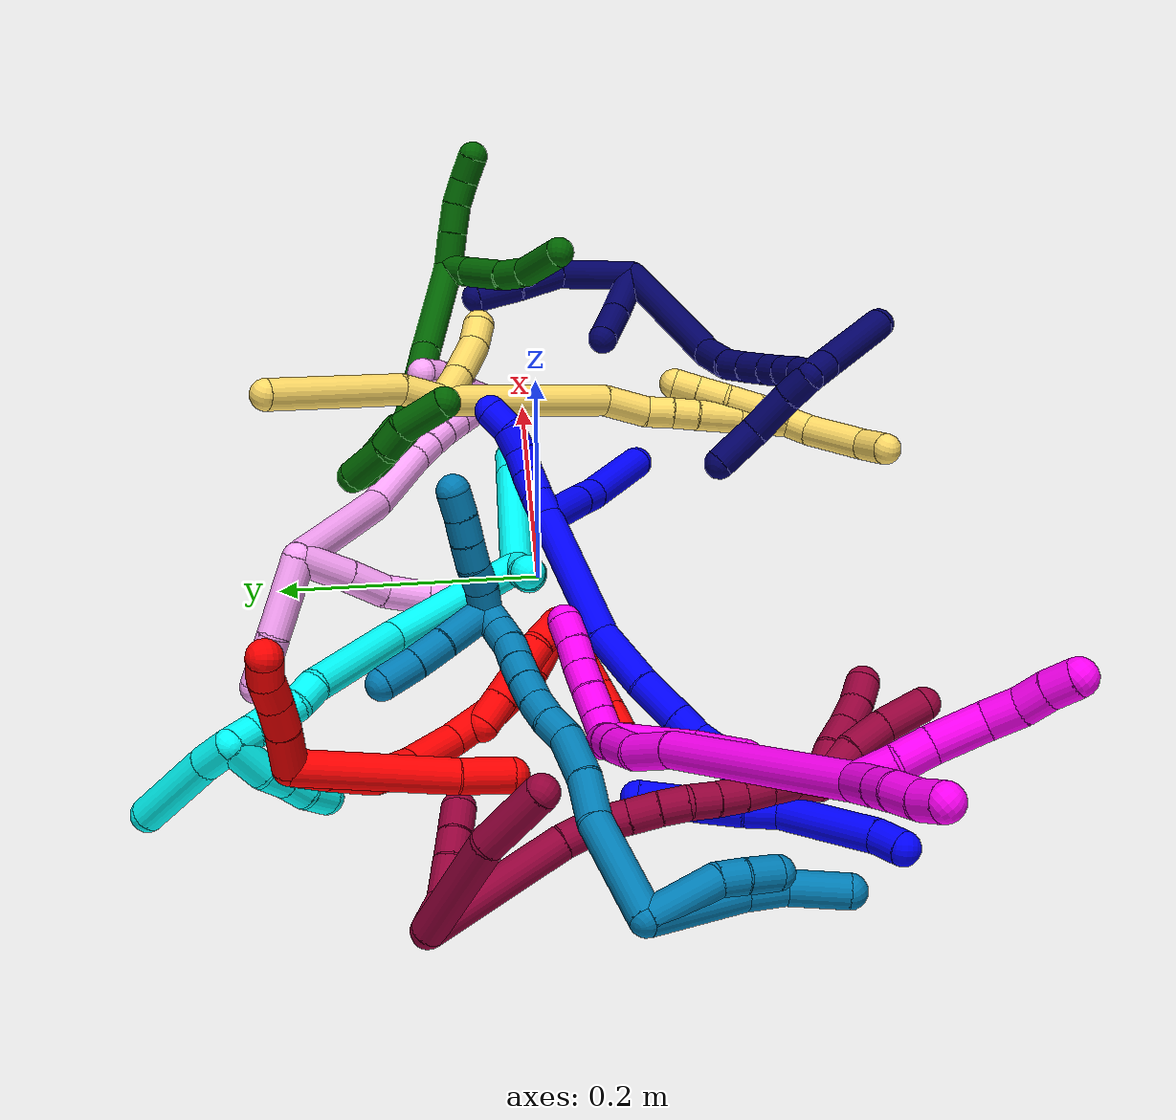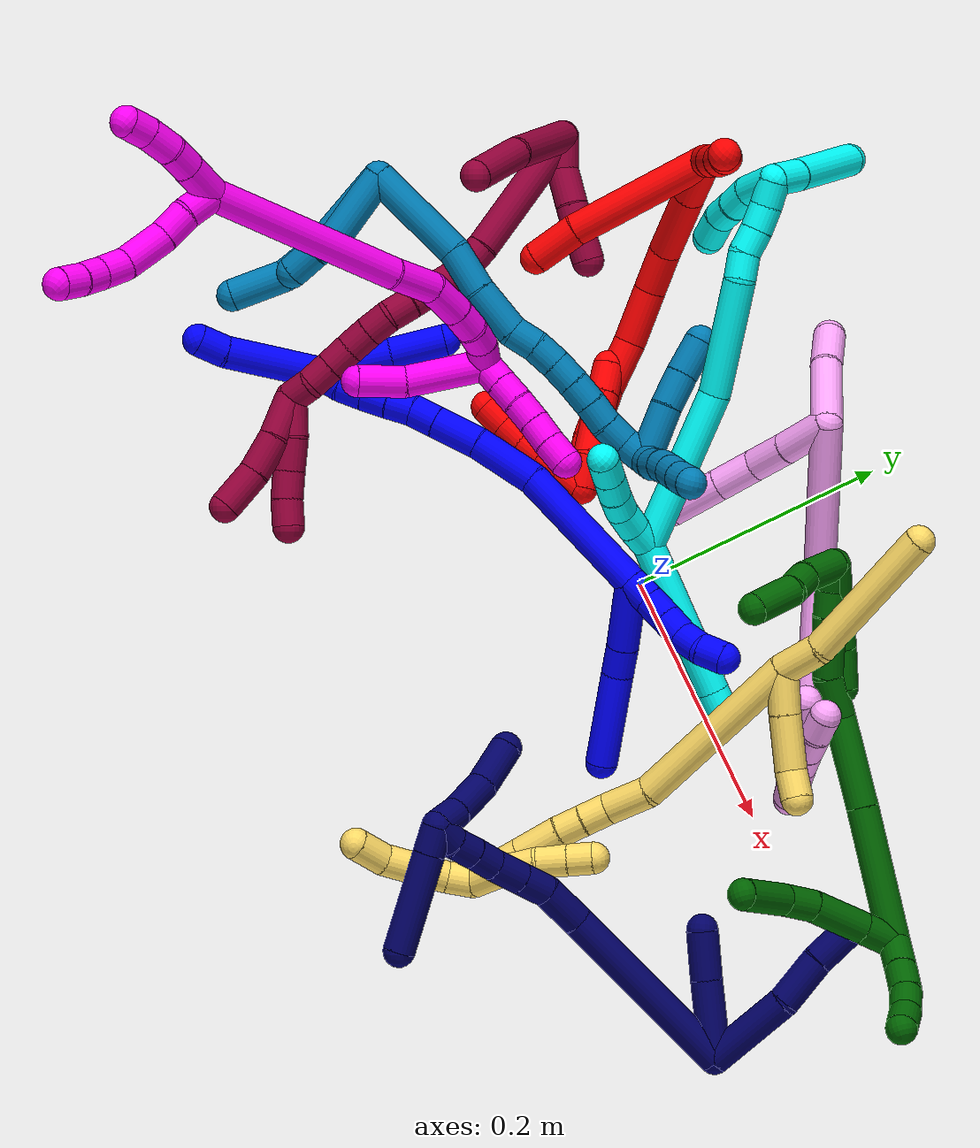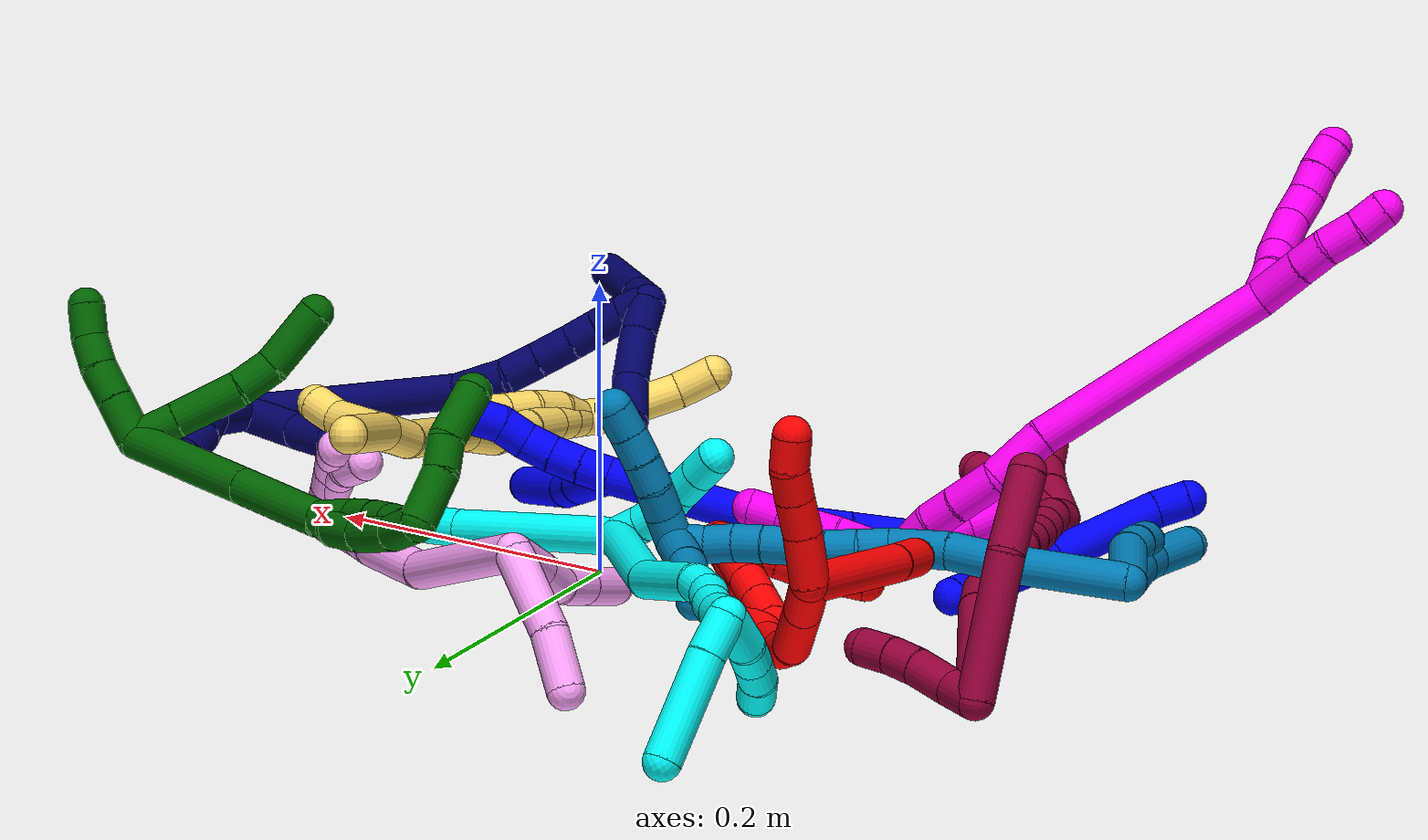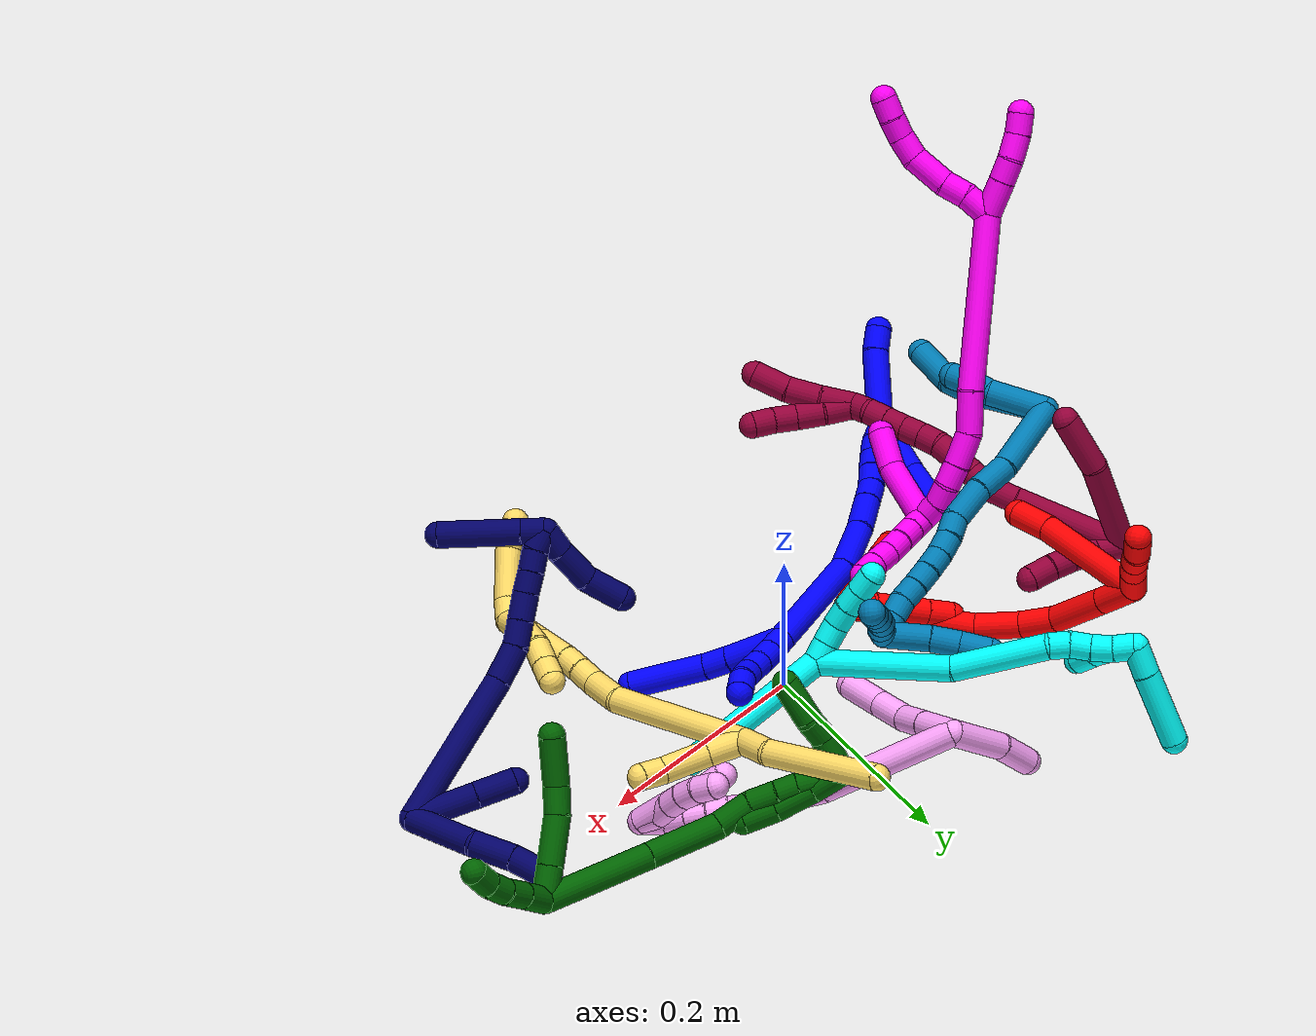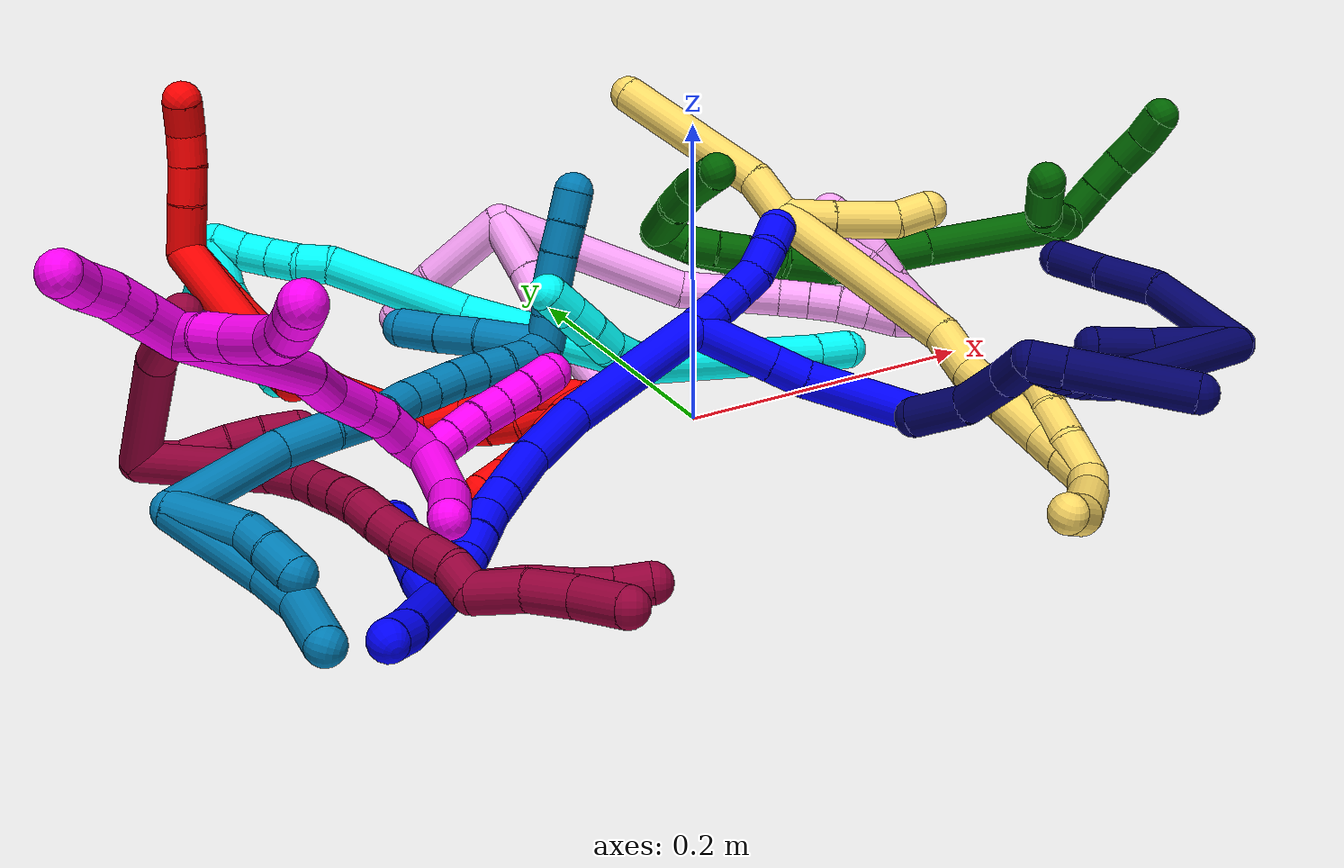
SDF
<sdf version="1.7">
 <world name="default">
  <plugin name="TubeGeneratorPlugin" filename="libtube_generator_plugin.so"/>
  <model name="photoneo_s_sensor">
   <static>1</static>
   <pose>0 0 2 1.57079 1.57079 3.14159</pose>
   <link name="link">
    <inertial><mass>0.1</mass></inertial>
    <sensor name="sensor" type="depth">
     <update_rate>30</update_rate>
     <camera>
      <horizontal_fov>1.22</horizontal_fov>
      <image><width>1920</width><height>1200</height><format>B8G8R8</format></image>
      <clip><near>0.1</near><far>4</far></clip>
      <depth_camera><output>points</output></depth_camera>
     </camera>
     <plugin name="camera_plugin" filename="libgazebo_ros_depth_camera.so">
      <baseline>0.2</baseline>
      <alwaysOn>1</alwaysOn>
      <updateRate>0.0</updateRate>
      <cameraName>camera_ir</cameraName>
      <imageTopicName>/camera/color/image_raw</imageTopicName>
      <cameraInfoTopicName>/camera/color/camera_info</cameraInfoTopicName>
      <depthImageTopicName>/camera/depth/image_raw</depthImageTopicName>
      <depthImageCameraInfoTopicName>/camera/depth/camera_info</depthImageCameraInfoTopicName>
      <pointCloudTopicName>/camera/depth/points</pointCloudTopicName>
      <frameName>fr_optical</frameName>
      <pointCloudCutoff>0.1</pointCloudCutoff>
      <pointCloudCutoffMax>2.0</pointCloudCutoffMax>
      <distortionK1>0</distortionK1>
      <distortionK2>0</distortionK2>
      <distortionK3>0</distortionK3>
      <distortionT1>0</distortionT1>
      <distortionT2>0</distortionT2>
      <CxPrime>0</CxPrime>
      <Cx>0</Cx>
      <Cy>0</Cy>
      <focalLength>0</focalLength>
      <hackBaseline>0</hackBaseline>
     </plugin>
    </sensor>
   </link>
  </model>
  <gravity>0 0 -9.8</gravity>
  <magnetic_field>6e-06 2.3e-05 -4.2e-05</magnetic_field>
  <atmosphere type="adiabatic"/>
  <physics name="default_physics" default="0" type="ode">
   <max_step_size>0.003</max_step_size>
   <real_time_factor>1</real_time_factor>
   <real_time_update_rate>1000</real_time_update_rate>
   <max_contacts>10000</max_contacts>
   <ode>
    <solver>
     <type>quick</type>
     <iters>100</iters>
     <sor>1.3</sor>
     <use_dynamic_moi_rescaling>0</use_dynamic_moi_rescaling>
    </solver>
    <constraints>
     <contact_max_correcting_vel>0</contact_max_correcting_vel>
     <contact_surface_layer>0.001</contact_surface_layer>
     <cfm>0</cfm>
     <erp>0.2</erp>
    </constraints>
   </ode>
  </physics>
  <scene><ambient>0.4 0.4 0.4 1</ambient><background>0.7 0.7 0.7 1</background><shadows>0</shadows></scene>
  <audio><device>default</device></audio>
  <spherical_coordinates>
   <surface_model>EARTH_WGS84</surface_model>
   <latitude_deg>0</latitude_deg>
   <longitude_deg>0</longitude_deg>
   <elevation>0</elevation>
   <heading_deg>0</heading_deg>
  </spherical_coordinates>
  <model name="bin">
   <static>1</static>
   <link name="bottom">
    <collision name="collision-bottom">
     <pose>0 0 -0.01 0 -0 0</pose>
     <geometry><box><size>0.8 0.6 0.02</size></box></geometry>
     <surface>
      <friction><ode><mu>100</mu><mu2>100</mu2></ode></friction>
      <contact><collide_bitmask>65535</collide_bitmask></contact>
     </surface>
    </collision>
   </link>
   <link name="west_wall">
    <collision name="collision-west_wall">
     <pose>-0.41 0 0.1 0 -0 0</pose>
     <geometry><box><size>0.02 0.6 0.2</size></box></geometry>
     <surface>
      <friction><ode><mu>100</mu><mu2>100</mu2></ode></friction>
      <contact><collide_bitmask>65535</collide_bitmask></contact>
     </surface>
    </collision>
   </link>
   <link name="east_wall">
    <collision name="collision-east_wall">
     <pose>0.41 0 0.1 0 -0 0</pose>
     <geometry><box><size>0.02 0.6 0.2</size></box></geometry>
     <surface>
      <friction><ode><mu>100</mu><mu2>100</mu2></ode></friction>
      <contact><collide_bitmask>65535</collide_bitmask></contact>
     </surface>
    </collision>
   </link>
   <link name="south_wall">
    <collision name="collision-south_wall">
     <pose>0 -0.31 0.1 0 -0 0</pose>
     <geometry><box><size>0.8 0.02 0.2</size></box></geometry>
     <surface>
      <friction><ode><mu>100</mu><mu2>100</mu2></ode></friction>
      <contact><collide_bitmask>65535</collide_bitmask></contact>
     </surface>
    </collision>
   </link>
   <link name="north_wall">
    <collision name="collision-north_wall">
     <pose>0 0.31 0.1 0 -0 0</pose>
     <geometry><box><size>0.8 0.02 0.2</size></box></geometry>
     <surface>
      <friction><ode><mu>100</mu><mu2>100</mu2></ode></friction>
      <contact><collide_bitmask>65535</collide_bitmask></contact>
     </surface>
    </collision>
   </link>
  </model>
  <model name="1">
   <static>0</static>
   <link name="1">
    <collision name="collision-cylinder-e_1_2_8">
     <pose>0.018485 -0.013799 0.01391 0.781372 0.756296 0.32436</pose>
     <geometry><cylinder><radius>0.0125</radius><length>0.053873</length></cylinder></geometry>
     <surface>
      <friction><ode><mu>1.16</mu><mu2>1.16</mu2><slip1>0</slip1><slip2>0</slip2></ode></friction>
      <contact><ode><kp>1e+06</kp><kd>1</kd><max_vel>0</max_vel><min_depth>0.001</min_depth></ode></contact>
     </surface>
    </collision>
    <visual name="visual-cylinder-e_1_2_8">
     <pose>0.018485 -0.013799 0.01391 0.781372 0.756296 0.32436</pose>
     <geometry><cylinder><radius>0.0125</radius><length>0.053873</length></cylinder></geometry>
     <material><ambient>0 0 1 1</ambient></material>
    </visual>
    <collision name="collision-cylinder-e_2_8_9">
     <pose>0.044879 -0.033379 0.034361 0.723861 0.736111 0.289955</pose>
     <geometry><cylinder><radius>0.0125</radius><length>0.023559</length></cylinder></geometry>
     <surface>
      <friction><ode><mu>1.16</mu><mu2>1.16</mu2><slip1>0</slip1><slip2>0</slip2></ode></friction>
      <contact><ode><kp>1e+06</kp><kd>1</kd><max_vel>0</max_vel><min_depth>0.001</min_depth></ode></contact>
     </surface>
    </collision>
    <visual name="visual-cylinder-e_2_8_9">
     <pose>0.044879 -0.033379 0.034361 0.723861 0.736111 0.289955</pose>
     <geometry><cylinder><radius>0.0125</radius><length>0.023559</length></cylinder></geometry>
     <material><ambient>0 0 1 1</ambient></material>
    </visual>
    <collision name="collision-cylinder-e_3_9_6">
     <pose>0.079772 -0.052645 0.061064 0.589487 0.838581 0.268996</pose>
     <geometry><cylinder><radius>0.0125</radius><length>0.072567</length></cylinder></geometry>
     <surface>
      <friction><ode><mu>1.16</mu><mu2>1.16</mu2><slip1>0</slip1><slip2>0</slip2></ode></friction>
      <contact><ode><kp>1e+06</kp><kd>1</kd><max_vel>0</max_vel><min_depth>0.001</min_depth></ode></contact>
     </surface>
    </collision>
    <visual name="visual-cylinder-e_3_9_6">
     <pose>0.079772 -0.052645 0.061064 0.589487 0.838581 0.268996</pose>
     <geometry><cylinder><radius>0.0125</radius><length>0.072567</length></cylinder></geometry>
     <material><ambient>0 0 1 1</ambient></material>
    </visual>
    <collision name="collision-cylinder-e_1_2_10">
     <pose>0.009206 0.000197 -0.0039 -3.09104 1.16958 -3.06525</pose>
     <geometry><cylinder><radius>0.0125</radius><length>0.02</length></cylinder></geometry>
     <surface>
      <friction><ode><mu>1.16</mu><mu2>1.16</mu2><slip1>0</slip1><slip2>0</slip2></ode></friction>
      <contact><ode><kp>1e+06</kp><kd>1</kd><max_vel>0</max_vel><min_depth>0.001</min_depth></ode></contact>
     </surface>
    </collision>
    <visual name="visual-cylinder-e_1_2_10">
     <pose>0.009206 0.000197 -0.0039 -3.09104 1.16958 -3.06525</pose>
     <geometry><cylinder><radius>0.0125</radius><length>0.02</length></cylinder></geometry>
     <material><ambient>0 0 1 1</ambient></material>
    </visual>
    <collision name="collision-cylinder-e_2_10_11">
     <pose>0.027685 0.00101 -0.011491 -2.97646 1.18733 -2.89757</pose>
     <geometry><cylinder><radius>0.0125</radius><length>0.02</length></cylinder></geometry>
     <surface>
      <friction><ode><mu>1.16</mu><mu2>1.16</mu2><slip1>0</slip1><slip2>0</slip2></ode></friction>
      <contact><ode><kp>1e+06</kp><kd>1</kd><max_vel>0</max_vel><min_depth>0.001</min_depth></ode></contact>
     </surface>
    </collision>
    <visual name="visual-cylinder-e_2_10_11">
     <pose>0.027685 0.00101 -0.011491 -2.97646 1.18733 -2.89757</pose>
     <geometry><cylinder><radius>0.0125</radius><length>0.02</length></cylinder></geometry>
     <material><ambient>0 0 1 1</ambient></material>
    </visual>
    <collision name="collision-cylinder-e_3_11_12">
     <pose>0.046242 0.003006 -0.018635 -2.7611 1.18968 -2.587</pose>
     <geometry><cylinder><radius>0.0125</radius><length>0.02</length></cylinder></geometry>
     <surface>
      <friction><ode><mu>1.16</mu><mu2>1.16</mu2><slip1>0</slip1><slip2>0</slip2></ode></friction>
      <contact><ode><kp>1e+06</kp><kd>1</kd><max_vel>0</max_vel><min_depth>0.001</min_depth></ode></contact>
     </surface>
    </collision>
    <visual name="visual-cylinder-e_3_11_12">
     <pose>0.046242 0.003006 -0.018635 -2.7611 1.18968 -2.587</pose>
     <geometry><cylinder><radius>0.0125</radius><length>0.02</length></cylinder></geometry>
     <material><ambient>0 0 1 1</ambient></material>
    </visual>
    <collision name="collision-cylinder-e_4_12_13">
     <pose>0.063337 0.00793 -0.027228 -2.53812 0.896667 -1.99297</pose>
     <geometry><cylinder><radius>0.0125</radius><length>0.02</length></cylinder></geometry>
     <surface>
      <friction><ode><mu>1.16</mu><mu2>1.16</mu2><slip1>0</slip1><slip2>0</slip2></ode></friction>
      <contact><ode><kp>1e+06</kp><kd>1</kd><max_vel>0</max_vel><min_depth>0.001</min_depth></ode></contact>
     </surface>
    </collision>
    <visual name="visual-cylinder-e_4_12_13">
     <pose>0.063337 0.00793 -0.027228 -2.53812 0.896667 -1.99297</pose>
     <geometry><cylinder><radius>0.0125</radius><length>0.02</length></cylinder></geometry>
     <material><ambient>0 0 1 1</ambient></material>
    </visual>
    <collision name="collision-cylinder-e_5_13_5">
     <pose>0.078208 0.01241 -0.039389 -3.00883 0.783671 -2.82256</pose>
     <geometry><cylinder><radius>0.0125</radius><length>0.02</length></cylinder></geometry>
     <surface>
      <friction><ode><mu>1.16</mu><mu2>1.16</mu2><slip1>0</slip1><slip2>0</slip2></ode></friction>
      <contact><ode><kp>1e+06</kp><kd>1</kd><max_vel>0</max_vel><min_depth>0.001</min_depth></ode></contact>
     </surface>
    </collision>
    <visual name="visual-cylinder-e_5_13_5">
     <pose>0.078208 0.01241 -0.039389 -3.00883 0.783671 -2.82256</pose>
     <geometry><cylinder><radius>0.0125</radius><length>0.02</length></cylinder></geometry>
     <material><ambient>0 0 1 1</ambient></material>
    </visual>
    <collision name="collision-cylinder-e_1_2_14">
     <pose>-0.051818 0.003019 0.020473 -0.146401 -1.19083 0.099272</pose>
     <geometry><cylinder><radius>0.0125</radius><length>0.111596</length></cylinder></geometry>
     <surface>
      <friction><ode><mu>1.16</mu><mu2>1.16</mu2><slip1>0</slip1><slip2>0</slip2></ode></friction>
      <contact><ode><kp>1e+06</kp><kd>1</kd><max_vel>0</max_vel><min_depth>0.001</min_depth></ode></contact>
     </surface>
    </collision>
    <visual name="visual-cylinder-e_1_2_14">
     <pose>-0.051818 0.003019 0.020473 -0.146401 -1.19083 0.099272</pose>
     <geometry><cylinder><radius>0.0125</radius><length>0.111596</length></cylinder></geometry>
     <material><ambient>0 0 1 1</ambient></material>
    </visual>
    <collision name="collision-cylinder-e_2_14_15">
     <pose>-0.124346 0.009299 0.05522 -0.224621 -0.955402 0.116644</pose>
     <geometry><cylinder><radius>0.0125</radius><length>0.050725</length></cylinder></geometry>
     <surface>
      <friction><ode><mu>1.16</mu><mu2>1.16</mu2><slip1>0</slip1><slip2>0</slip2></ode></friction>
      <contact><ode><kp>1e+06</kp><kd>1</kd><max_vel>0</max_vel><min_depth>0.001</min_depth></ode></contact>
     </surface>
    </collision>
    <visual name="visual-cylinder-e_2_14_15">
     <pose>-0.124346 0.009299 0.05522 -0.224621 -0.955402 0.116644</pose>
     <geometry><cylinder><radius>0.0125</radius><length>0.050725</length></cylinder></geometry>
     <material><ambient>0 0 1 1</ambient></material>
    </visual>
    <collision name="collision-cylinder-e_3_15_16">
     <pose>-0.158835 0.014181 0.081471 -0.134545 -0.85074 0.061026</pose>
     <geometry><cylinder><radius>0.0125</radius><length>0.036657</length></cylinder></geometry>
     <surface>
      <friction><ode><mu>1.16</mu><mu2>1.16</mu2><slip1>0</slip1><slip2>0</slip2></ode></friction>
      <contact><ode><kp>1e+06</kp><kd>1</kd><max_vel>0</max_vel><min_depth>0.001</min_depth></ode></contact>
     </surface>
    </collision>
    <visual name="visual-cylinder-e_3_15_16">
     <pose>-0.158835 0.014181 0.081471 -0.134545 -0.85074 0.061026</pose>
     <geometry><cylinder><radius>0.0125</radius><length>0.036657</length></cylinder></geometry>
     <material><ambient>0 0 1 1</ambient></material>
    </visual>
    <collision name="collision-cylinder-e_4_16_17">
     <pose>-0.18044 0.016496 0.100208 -0.102167 -0.855771 0.046627</pose>
     <geometry><cylinder><radius>0.0125</radius><length>0.020729</length></cylinder></geometry>
     <surface>
      <friction><ode><mu>1.16</mu><mu2>1.16</mu2><slip1>0</slip1><slip2>0</slip2></ode></friction>
      <contact><ode><kp>1e+06</kp><kd>1</kd><max_vel>0</max_vel><min_depth>0.001</min_depth></ode></contact>
     </surface>
    </collision>
    <visual name="visual-cylinder-e_4_16_17">
     <pose>-0.18044 0.016496 0.100208 -0.102167 -0.855771 0.046627</pose>
     <geometry><cylinder><radius>0.0125</radius><length>0.020729</length></cylinder></geometry>
     <material><ambient>0 0 1 1</ambient></material>
    </visual>
    <collision name="collision-cylinder-e_5_17_18">
     <pose>-0.194641 0.018095 0.114738 -0.116131 -0.683827 0.041371</pose>
     <geometry><cylinder><radius>0.0125</radius><length>0.020183</length></cylinder></geometry>
     <surface>
      <friction><ode><mu>1.16</mu><mu2>1.16</mu2><slip1>0</slip1><slip2>0</slip2></ode></friction>
      <contact><ode><kp>1e+06</kp><kd>1</kd><max_vel>0</max_vel><min_depth>0.001</min_depth></ode></contact>
     </surface>
    </collision>
    <visual name="visual-cylinder-e_5_17_18">
     <pose>-0.194641 0.018095 0.114738 -0.116131 -0.683827 0.041371</pose>
     <geometry><cylinder><radius>0.0125</radius><length>0.020183</length></cylinder></geometry>
     <material><ambient>0 0 1 1</ambient></material>
    </visual>
    <collision name="collision-cylinder-e_6_18_19">
     <pose>-0.207637 0.019317 0.129998 -0.042074 -0.723394 0.01592</pose>
     <geometry><cylinder><radius>0.0125</radius><length>0.020004</length></cylinder></geometry>
     <surface>
      <friction><ode><mu>1.16</mu><mu2>1.16</mu2><slip1>0</slip1><slip2>0</slip2></ode></friction>
      <contact><ode><kp>1e+06</kp><kd>1</kd><max_vel>0</max_vel><min_depth>0.001</min_depth></ode></contact>
     </surface>
    </collision>
    <visual name="visual-cylinder-e_6_18_19">
     <pose>-0.207637 0.019317 0.129998 -0.042074 -0.723394 0.01592</pose>
     <geometry><cylinder><radius>0.0125</radius><length>0.020004</length></cylinder></geometry>
     <material><ambient>0 0 1 1</ambient></material>
    </visual>
    <collision name="collision-cylinder-e_7_19_20">
     <pose>-0.221105 0.020081 0.144764 -0.061649 -0.754105 0.02442</pose>
     <geometry><cylinder><radius>0.0125</radius><length>0.020002</length></cylinder></geometry>
     <surface>
      <friction><ode><mu>1.16</mu><mu2>1.16</mu2><slip1>0</slip1><slip2>0</slip2></ode></friction>
      <contact><ode><kp>1e+06</kp><kd>1</kd><max_vel>0</max_vel><min_depth>0.001</min_depth></ode></contact>
     </surface>
    </collision>
    <visual name="visual-cylinder-e_7_19_20">
     <pose>-0.221105 0.020081 0.144764 -0.061649 -0.754105 0.02442</pose>
     <geometry><cylinder><radius>0.0125</radius><length>0.020002</length></cylinder></geometry>
     <material><ambient>0 0 1 1</ambient></material>
    </visual>
    <collision name="collision-cylinder-e_8_20_1">
     <pose>-0.23607 0.020949 0.157953 -0.070723 -0.940082 0.03594</pose>
     <geometry><cylinder><radius>0.0125</radius><length>0.020104</length></cylinder></geometry>
     <surface>
      <friction><ode><mu>1.16</mu><mu2>1.16</mu2><slip1>0</slip1><slip2>0</slip2></ode></friction>
      <contact><ode><kp>1e+06</kp><kd>1</kd><max_vel>0</max_vel><min_depth>0.001</min_depth></ode></contact>
     </surface>
    </collision>
    <visual name="visual-cylinder-e_8_20_1">
     <pose>-0.23607 0.020949 0.157953 -0.070723 -0.940082 0.03594</pose>
     <geometry><cylinder><radius>0.0125</radius><length>0.020104</length></cylinder></geometry>
     <material><ambient>0 0 1 1</ambient></material>
    </visual>
    <collision name="collision-cylinder-e_1_1_21">
     <pose>-0.243604 0.019496 0.1511 2.99598 0.045255 0.601758</pose>
     <geometry><cylinder><radius>0.0125</radius><length>0.025832</length></cylinder></geometry>
     <surface>
      <friction><ode><mu>1.16</mu><mu2>1.16</mu2><slip1>0</slip1><slip2>0</slip2></ode></friction>
      <contact><ode><kp>1e+06</kp><kd>1</kd><max_vel>0</max_vel><min_depth>0.001</min_depth></ode></contact>
     </surface>
    </collision>
    <visual name="visual-cylinder-e_1_1_21">
     <pose>-0.243604 0.019496 0.1511 2.99598 0.045255 0.601758</pose>
     <geometry><cylinder><radius>0.0125</radius><length>0.025832</length></cylinder></geometry>
     <material><ambient>0 0 1 1</ambient></material>
    </visual>
    <collision name="collision-cylinder-e_2_21_22">
     <pose>-0.240709 0.014442 0.123352 2.93229 0.1497 1.24008</pose>
     <geometry><cylinder><radius>0.0125</radius><length>0.030977</length></cylinder></geometry>
     <surface>
      <friction><ode><mu>1.16</mu><mu2>1.16</mu2><slip1>0</slip1><slip2>0</slip2></ode></friction>
      <contact><ode><kp>1e+06</kp><kd>1</kd><max_vel>0</max_vel><min_depth>0.001</min_depth></ode></contact>
     </surface>
    </collision>
    <visual name="visual-cylinder-e_2_21_22">
     <pose>-0.240709 0.014442 0.123352 2.93229 0.1497 1.24008</pose>
     <geometry><cylinder><radius>0.0125</radius><length>0.030977</length></cylinder></geometry>
     <material><ambient>0 0 1 1</ambient></material>
    </visual>
    <collision name="collision-cylinder-e_3_22_4">
     <pose>-0.235695 0.008159 0.087171 2.99634 0.125566 1.42521</pose>
     <geometry><cylinder><radius>0.0125</radius><length>0.043191</length></cylinder></geometry>
     <surface>
      <friction><ode><mu>1.16</mu><mu2>1.16</mu2><slip1>0</slip1><slip2>0</slip2></ode></friction>
      <contact><ode><kp>1e+06</kp><kd>1</kd><max_vel>0</max_vel><min_depth>0.001</min_depth></ode></contact>
     </surface>
    </collision>
    <visual name="visual-cylinder-e_3_22_4">
     <pose>-0.235695 0.008159 0.087171 2.99634 0.125566 1.42521</pose>
     <geometry><cylinder><radius>0.0125</radius><length>0.043191</length></cylinder></geometry>
     <material><ambient>0 0 1 1</ambient></material>
    </visual>
    <collision name="collision-cylinder-e_1_1_23">
     <pose>-0.26126 0.041556 0.192076 -0.621126 -0.457339 0.149118</pose>
     <geometry><cylinder><radius>0.0125</radius><length>0.077325</length></cylinder></geometry>
     <surface>
      <friction><ode><mu>1.16</mu><mu2>1.16</mu2><slip1>0</slip1><slip2>0</slip2></ode></friction>
      <contact><ode><kp>1e+06</kp><kd>1</kd><max_vel>0</max_vel><min_depth>0.001</min_depth></ode></contact>
     </surface>
    </collision>
    <visual name="visual-cylinder-e_1_1_23">
     <pose>-0.26126 0.041556 0.192076 -0.621126 -0.457339 0.149118</pose>
     <geometry><cylinder><radius>0.0125</radius><length>0.077325</length></cylinder></geometry>
     <material><ambient>0 0 1 1</ambient></material>
    </visual>
    <collision name="collision-cylinder-e_2_23_3">
     <pose>-0.285119 0.067502 0.227308 -0.686869 -0.641793 0.236615</pose>
     <geometry><cylinder><radius>0.0125</radius><length>0.022675</length></cylinder></geometry>
     <surface>
      <friction><ode><mu>1.16</mu><mu2>1.16</mu2><slip1>0</slip1><slip2>0</slip2></ode></friction>
      <contact><ode><kp>1e+06</kp><kd>1</kd><max_vel>0</max_vel><min_depth>0.001</min_depth></ode></contact>
     </surface>
    </collision>
    <visual name="visual-cylinder-e_2_23_3">
     <pose>-0.285119 0.067502 0.227308 -0.686869 -0.641793 0.236615</pose>
     <geometry><cylinder><radius>0.0125</radius><length>0.022675</length></cylinder></geometry>
     <material><ambient>0 0 1 1</ambient></material>
    </visual>
    <collision name="collision-sphere-3">
     <pose>-0.291906 0.073261 0.23433 0 -0 0</pose>
     <geometry><sphere><radius>0.0125</radius></sphere></geometry>
     <surface>
      <friction><ode><mu>1.16</mu><mu2>1.16</mu2><slip1>0</slip1><slip2>0</slip2></ode></friction>
      <contact><ode><kp>1e+06</kp><kd>1</kd><max_vel>0</max_vel><min_depth>0.001</min_depth></ode></contact>
     </surface>
    </collision>
    <visual name="visual-sphere-3">
     <pose>-0.291906 0.073261 0.23433 0 -0 0</pose>
     <geometry><sphere><radius>0.0125</radius></sphere></geometry>
     <material><ambient>0 0 1 1</ambient></material>
    </visual>
    <collision name="collision-sphere-23">
     <pose>-0.278332 0.061743 0.220286 0 -0 0</pose>
     <geometry><sphere><radius>0.0125</radius></sphere></geometry>
     <surface>
      <friction><ode><mu>1.16</mu><mu2>1.16</mu2><slip1>0</slip1><slip2>0</slip2></ode></friction>
      <contact><ode><kp>1e+06</kp><kd>1</kd><max_vel>0</max_vel><min_depth>0.001</min_depth></ode></contact>
     </surface>
    </collision>
    <visual name="visual-sphere-23">
     <pose>-0.278332 0.061743 0.220286 0 -0 0</pose>
     <geometry><sphere><radius>0.0125</radius></sphere></geometry>
     <material><ambient>0 0 1 1</ambient></material>
    </visual>
    <collision name="collision-sphere-4">
     <pose>-0.23299 0.005057 0.065972 0 -0 0</pose>
     <geometry><sphere><radius>0.0125</radius></sphere></geometry>
     <surface>
      <friction><ode><mu>1.16</mu><mu2>1.16</mu2><slip1>0</slip1><slip2>0</slip2></ode></friction>
      <contact><ode><kp>1e+06</kp><kd>1</kd><max_vel>0</max_vel><min_depth>0.001</min_depth></ode></contact>
     </surface>
    </collision>
    <visual name="visual-sphere-4">
     <pose>-0.23299 0.005057 0.065972 0 -0 0</pose>
     <geometry><sphere><radius>0.0125</radius></sphere></geometry>
     <material><ambient>0 0 1 1</ambient></material>
    </visual>
    <collision name="collision-sphere-22">
     <pose>-0.238399 0.01126 0.108371 0 -0 0</pose>
     <geometry><sphere><radius>0.0125</radius></sphere></geometry>
     <surface>
      <friction><ode><mu>1.16</mu><mu2>1.16</mu2><slip1>0</slip1><slip2>0</slip2></ode></friction>
      <contact><ode><kp>1e+06</kp><kd>1</kd><max_vel>0</max_vel><min_depth>0.001</min_depth></ode></contact>
     </surface>
    </collision>
    <visual name="visual-sphere-22">
     <pose>-0.238399 0.01126 0.108371 0 -0 0</pose>
     <geometry><sphere><radius>0.0125</radius></sphere></geometry>
     <material><ambient>0 0 1 1</ambient></material>
    </visual>
    <collision name="collision-sphere-21">
     <pose>-0.243019 0.017624 0.138333 0 -0 0</pose>
     <geometry><sphere><radius>0.0125</radius></sphere></geometry>
     <surface>
      <friction><ode><mu>1.16</mu><mu2>1.16</mu2><slip1>0</slip1><slip2>0</slip2></ode></friction>
      <contact><ode><kp>1e+06</kp><kd>1</kd><max_vel>0</max_vel><min_depth>0.001</min_depth></ode></contact>
     </surface>
    </collision>
    <visual name="visual-sphere-21">
     <pose>-0.243019 0.017624 0.138333 0 -0 0</pose>
     <geometry><sphere><radius>0.0125</radius></sphere></geometry>
     <material><ambient>0 0 1 1</ambient></material>
    </visual>
    <collision name="collision-sphere-1">
     <pose>-0.244188 0.021368 0.163866 0 -0 0</pose>
     <geometry><sphere><radius>0.0125</radius></sphere></geometry>
     <surface>
      <friction><ode><mu>1.16</mu><mu2>1.16</mu2><slip1>0</slip1><slip2>0</slip2></ode></friction>
      <contact><ode><kp>1e+06</kp><kd>1</kd><max_vel>0</max_vel><min_depth>0.001</min_depth></ode></contact>
     </surface>
    </collision>
    <visual name="visual-sphere-1">
     <pose>-0.244188 0.021368 0.163866 0 -0 0</pose>
     <geometry><sphere><radius>0.0125</radius></sphere></geometry>
     <material><ambient>0 0 1 1</ambient></material>
    </visual>
    <collision name="collision-sphere-11">
     <pose>0.036959 0.001625 -0.015182 0 -0 0</pose>
     <geometry><sphere><radius>0.0125</radius></sphere></geometry>
     <surface>
      <friction><ode><mu>1.16</mu><mu2>1.16</mu2><slip1>0</slip1><slip2>0</slip2></ode></friction>
      <contact><ode><kp>1e+06</kp><kd>1</kd><max_vel>0</max_vel><min_depth>0.001</min_depth></ode></contact>
     </surface>
    </collision>
    <visual name="visual-sphere-11">
     <pose>0.036959 0.001625 -0.015182 0 -0 0</pose>
     <geometry><sphere><radius>0.0125</radius></sphere></geometry>
     <material><ambient>0 0 1 1</ambient></material>
    </visual>
    <collision name="collision-sphere-10">
     <pose>0.018412 0.000395 -0.007801 0 -0 0</pose>
     <geometry><sphere><radius>0.0125</radius></sphere></geometry>
     <surface>
      <friction><ode><mu>1.16</mu><mu2>1.16</mu2><slip1>0</slip1><slip2>0</slip2></ode></friction>
      <contact><ode><kp>1e+06</kp><kd>1</kd><max_vel>0</max_vel><min_depth>0.001</min_depth></ode></contact>
     </surface>
    </collision>
    <visual name="visual-sphere-10">
     <pose>0.018412 0.000395 -0.007801 0 -0 0</pose>
     <geometry><sphere><radius>0.0125</radius></sphere></geometry>
     <material><ambient>0 0 1 1</ambient></material>
    </visual>
    <collision name="collision-sphere-6">
     <pose>0.106756 -0.06613 0.081227 0 -0 0</pose>
     <geometry><sphere><radius>0.0125</radius></sphere></geometry>
     <surface>
      <friction><ode><mu>1.16</mu><mu2>1.16</mu2><slip1>0</slip1><slip2>0</slip2></ode></friction>
      <contact><ode><kp>1e+06</kp><kd>1</kd><max_vel>0</max_vel><min_depth>0.001</min_depth></ode></contact>
     </surface>
    </collision>
    <visual name="visual-sphere-6">
     <pose>0.106756 -0.06613 0.081227 0 -0 0</pose>
     <geometry><sphere><radius>0.0125</radius></sphere></geometry>
     <material><ambient>0 0 1 1</ambient></material>
    </visual>
    <collision name="collision-sphere-9">
     <pose>0.052788 -0.03916 0.040902 0 -0 0</pose>
     <geometry><sphere><radius>0.0125</radius></sphere></geometry>
     <surface>
      <friction><ode><mu>1.16</mu><mu2>1.16</mu2><slip1>0</slip1><slip2>0</slip2></ode></friction>
      <contact><ode><kp>1e+06</kp><kd>1</kd><max_vel>0</max_vel><min_depth>0.001</min_depth></ode></contact>
     </surface>
    </collision>
    <visual name="visual-sphere-9">
     <pose>0.052788 -0.03916 0.040902 0 -0 0</pose>
     <geometry><sphere><radius>0.0125</radius></sphere></geometry>
     <material><ambient>0 0 1 1</ambient></material>
    </visual>
    <collision name="collision-sphere-2">
     <geometry><sphere><radius>0.0125</radius></sphere></geometry>
     <surface>
      <friction><ode><mu>1.16</mu><mu2>1.16</mu2><slip1>0</slip1><slip2>0</slip2></ode></friction>
      <contact><ode><kp>1e+06</kp><kd>1</kd><max_vel>0</max_vel><min_depth>0.001</min_depth></ode></contact>
     </surface>
    </collision>
    <visual name="visual-sphere-2">
     <geometry><sphere><radius>0.0125</radius></sphere></geometry>
     <material><ambient>0 0 1 1</ambient></material>
    </visual>
    <collision name="collision-sphere-19">
     <pose>-0.214258 0.019632 0.137488 0 -0 0</pose>
     <geometry><sphere><radius>0.0125</radius></sphere></geometry>
     <surface>
      <friction><ode><mu>1.16</mu><mu2>1.16</mu2><slip1>0</slip1><slip2>0</slip2></ode></friction>
      <contact><ode><kp>1e+06</kp><kd>1</kd><max_vel>0</max_vel><min_depth>0.001</min_depth></ode></contact>
     </surface>
    </collision>
    <visual name="visual-sphere-19">
     <pose>-0.214258 0.019632 0.137488 0 -0 0</pose>
     <geometry><sphere><radius>0.0125</radius></sphere></geometry>
     <material><ambient>0 0 1 1</ambient></material>
    </visual>
    <collision name="collision-sphere-8">
     <pose>0.03697 -0.027597 0.02782 0 -0 0</pose>
     <geometry><sphere><radius>0.0125</radius></sphere></geometry>
     <surface>
      <friction><ode><mu>1.16</mu><mu2>1.16</mu2><slip1>0</slip1><slip2>0</slip2></ode></friction>
      <contact><ode><kp>1e+06</kp><kd>1</kd><max_vel>0</max_vel><min_depth>0.001</min_depth></ode></contact>
     </surface>
    </collision>
    <visual name="visual-sphere-8">
     <pose>0.03697 -0.027597 0.02782 0 -0 0</pose>
     <geometry><sphere><radius>0.0125</radius></sphere></geometry>
     <material><ambient>0 0 1 1</ambient></material>
    </visual>
    <collision name="collision-sphere-12">
     <pose>0.055524 0.004387 -0.022089 0 -0 0</pose>
     <geometry><sphere><radius>0.0125</radius></sphere></geometry>
     <surface>
      <friction><ode><mu>1.16</mu><mu2>1.16</mu2><slip1>0</slip1><slip2>0</slip2></ode></friction>
      <contact><ode><kp>1e+06</kp><kd>1</kd><max_vel>0</max_vel><min_depth>0.001</min_depth></ode></contact>
     </surface>
    </collision>
    <visual name="visual-sphere-12">
     <pose>0.055524 0.004387 -0.022089 0 -0 0</pose>
     <geometry><sphere><radius>0.0125</radius></sphere></geometry>
     <material><ambient>0 0 1 1</ambient></material>
    </visual>
    <collision name="collision-sphere-13">
     <pose>0.071149 0.011472 -0.032368 0 -0 0</pose>
     <geometry><sphere><radius>0.0125</radius></sphere></geometry>
     <surface>
      <friction><ode><mu>1.16</mu><mu2>1.16</mu2><slip1>0</slip1><slip2>0</slip2></ode></friction>
      <contact><ode><kp>1e+06</kp><kd>1</kd><max_vel>0</max_vel><min_depth>0.001</min_depth></ode></contact>
     </surface>
    </collision>
    <visual name="visual-sphere-13">
     <pose>0.071149 0.011472 -0.032368 0 -0 0</pose>
     <geometry><sphere><radius>0.0125</radius></sphere></geometry>
     <material><ambient>0 0 1 1</ambient></material>
    </visual>
    <collision name="collision-sphere-5">
     <pose>0.085267 0.013348 -0.04641 0 -0 0</pose>
     <geometry><sphere><radius>0.0125</radius></sphere></geometry>
     <surface>
      <friction><ode><mu>1.16</mu><mu2>1.16</mu2><slip1>0</slip1><slip2>0</slip2></ode></friction>
      <contact><ode><kp>1e+06</kp><kd>1</kd><max_vel>0</max_vel><min_depth>0.001</min_depth></ode></contact>
     </surface>
    </collision>
    <visual name="visual-sphere-5">
     <pose>0.085267 0.013348 -0.04641 0 -0 0</pose>
     <geometry><sphere><radius>0.0125</radius></sphere></geometry>
     <material><ambient>0 0 1 1</ambient></material>
    </visual>
    <collision name="collision-sphere-14">
     <pose>-0.103637 0.006038 0.040947 0 -0 0</pose>
     <geometry><sphere><radius>0.0125</radius></sphere></geometry>
     <surface>
      <friction><ode><mu>1.16</mu><mu2>1.16</mu2><slip1>0</slip1><slip2>0</slip2></ode></friction>
      <contact><ode><kp>1e+06</kp><kd>1</kd><max_vel>0</max_vel><min_depth>0.001</min_depth></ode></contact>
     </surface>
    </collision>
    <visual name="visual-sphere-14">
     <pose>-0.103637 0.006038 0.040947 0 -0 0</pose>
     <geometry><sphere><radius>0.0125</radius></sphere></geometry>
     <material><ambient>0 0 1 1</ambient></material>
    </visual>
    <collision name="collision-sphere-15">
     <pose>-0.145056 0.01256 0.069494 0 -0 0</pose>
     <geometry><sphere><radius>0.0125</radius></sphere></geometry>
     <surface>
      <friction><ode><mu>1.16</mu><mu2>1.16</mu2><slip1>0</slip1><slip2>0</slip2></ode></friction>
      <contact><ode><kp>1e+06</kp><kd>1</kd><max_vel>0</max_vel><min_depth>0.001</min_depth></ode></contact>
     </surface>
    </collision>
    <visual name="visual-sphere-15">
     <pose>-0.145056 0.01256 0.069494 0 -0 0</pose>
     <geometry><sphere><radius>0.0125</radius></sphere></geometry>
     <material><ambient>0 0 1 1</ambient></material>
    </visual>
    <collision name="collision-sphere-16">
     <pose>-0.172614 0.015803 0.093448 0 -0 0</pose>
     <geometry><sphere><radius>0.0125</radius></sphere></geometry>
     <surface>
      <friction><ode><mu>1.16</mu><mu2>1.16</mu2><slip1>0</slip1><slip2>0</slip2></ode></friction>
      <contact><ode><kp>1e+06</kp><kd>1</kd><max_vel>0</max_vel><min_depth>0.001</min_depth></ode></contact>
     </surface>
    </collision>
    <visual name="visual-sphere-16">
     <pose>-0.172614 0.015803 0.093448 0 -0 0</pose>
     <geometry><sphere><radius>0.0125</radius></sphere></geometry>
     <material><ambient>0 0 1 1</ambient></material>
    </visual>
    <collision name="collision-sphere-17">
     <pose>-0.188266 0.017189 0.106968 0 -0 0</pose>
     <geometry><sphere><radius>0.0125</radius></sphere></geometry>
     <surface>
      <friction><ode><mu>1.16</mu><mu2>1.16</mu2><slip1>0</slip1><slip2>0</slip2></ode></friction>
      <contact><ode><kp>1e+06</kp><kd>1</kd><max_vel>0</max_vel><min_depth>0.001</min_depth></ode></contact>
     </surface>
    </collision>
    <visual name="visual-sphere-17">
     <pose>-0.188266 0.017189 0.106968 0 -0 0</pose>
     <geometry><sphere><radius>0.0125</radius></sphere></geometry>
     <material><ambient>0 0 1 1</ambient></material>
    </visual>
    <collision name="collision-sphere-18">
     <pose>-0.201017 0.019002 0.122508 0 -0 0</pose>
     <geometry><sphere><radius>0.0125</radius></sphere></geometry>
     <surface>
      <friction><ode><mu>1.16</mu><mu2>1.16</mu2><slip1>0</slip1><slip2>0</slip2></ode></friction>
      <contact><ode><kp>1e+06</kp><kd>1</kd><max_vel>0</max_vel><min_depth>0.001</min_depth></ode></contact>
     </surface>
    </collision>
    <visual name="visual-sphere-18">
     <pose>-0.201017 0.019002 0.122508 0 -0 0</pose>
     <geometry><sphere><radius>0.0125</radius></sphere></geometry>
     <material><ambient>0 0 1 1</ambient></material>
    </visual>
    <collision name="collision-sphere-20">
     <pose>-0.227952 0.02053 0.15204 0 -0 0</pose>
     <geometry><sphere><radius>0.0125</radius></sphere></geometry>
     <surface>
      <friction><ode><mu>1.16</mu><mu2>1.16</mu2><slip1>0</slip1><slip2>0</slip2></ode></friction>
      <contact><ode><kp>1e+06</kp><kd>1</kd><max_vel>0</max_vel><min_depth>0.001</min_depth></ode></contact>
     </surface>
    </collision>
    <visual name="visual-sphere-20">
     <pose>-0.227952 0.02053 0.15204 0 -0 0</pose>
     <geometry><sphere><radius>0.0125</radius></sphere></geometry>
     <material><ambient>0 0 1 1</ambient></material>
    </visual>
    <inertial>
     <pose>-0.102885 0.005911 0.07548 0 -0 0</pose>
     <mass>0.75</mass>
     <inertia>
      <ixx>0.000161</ixx>
      <ixy>0</ixy>
      <ixz>0</ixz>
      <iyy>0.000264</iyy>
      <iyz>0</iyz>
      <izz>0.00011</izz>
     </inertia>
    </inertial>
   </link>
   <pose>-0.003077 -0.006742 0.06635 1.72547 -0.210217 -0.082834</pose>
  </model>
  <model name="2">
   <static>0</static>
   <link name="2">
    <collision name="collision-cylinder-e_1_2_8">
     <pose>0.004361 -0.021381 -0.052006 2.75153 0.077409 0.387148</pose>
     <geometry><cylinder><radius>0.0125</radius><length>0.112796</length></cylinder></geometry>
     <surface>
      <friction><ode><mu>1.16</mu><mu2>1.16</mu2><slip1>0</slip1><slip2>0</slip2></ode></friction>
      <contact><ode><kp>1e+06</kp><kd>1</kd><max_vel>0</max_vel><min_depth>0.001</min_depth></ode></contact>
     </surface>
    </collision>
    <visual name="visual-cylinder-e_1_2_8">
     <pose>0.004361 -0.021381 -0.052006 2.75153 0.077409 0.387148</pose>
     <geometry><cylinder><radius>0.0125</radius><length>0.112796</length></cylinder></geometry>
     <material><ambient>1 0 0 1</ambient></material>
    </visual>
    <collision name="collision-cylinder-e_2_8_6">
     <pose>0.010558 -0.047526 -0.121899 2.88131 0.098828 0.722539</pose>
     <geometry><cylinder><radius>0.0125</radius><length>0.037204</length></cylinder></geometry>
     <surface>
      <friction><ode><mu>1.16</mu><mu2>1.16</mu2><slip1>0</slip1><slip2>0</slip2></ode></friction>
      <contact><ode><kp>1e+06</kp><kd>1</kd><max_vel>0</max_vel><min_depth>0.001</min_depth></ode></contact>
     </surface>
    </collision>
    <visual name="visual-cylinder-e_2_8_6">
     <pose>0.010558 -0.047526 -0.121899 2.88131 0.098828 0.722539</pose>
     <geometry><cylinder><radius>0.0125</radius><length>0.037204</length></cylinder></geometry>
     <material><ambient>1 0 0 1</ambient></material>
    </visual>
    <collision name="collision-cylinder-e_1_2_9">
     <pose>0.015246 -0.002089 0.006876 0.294984 1.1303 0.187876</pose>
     <geometry><cylinder><radius>0.0125</radius><length>0.033711</length></cylinder></geometry>
     <surface>
      <friction><ode><mu>1.16</mu><mu2>1.16</mu2><slip1>0</slip1><slip2>0</slip2></ode></friction>
      <contact><ode><kp>1e+06</kp><kd>1</kd><max_vel>0</max_vel><min_depth>0.001</min_depth></ode></contact>
     </surface>
    </collision>
    <visual name="visual-cylinder-e_1_2_9">
     <pose>0.015246 -0.002089 0.006876 0.294984 1.1303 0.187876</pose>
     <geometry><cylinder><radius>0.0125</radius><length>0.033711</length></cylinder></geometry>
     <material><ambient>1 0 0 1</ambient></material>
    </visual>
    <collision name="collision-cylinder-e_2_9_10">
     <pose>0.041023 -0.004799 0.01935 0.110389 1.07975 0.066195</pose>
     <geometry><cylinder><radius>0.0125</radius><length>0.023884</length></cylinder></geometry>
     <surface>
      <friction><ode><mu>1.16</mu><mu2>1.16</mu2><slip1>0</slip1><slip2>0</slip2></ode></friction>
      <contact><ode><kp>1e+06</kp><kd>1</kd><max_vel>0</max_vel><min_depth>0.001</min_depth></ode></contact>
     </surface>
    </collision>
    <visual name="visual-cylinder-e_2_9_10">
     <pose>0.041023 -0.004799 0.01935 0.110389 1.07975 0.066195</pose>
     <geometry><cylinder><radius>0.0125</radius><length>0.023884</length></cylinder></geometry>
     <material><ambient>1 0 0 1</ambient></material>
    </visual>
    <collision name="collision-cylinder-e_3_10_11">
     <pose>0.06033 -0.006388 0.030414 0.175394 1.00669 0.096753</pose>
     <geometry><cylinder><radius>0.0125</radius><length>0.020769</length></cylinder></geometry>
     <surface>
      <friction><ode><mu>1.16</mu><mu2>1.16</mu2><slip1>0</slip1><slip2>0</slip2></ode></friction>
      <contact><ode><kp>1e+06</kp><kd>1</kd><max_vel>0</max_vel><min_depth>0.001</min_depth></ode></contact>
     </surface>
    </collision>
    <visual name="visual-cylinder-e_3_10_11">
     <pose>0.06033 -0.006388 0.030414 0.175394 1.00669 0.096753</pose>
     <geometry><cylinder><radius>0.0125</radius><length>0.020769</length></cylinder></geometry>
     <material><ambient>1 0 0 1</ambient></material>
    </visual>
    <collision name="collision-cylinder-e_4_11_5">
     <pose>0.078482 -0.010985 0.039876 0.737313 1.04853 0.439551</pose>
     <geometry><cylinder><radius>0.0125</radius><length>0.021636</length></cylinder></geometry>
     <surface>
      <friction><ode><mu>1.16</mu><mu2>1.16</mu2><slip1>0</slip1><slip2>0</slip2></ode></friction>
      <contact><ode><kp>1e+06</kp><kd>1</kd><max_vel>0</max_vel><min_depth>0.001</min_depth></ode></contact>
     </surface>
    </collision>
    <visual name="visual-cylinder-e_4_11_5">
     <pose>0.078482 -0.010985 0.039876 0.737313 1.04853 0.439551</pose>
     <geometry><cylinder><radius>0.0125</radius><length>0.021636</length></cylinder></geometry>
     <material><ambient>1 0 0 1</ambient></material>
    </visual>
    <collision name="collision-cylinder-e_1_2_12">
     <pose>-0.006086 0.005912 -0.017508 -2.81593 -0.318137 1.54702</pose>
     <geometry><cylinder><radius>0.0125</radius><length>0.03891</length></cylinder></geometry>
     <surface>
      <friction><ode><mu>1.16</mu><mu2>1.16</mu2><slip1>0</slip1><slip2>0</slip2></ode></friction>
      <contact><ode><kp>1e+06</kp><kd>1</kd><max_vel>0</max_vel><min_depth>0.001</min_depth></ode></contact>
     </surface>
    </collision>
    <visual name="visual-cylinder-e_1_2_12">
     <pose>-0.006086 0.005912 -0.017508 -2.81593 -0.318137 1.54702</pose>
     <geometry><cylinder><radius>0.0125</radius><length>0.03891</length></cylinder></geometry>
     <material><ambient>1 0 0 1</ambient></material>
    </visual>
    <collision name="collision-cylinder-e_2_12_13">
     <pose>-0.020363 0.021116 -0.061351 -2.80239 -0.285323 1.39589</pose>
     <geometry><cylinder><radius>0.0125</radius><length>0.058208</length></cylinder></geometry>
     <surface>
      <friction><ode><mu>1.16</mu><mu2>1.16</mu2><slip1>0</slip1><slip2>0</slip2></ode></friction>
      <contact><ode><kp>1e+06</kp><kd>1</kd><max_vel>0</max_vel><min_depth>0.001</min_depth></ode></contact>
     </surface>
    </collision>
    <visual name="visual-cylinder-e_2_12_13">
     <pose>-0.020363 0.021116 -0.061351 -2.80239 -0.285323 1.39589</pose>
     <geometry><cylinder><radius>0.0125</radius><length>0.058208</length></cylinder></geometry>
     <material><ambient>1 0 0 1</ambient></material>
    </visual>
    <collision name="collision-cylinder-e_3_13_14">
     <pose>-0.027715 0.035933 -0.103881 -2.81285 0.049046 -0.293624</pose>
     <geometry><cylinder><radius>0.0125</radius><length>0.034261</length></cylinder></geometry>
     <surface>
      <friction><ode><mu>1.16</mu><mu2>1.16</mu2><slip1>0</slip1><slip2>0</slip2></ode></friction>
      <contact><ode><kp>1e+06</kp><kd>1</kd><max_vel>0</max_vel><min_depth>0.001</min_depth></ode></contact>
     </surface>
    </collision>
    <visual name="visual-cylinder-e_3_13_14">
     <pose>-0.027715 0.035933 -0.103881 -2.81285 0.049046 -0.293624</pose>
     <geometry><cylinder><radius>0.0125</radius><length>0.034261</length></cylinder></geometry>
     <material><ambient>1 0 0 1</ambient></material>
    </visual>
    <collision name="collision-cylinder-e_4_14_15">
     <pose>-0.021477 0.047975 -0.140484 -2.83247 0.246793 -1.34463</pose>
     <geometry><cylinder><radius>0.0125</radius><length>0.044189</length></cylinder></geometry>
     <surface>
      <friction><ode><mu>1.16</mu><mu2>1.16</mu2><slip1>0</slip1><slip2>0</slip2></ode></friction>
      <contact><ode><kp>1e+06</kp><kd>1</kd><max_vel>0</max_vel><min_depth>0.001</min_depth></ode></contact>
     </surface>
    </collision>
    <visual name="visual-cylinder-e_4_14_15">
     <pose>-0.021477 0.047975 -0.140484 -2.83247 0.246793 -1.34463</pose>
     <geometry><cylinder><radius>0.0125</radius><length>0.044189</length></cylinder></geometry>
     <material><ambient>1 0 0 1</ambient></material>
    </visual>
    <collision name="collision-cylinder-e_5_15_16">
     <pose>-0.006848 0.057772 -0.178195 -2.95426 0.482853 -2.41266</pose>
     <geometry><cylinder><radius>0.0125</radius><length>0.039767</length></cylinder></geometry>
     <surface>
      <friction><ode><mu>1.16</mu><mu2>1.16</mu2><slip1>0</slip1><slip2>0</slip2></ode></friction>
      <contact><ode><kp>1e+06</kp><kd>1</kd><max_vel>0</max_vel><min_depth>0.001</min_depth></ode></contact>
     </surface>
    </collision>
    <visual name="visual-cylinder-e_5_15_16">
     <pose>-0.006848 0.057772 -0.178195 -2.95426 0.482853 -2.41266</pose>
     <geometry><cylinder><radius>0.0125</radius><length>0.039767</length></cylinder></geometry>
     <material><ambient>1 0 0 1</ambient></material>
    </visual>
    <collision name="collision-cylinder-e_6_16_17">
     <pose>0.008898 0.06368 -0.204594 -2.86036 0.60259 -2.28676</pose>
     <geometry><cylinder><radius>0.0125</radius><length>0.022985</length></cylinder></geometry>
     <surface>
      <friction><ode><mu>1.16</mu><mu2>1.16</mu2><slip1>0</slip1><slip2>0</slip2></ode></friction>
      <contact><ode><kp>1e+06</kp><kd>1</kd><max_vel>0</max_vel><min_depth>0.001</min_depth></ode></contact>
     </surface>
    </collision>
    <visual name="visual-cylinder-e_6_16_17">
     <pose>0.008898 0.06368 -0.204594 -2.86036 0.60259 -2.28676</pose>
     <geometry><cylinder><radius>0.0125</radius><length>0.022985</length></cylinder></geometry>
     <material><ambient>1 0 0 1</ambient></material>
    </visual>
    <collision name="collision-cylinder-e_7_17_18">
     <pose>0.022545 0.067891 -0.220863 -2.92436 0.770791 -2.61642</pose>
     <geometry><cylinder><radius>0.0125</radius><length>0.020478</length></cylinder></geometry>
     <surface>
      <friction><ode><mu>1.16</mu><mu2>1.16</mu2><slip1>0</slip1><slip2>0</slip2></ode></friction>
      <contact><ode><kp>1e+06</kp><kd>1</kd><max_vel>0</max_vel><min_depth>0.001</min_depth></ode></contact>
     </surface>
    </collision>
    <visual name="visual-cylinder-e_7_17_18">
     <pose>0.022545 0.067891 -0.220863 -2.92436 0.770791 -2.61642</pose>
     <geometry><cylinder><radius>0.0125</radius><length>0.020478</length></cylinder></geometry>
     <material><ambient>1 0 0 1</ambient></material>
    </visual>
    <collision name="collision-cylinder-e_8_18_19">
     <pose>0.037718 0.072709 -0.233707 -2.62317 0.888621 -2.12514</pose>
     <geometry><cylinder><radius>0.0125</radius><length>0.020714</length></cylinder></geometry>
     <surface>
      <friction><ode><mu>1.16</mu><mu2>1.16</mu2><slip1>0</slip1><slip2>0</slip2></ode></friction>
      <contact><ode><kp>1e+06</kp><kd>1</kd><max_vel>0</max_vel><min_depth>0.001</min_depth></ode></contact>
     </surface>
    </collision>
    <visual name="visual-cylinder-e_8_18_19">
     <pose>0.037718 0.072709 -0.233707 -2.62317 0.888621 -2.12514</pose>
     <geometry><cylinder><radius>0.0125</radius><length>0.020714</length></cylinder></geometry>
     <material><ambient>1 0 0 1</ambient></material>
    </visual>
    <collision name="collision-cylinder-e_9_19_1">
     <pose>0.05363 0.079166 -0.245087 -2.62783 0.876557 -2.11989</pose>
     <geometry><cylinder><radius>0.0125</radius><length>0.020488</length></cylinder></geometry>
     <surface>
      <friction><ode><mu>1.16</mu><mu2>1.16</mu2><slip1>0</slip1><slip2>0</slip2></ode></friction>
      <contact><ode><kp>1e+06</kp><kd>1</kd><max_vel>0</max_vel><min_depth>0.001</min_depth></ode></contact>
     </surface>
    </collision>
    <visual name="visual-cylinder-e_9_19_1">
     <pose>0.05363 0.079166 -0.245087 -2.62783 0.876557 -2.11989</pose>
     <geometry><cylinder><radius>0.0125</radius><length>0.020488</length></cylinder></geometry>
     <material><ambient>1 0 0 1</ambient></material>
    </visual>
    <collision name="collision-cylinder-e_1_1_20">
     <pose>0.056339 0.07402 -0.252616 1.78511 -0.542634 -0.66485</pose>
     <geometry><cylinder><radius>0.0125</radius><length>0.02</length></cylinder></geometry>
     <surface>
      <friction><ode><mu>1.16</mu><mu2>1.16</mu2><slip1>0</slip1><slip2>0</slip2></ode></friction>
      <contact><ode><kp>1e+06</kp><kd>1</kd><max_vel>0</max_vel><min_depth>0.001</min_depth></ode></contact>
     </surface>
    </collision>
    <visual name="visual-cylinder-e_1_1_20">
     <pose>0.056339 0.07402 -0.252616 1.78511 -0.542634 -0.66485</pose>
     <geometry><cylinder><radius>0.0125</radius><length>0.02</length></cylinder></geometry>
     <material><ambient>1 0 0 1</ambient></material>
    </visual>
    <collision name="collision-cylinder-e_2_20_21">
     <pose>0.04603 0.057239 -0.256093 1.76503 -0.540464 -0.649745</pose>
     <geometry><cylinder><radius>0.0125</radius><length>0.02</length></cylinder></geometry>
     <surface>
      <friction><ode><mu>1.16</mu><mu2>1.16</mu2><slip1>0</slip1><slip2>0</slip2></ode></friction>
      <contact><ode><kp>1e+06</kp><kd>1</kd><max_vel>0</max_vel><min_depth>0.001</min_depth></ode></contact>
     </surface>
    </collision>
    <visual name="visual-cylinder-e_2_20_21">
     <pose>0.04603 0.057239 -0.256093 1.76503 -0.540464 -0.649745</pose>
     <geometry><cylinder><radius>0.0125</radius><length>0.02</length></cylinder></geometry>
     <material><ambient>1 0 0 1</ambient></material>
    </visual>
    <collision name="collision-cylinder-e_3_21_22">
     <pose>0.035654 0.040467 -0.259416 1.76786 -0.550424 -0.663226</pose>
     <geometry><cylinder><radius>0.0125</radius><length>0.02</length></cylinder></geometry>
     <surface>
      <friction><ode><mu>1.16</mu><mu2>1.16</mu2><slip1>0</slip1><slip2>0</slip2></ode></friction>
      <contact><ode><kp>1e+06</kp><kd>1</kd><max_vel>0</max_vel><min_depth>0.001</min_depth></ode></contact>
     </surface>
    </collision>
    <visual name="visual-cylinder-e_3_21_22">
     <pose>0.035654 0.040467 -0.259416 1.76786 -0.550424 -0.663226</pose>
     <geometry><cylinder><radius>0.0125</radius><length>0.02</length></cylinder></geometry>
     <material><ambient>1 0 0 1</ambient></material>
    </visual>
    <collision name="collision-cylinder-e_4_22_23">
     <pose>0.026166 0.023079 -0.261663 1.63469 -0.43977 -0.467789</pose>
     <geometry><cylinder><radius>0.0125</radius><length>0.02</length></cylinder></geometry>
     <surface>
      <friction><ode><mu>1.16</mu><mu2>1.16</mu2><slip1>0</slip1><slip2>0</slip2></ode></friction>
      <contact><ode><kp>1e+06</kp><kd>1</kd><max_vel>0</max_vel><min_depth>0.001</min_depth></ode></contact>
     </surface>
    </collision>
    <visual name="visual-cylinder-e_4_22_23">
     <pose>0.026166 0.023079 -0.261663 1.63469 -0.43977 -0.467789</pose>
     <geometry><cylinder><radius>0.0125</radius><length>0.02</length></cylinder></geometry>
     <material><ambient>1 0 0 1</ambient></material>
    </visual>
    <collision name="collision-cylinder-e_5_23_4">
     <pose>0.01767 0.004994 -0.262419 1.59051 -0.437766 -0.446197</pose>
     <geometry><cylinder><radius>0.0125</radius><length>0.02</length></cylinder></geometry>
     <surface>
      <friction><ode><mu>1.16</mu><mu2>1.16</mu2><slip1>0</slip1><slip2>0</slip2></ode></friction>
      <contact><ode><kp>1e+06</kp><kd>1</kd><max_vel>0</max_vel><min_depth>0.001</min_depth></ode></contact>
     </surface>
    </collision>
    <visual name="visual-cylinder-e_5_23_4">
     <pose>0.01767 0.004994 -0.262419 1.59051 -0.437766 -0.446197</pose>
     <geometry><cylinder><radius>0.0125</radius><length>0.02</length></cylinder></geometry>
     <material><ambient>1 0 0 1</ambient></material>
    </visual>
    <collision name="collision-cylinder-e_1_1_24">
     <pose>0.05522 0.07774 -0.240725 0.432359 -0.515431 -0.11564</pose>
     <geometry><cylinder><radius>0.0125</radius><length>0.025493</length></cylinder></geometry>
     <surface>
      <friction><ode><mu>1.16</mu><mu2>1.16</mu2><slip1>0</slip1><slip2>0</slip2></ode></friction>
      <contact><ode><kp>1e+06</kp><kd>1</kd><max_vel>0</max_vel><min_depth>0.001</min_depth></ode></contact>
     </surface>
    </collision>
    <visual name="visual-cylinder-e_1_1_24">
     <pose>0.05522 0.07774 -0.240725 0.432359 -0.515431 -0.11564</pose>
     <geometry><cylinder><radius>0.0125</radius><length>0.025493</length></cylinder></geometry>
     <material><ambient>1 0 0 1</ambient></material>
    </visual>
    <collision name="collision-cylinder-e_2_24_25">
     <pose>0.038825 0.068882 -0.221276 0.42202 -0.777117 -0.174926</pose>
     <geometry><cylinder><radius>0.0125</radius><length>0.02884</length></cylinder></geometry>
     <surface>
      <friction><ode><mu>1.16</mu><mu2>1.16</mu2><slip1>0</slip1><slip2>0</slip2></ode></friction>
      <contact><ode><kp>1e+06</kp><kd>1</kd><max_vel>0</max_vel><min_depth>0.001</min_depth></ode></contact>
     </surface>
    </collision>
    <visual name="visual-cylinder-e_2_24_25">
     <pose>0.038825 0.068882 -0.221276 0.42202 -0.777117 -0.174926</pose>
     <geometry><cylinder><radius>0.0125</radius><length>0.02884</length></cylinder></geometry>
     <material><ambient>1 0 0 1</ambient></material>
    </visual>
    <collision name="collision-cylinder-e_3_25_26">
     <pose>0.020988 0.061494 -0.204758 0.41863 -0.779687 -0.174119</pose>
     <geometry><cylinder><radius>0.0125</radius><length>0.021979</length></cylinder></geometry>
     <surface>
      <friction><ode><mu>1.16</mu><mu2>1.16</mu2><slip1>0</slip1><slip2>0</slip2></ode></friction>
      <contact><ode><kp>1e+06</kp><kd>1</kd><max_vel>0</max_vel><min_depth>0.001</min_depth></ode></contact>
     </surface>
    </collision>
    <visual name="visual-cylinder-e_3_25_26">
     <pose>0.020988 0.061494 -0.204758 0.41863 -0.779687 -0.174119</pose>
     <geometry><cylinder><radius>0.0125</radius><length>0.021979</length></cylinder></geometry>
     <material><ambient>1 0 0 1</ambient></material>
    </visual>
    <collision name="collision-cylinder-e_4_26_3">
     <pose>0.00493 0.054957 -0.189899 0.410632 -0.78017 -0.17083</pose>
     <geometry><cylinder><radius>0.0125</radius><length>0.023688</length></cylinder></geometry>
     <surface>
      <friction><ode><mu>1.16</mu><mu2>1.16</mu2><slip1>0</slip1><slip2>0</slip2></ode></friction>
      <contact><ode><kp>1e+06</kp><kd>1</kd><max_vel>0</max_vel><min_depth>0.001</min_depth></ode></contact>
     </surface>
    </collision>
    <visual name="visual-cylinder-e_4_26_3">
     <pose>0.00493 0.054957 -0.189899 0.410632 -0.78017 -0.17083</pose>
     <geometry><cylinder><radius>0.0125</radius><length>0.023688</length></cylinder></geometry>
     <material><ambient>1 0 0 1</ambient></material>
    </visual>
    <collision name="collision-sphere-3">
     <pose>-0.003401 0.051596 -0.18218 0 -0 0</pose>
     <geometry><sphere><radius>0.0125</radius></sphere></geometry>
     <surface>
      <friction><ode><mu>1.16</mu><mu2>1.16</mu2><slip1>0</slip1><slip2>0</slip2></ode></friction>
      <contact><ode><kp>1e+06</kp><kd>1</kd><max_vel>0</max_vel><min_depth>0.001</min_depth></ode></contact>
     </surface>
    </collision>
    <visual name="visual-sphere-3">
     <pose>-0.003401 0.051596 -0.18218 0 -0 0</pose>
     <geometry><sphere><radius>0.0125</radius></sphere></geometry>
     <material><ambient>1 0 0 1</ambient></material>
    </visual>
    <collision name="collision-sphere-26">
     <pose>0.013261 0.058317 -0.197618 0 -0 0</pose>
     <geometry><sphere><radius>0.0125</radius></sphere></geometry>
     <surface>
      <friction><ode><mu>1.16</mu><mu2>1.16</mu2><slip1>0</slip1><slip2>0</slip2></ode></friction>
      <contact><ode><kp>1e+06</kp><kd>1</kd><max_vel>0</max_vel><min_depth>0.001</min_depth></ode></contact>
     </surface>
    </collision>
    <visual name="visual-sphere-26">
     <pose>0.013261 0.058317 -0.197618 0 -0 0</pose>
     <geometry><sphere><radius>0.0125</radius></sphere></geometry>
     <material><ambient>1 0 0 1</ambient></material>
    </visual>
    <collision name="collision-sphere-25">
     <pose>0.028714 0.064671 -0.211898 0 -0 0</pose>
     <geometry><sphere><radius>0.0125</radius></sphere></geometry>
     <surface>
      <friction><ode><mu>1.16</mu><mu2>1.16</mu2><slip1>0</slip1><slip2>0</slip2></ode></friction>
      <contact><ode><kp>1e+06</kp><kd>1</kd><max_vel>0</max_vel><min_depth>0.001</min_depth></ode></contact>
     </surface>
    </collision>
    <visual name="visual-sphere-25">
     <pose>0.028714 0.064671 -0.211898 0 -0 0</pose>
     <geometry><sphere><radius>0.0125</radius></sphere></geometry>
     <material><ambient>1 0 0 1</ambient></material>
    </visual>
    <collision name="collision-sphere-24">
     <pose>0.048937 0.073093 -0.230655 0 -0 0</pose>
     <geometry><sphere><radius>0.0125</radius></sphere></geometry>
     <surface>
      <friction><ode><mu>1.16</mu><mu2>1.16</mu2><slip1>0</slip1><slip2>0</slip2></ode></friction>
      <contact><ode><kp>1e+06</kp><kd>1</kd><max_vel>0</max_vel><min_depth>0.001</min_depth></ode></contact>
     </surface>
    </collision>
    <visual name="visual-sphere-24">
     <pose>0.048937 0.073093 -0.230655 0 -0 0</pose>
     <geometry><sphere><radius>0.0125</radius></sphere></geometry>
     <material><ambient>1 0 0 1</ambient></material>
    </visual>
    <collision name="collision-sphere-4">
     <pose>0.013431 -0.004062 -0.262598 0 -0 0</pose>
     <geometry><sphere><radius>0.0125</radius></sphere></geometry>
     <surface>
      <friction><ode><mu>1.16</mu><mu2>1.16</mu2><slip1>0</slip1><slip2>0</slip2></ode></friction>
      <contact><ode><kp>1e+06</kp><kd>1</kd><max_vel>0</max_vel><min_depth>0.001</min_depth></ode></contact>
     </surface>
    </collision>
    <visual name="visual-sphere-4">
     <pose>0.013431 -0.004062 -0.262598 0 -0 0</pose>
     <geometry><sphere><radius>0.0125</radius></sphere></geometry>
     <material><ambient>1 0 0 1</ambient></material>
    </visual>
    <collision name="collision-sphere-23">
     <pose>0.021909 0.014049 -0.262241 0 -0 0</pose>
     <geometry><sphere><radius>0.0125</radius></sphere></geometry>
     <surface>
      <friction><ode><mu>1.16</mu><mu2>1.16</mu2><slip1>0</slip1><slip2>0</slip2></ode></friction>
      <contact><ode><kp>1e+06</kp><kd>1</kd><max_vel>0</max_vel><min_depth>0.001</min_depth></ode></contact>
     </surface>
    </collision>
    <visual name="visual-sphere-23">
     <pose>0.021909 0.014049 -0.262241 0 -0 0</pose>
     <geometry><sphere><radius>0.0125</radius></sphere></geometry>
     <material><ambient>1 0 0 1</ambient></material>
    </visual>
    <collision name="collision-sphere-22">
     <pose>0.030424 0.032109 -0.261085 0 -0 0</pose>
     <geometry><sphere><radius>0.0125</radius></sphere></geometry>
     <surface>
      <friction><ode><mu>1.16</mu><mu2>1.16</mu2><slip1>0</slip1><slip2>0</slip2></ode></friction>
      <contact><ode><kp>1e+06</kp><kd>1</kd><max_vel>0</max_vel><min_depth>0.001</min_depth></ode></contact>
     </surface>
    </collision>
    <visual name="visual-sphere-22">
     <pose>0.030424 0.032109 -0.261085 0 -0 0</pose>
     <geometry><sphere><radius>0.0125</radius></sphere></geometry>
     <material><ambient>1 0 0 1</ambient></material>
    </visual>
    <collision name="collision-sphere-21">
     <pose>0.040884 0.048825 -0.257748 0 -0 0</pose>
     <geometry><sphere><radius>0.0125</radius></sphere></geometry>
     <surface>
      <friction><ode><mu>1.16</mu><mu2>1.16</mu2><slip1>0</slip1><slip2>0</slip2></ode></friction>
      <contact><ode><kp>1e+06</kp><kd>1</kd><max_vel>0</max_vel><min_depth>0.001</min_depth></ode></contact>
     </surface>
    </collision>
    <visual name="visual-sphere-21">
     <pose>0.040884 0.048825 -0.257748 0 -0 0</pose>
     <geometry><sphere><radius>0.0125</radius></sphere></geometry>
     <material><ambient>1 0 0 1</ambient></material>
    </visual>
    <collision name="collision-sphere-20">
     <pose>0.051175 0.065652 -0.254438 0 -0 0</pose>
     <geometry><sphere><radius>0.0125</radius></sphere></geometry>
     <surface>
      <friction><ode><mu>1.16</mu><mu2>1.16</mu2><slip1>0</slip1><slip2>0</slip2></ode></friction>
      <contact><ode><kp>1e+06</kp><kd>1</kd><max_vel>0</max_vel><min_depth>0.001</min_depth></ode></contact>
     </surface>
    </collision>
    <visual name="visual-sphere-20">
     <pose>0.051175 0.065652 -0.254438 0 -0 0</pose>
     <geometry><sphere><radius>0.0125</radius></sphere></geometry>
     <material><ambient>1 0 0 1</ambient></material>
    </visual>
    <collision name="collision-sphere-11">
     <pose>0.069106 -0.007357 0.035881 0 -0 0</pose>
     <geometry><sphere><radius>0.0125</radius></sphere></geometry>
     <surface>
      <friction><ode><mu>1.16</mu><mu2>1.16</mu2><slip1>0</slip1><slip2>0</slip2></ode></friction>
      <contact><ode><kp>1e+06</kp><kd>1</kd><max_vel>0</max_vel><min_depth>0.001</min_depth></ode></contact>
     </surface>
    </collision>
    <visual name="visual-sphere-11">
     <pose>0.069106 -0.007357 0.035881 0 -0 0</pose>
     <geometry><sphere><radius>0.0125</radius></sphere></geometry>
     <material><ambient>1 0 0 1</ambient></material>
    </visual>
    <collision name="collision-sphere-10">
     <pose>0.051554 -0.00542 0.024947 0 -0 0</pose>
     <geometry><sphere><radius>0.0125</radius></sphere></geometry>
     <surface>
      <friction><ode><mu>1.16</mu><mu2>1.16</mu2><slip1>0</slip1><slip2>0</slip2></ode></friction>
      <contact><ode><kp>1e+06</kp><kd>1</kd><max_vel>0</max_vel><min_depth>0.001</min_depth></ode></contact>
     </surface>
    </collision>
    <visual name="visual-sphere-10">
     <pose>0.051554 -0.00542 0.024947 0 -0 0</pose>
     <geometry><sphere><radius>0.0125</radius></sphere></geometry>
     <material><ambient>1 0 0 1</ambient></material>
    </visual>
    <collision name="collision-sphere-6">
     <pose>0.012393 -0.05229 -0.139786 0 -0 0</pose>
     <geometry><sphere><radius>0.0125</radius></sphere></geometry>
     <surface>
      <friction><ode><mu>1.16</mu><mu2>1.16</mu2><slip1>0</slip1><slip2>0</slip2></ode></friction>
      <contact><ode><kp>1e+06</kp><kd>1</kd><max_vel>0</max_vel><min_depth>0.001</min_depth></ode></contact>
     </surface>
    </collision>
    <visual name="visual-sphere-6">
     <pose>0.012393 -0.05229 -0.139786 0 -0 0</pose>
     <geometry><sphere><radius>0.0125</radius></sphere></geometry>
     <material><ambient>1 0 0 1</ambient></material>
    </visual>
    <collision name="collision-sphere-9">
     <pose>0.030492 -0.004179 0.013753 0 -0 0</pose>
     <geometry><sphere><radius>0.0125</radius></sphere></geometry>
     <surface>
      <friction><ode><mu>1.16</mu><mu2>1.16</mu2><slip1>0</slip1><slip2>0</slip2></ode></friction>
      <contact><ode><kp>1e+06</kp><kd>1</kd><max_vel>0</max_vel><min_depth>0.001</min_depth></ode></contact>
     </surface>
    </collision>
    <visual name="visual-sphere-9">
     <pose>0.030492 -0.004179 0.013753 0 -0 0</pose>
     <geometry><sphere><radius>0.0125</radius></sphere></geometry>
     <material><ambient>1 0 0 1</ambient></material>
    </visual>
    <collision name="collision-sphere-2">
     <geometry><sphere><radius>0.0125</radius></sphere></geometry>
     <surface>
      <friction><ode><mu>1.16</mu><mu2>1.16</mu2><slip1>0</slip1><slip2>0</slip2></ode></friction>
      <contact><ode><kp>1e+06</kp><kd>1</kd><max_vel>0</max_vel><min_depth>0.001</min_depth></ode></contact>
     </surface>
    </collision>
    <visual name="visual-sphere-2">
     <geometry><sphere><radius>0.0125</radius></sphere></geometry>
     <material><ambient>1 0 0 1</ambient></material>
    </visual>
    <collision name="collision-sphere-19">
     <pose>0.045757 0.075945 -0.239379 0 -0 0</pose>
     <geometry><sphere><radius>0.0125</radius></sphere></geometry>
     <surface>
      <friction><ode><mu>1.16</mu><mu2>1.16</mu2><slip1>0</slip1><slip2>0</slip2></ode></friction>
      <contact><ode><kp>1e+06</kp><kd>1</kd><max_vel>0</max_vel><min_depth>0.001</min_depth></ode></contact>
     </surface>
    </collision>
    <visual name="visual-sphere-19">
     <pose>0.045757 0.075945 -0.239379 0 -0 0</pose>
     <geometry><sphere><radius>0.0125</radius></sphere></geometry>
     <material><ambient>1 0 0 1</ambient></material>
    </visual>
    <collision name="collision-sphere-8">
     <pose>0.008723 -0.042762 -0.104011 0 -0 0</pose>
     <geometry><sphere><radius>0.0125</radius></sphere></geometry>
     <surface>
      <friction><ode><mu>1.16</mu><mu2>1.16</mu2><slip1>0</slip1><slip2>0</slip2></ode></friction>
      <contact><ode><kp>1e+06</kp><kd>1</kd><max_vel>0</max_vel><min_depth>0.001</min_depth></ode></contact>
     </surface>
    </collision>
    <visual name="visual-sphere-8">
     <pose>0.008723 -0.042762 -0.104011 0 -0 0</pose>
     <geometry><sphere><radius>0.0125</radius></sphere></geometry>
     <material><ambient>1 0 0 1</ambient></material>
    </visual>
    <collision name="collision-sphere-5">
     <pose>0.087858 -0.014614 0.043871 0 -0 0</pose>
     <geometry><sphere><radius>0.0125</radius></sphere></geometry>
     <surface>
      <friction><ode><mu>1.16</mu><mu2>1.16</mu2><slip1>0</slip1><slip2>0</slip2></ode></friction>
      <contact><ode><kp>1e+06</kp><kd>1</kd><max_vel>0</max_vel><min_depth>0.001</min_depth></ode></contact>
     </surface>
    </collision>
    <visual name="visual-sphere-5">
     <pose>0.087858 -0.014614 0.043871 0 -0 0</pose>
     <geometry><sphere><radius>0.0125</radius></sphere></geometry>
     <material><ambient>1 0 0 1</ambient></material>
    </visual>
    <collision name="collision-sphere-12">
     <pose>-0.012171 0.011824 -0.035015 0 -0 0</pose>
     <geometry><sphere><radius>0.0125</radius></sphere></geometry>
     <surface>
      <friction><ode><mu>1.16</mu><mu2>1.16</mu2><slip1>0</slip1><slip2>0</slip2></ode></friction>
      <contact><ode><kp>1e+06</kp><kd>1</kd><max_vel>0</max_vel><min_depth>0.001</min_depth></ode></contact>
     </surface>
    </collision>
    <visual name="visual-sphere-12">
     <pose>-0.012171 0.011824 -0.035015 0 -0 0</pose>
     <geometry><sphere><radius>0.0125</radius></sphere></geometry>
     <material><ambient>1 0 0 1</ambient></material>
    </visual>
    <collision name="collision-sphere-13">
     <pose>-0.028555 0.030409 -0.087687 0 -0 0</pose>
     <geometry><sphere><radius>0.0125</radius></sphere></geometry>
     <surface>
      <friction><ode><mu>1.16</mu><mu2>1.16</mu2><slip1>0</slip1><slip2>0</slip2></ode></friction>
      <contact><ode><kp>1e+06</kp><kd>1</kd><max_vel>0</max_vel><min_depth>0.001</min_depth></ode></contact>
     </surface>
    </collision>
    <visual name="visual-sphere-13">
     <pose>-0.028555 0.030409 -0.087687 0 -0 0</pose>
     <geometry><sphere><radius>0.0125</radius></sphere></geometry>
     <material><ambient>1 0 0 1</ambient></material>
    </visual>
    <collision name="collision-sphere-14">
     <pose>-0.026875 0.041457 -0.120075 0 -0 0</pose>
     <geometry><sphere><radius>0.0125</radius></sphere></geometry>
     <surface>
      <friction><ode><mu>1.16</mu><mu2>1.16</mu2><slip1>0</slip1><slip2>0</slip2></ode></friction>
      <contact><ode><kp>1e+06</kp><kd>1</kd><max_vel>0</max_vel><min_depth>0.001</min_depth></ode></contact>
     </surface>
    </collision>
    <visual name="visual-sphere-14">
     <pose>-0.026875 0.041457 -0.120075 0 -0 0</pose>
     <geometry><sphere><radius>0.0125</radius></sphere></geometry>
     <material><ambient>1 0 0 1</ambient></material>
    </visual>
    <collision name="collision-sphere-15">
     <pose>-0.01608 0.054493 -0.160893 0 -0 0</pose>
     <geometry><sphere><radius>0.0125</radius></sphere></geometry>
     <surface>
      <friction><ode><mu>1.16</mu><mu2>1.16</mu2><slip1>0</slip1><slip2>0</slip2></ode></friction>
      <contact><ode><kp>1e+06</kp><kd>1</kd><max_vel>0</max_vel><min_depth>0.001</min_depth></ode></contact>
     </surface>
    </collision>
    <visual name="visual-sphere-15">
     <pose>-0.01608 0.054493 -0.160893 0 -0 0</pose>
     <geometry><sphere><radius>0.0125</radius></sphere></geometry>
     <material><ambient>1 0 0 1</ambient></material>
    </visual>
    <collision name="collision-sphere-16">
     <pose>0.002384 0.061052 -0.195497 0 -0 0</pose>
     <geometry><sphere><radius>0.0125</radius></sphere></geometry>
     <surface>
      <friction><ode><mu>1.16</mu><mu2>1.16</mu2><slip1>0</slip1><slip2>0</slip2></ode></friction>
      <contact><ode><kp>1e+06</kp><kd>1</kd><max_vel>0</max_vel><min_depth>0.001</min_depth></ode></contact>
     </surface>
    </collision>
    <visual name="visual-sphere-16">
     <pose>0.002384 0.061052 -0.195497 0 -0 0</pose>
     <geometry><sphere><radius>0.0125</radius></sphere></geometry>
     <material><ambient>1 0 0 1</ambient></material>
    </visual>
    <collision name="collision-sphere-17">
     <pose>0.015411 0.066308 -0.21369 0 -0 0</pose>
     <geometry><sphere><radius>0.0125</radius></sphere></geometry>
     <surface>
      <friction><ode><mu>1.16</mu><mu2>1.16</mu2><slip1>0</slip1><slip2>0</slip2></ode></friction>
      <contact><ode><kp>1e+06</kp><kd>1</kd><max_vel>0</max_vel><min_depth>0.001</min_depth></ode></contact>
     </surface>
    </collision>
    <visual name="visual-sphere-17">
     <pose>0.015411 0.066308 -0.21369 0 -0 0</pose>
     <geometry><sphere><radius>0.0125</radius></sphere></geometry>
     <material><ambient>1 0 0 1</ambient></material>
    </visual>
    <collision name="collision-sphere-18">
     <pose>0.029679 0.069474 -0.228035 0 -0 0</pose>
     <geometry><sphere><radius>0.0125</radius></sphere></geometry>
     <surface>
      <friction><ode><mu>1.16</mu><mu2>1.16</mu2><slip1>0</slip1><slip2>0</slip2></ode></friction>
      <contact><ode><kp>1e+06</kp><kd>1</kd><max_vel>0</max_vel><min_depth>0.001</min_depth></ode></contact>
     </surface>
    </collision>
    <visual name="visual-sphere-18">
     <pose>0.029679 0.069474 -0.228035 0 -0 0</pose>
     <geometry><sphere><radius>0.0125</radius></sphere></geometry>
     <material><ambient>1 0 0 1</ambient></material>
    </visual>
    <collision name="collision-sphere-1">
     <pose>0.061503 0.082387 -0.250795 0 -0 0</pose>
     <geometry><sphere><radius>0.0125</radius></sphere></geometry>
     <surface>
      <friction><ode><mu>1.16</mu><mu2>1.16</mu2><slip1>0</slip1><slip2>0</slip2></ode></friction>
      <contact><ode><kp>1e+06</kp><kd>1</kd><max_vel>0</max_vel><min_depth>0.001</min_depth></ode></contact>
     </surface>
    </collision>
    <visual name="visual-sphere-1">
     <pose>0.061503 0.082387 -0.250795 0 -0 0</pose>
     <geometry><sphere><radius>0.0125</radius></sphere></geometry>
     <material><ambient>1 0 0 1</ambient></material>
    </visual>
    <inertial>
     <pose>0.014701 0.025296 -0.12769 0 -0 0</pose>
     <mass>0.75</mass>
     <inertia><ixx>0.000195</ixx><ixy>0</ixy><ixz>0</ixz><iyy>-4e-05</iyy><iyz>0</iyz><izz>9e-06</izz></inertia>
    </inertial>
   </link>
   <pose>-0.266061 0.181438 0.104883 -0.570723 -1.07407 -0.556372</pose>
  </model>
  <model name="3">
   <static>0</static>
   <link name="3">
    <collision name="collision-cylinder-e_1_2_8">
     <pose>0.024641 0.022228 -0.052436 -2.74065 0.408346 -1.58961</pose>
     <geometry><cylinder><radius>0.0125</radius><length>0.124109</length></cylinder></geometry>
     <surface>
      <friction><ode><mu>1.16</mu><mu2>1.16</mu2><slip1>0</slip1><slip2>0</slip2></ode></friction>
      <contact><ode><kp>1e+06</kp><kd>1</kd><max_vel>0</max_vel><min_depth>0.001</min_depth></ode></contact>
     </surface>
    </collision>
    <visual name="visual-cylinder-e_1_2_8">
     <pose>0.024641 0.022228 -0.052436 -2.74065 0.408346 -1.58961</pose>
     <geometry><cylinder><radius>0.0125</radius><length>0.124109</length></cylinder></geometry>
     <material><ambient>0.003922 1 0.996078 1</ambient></material>
    </visual>
    <collision name="collision-cylinder-e_2_8_6">
     <pose>0.0544 0.049663 -0.115561 -2.6883 0.40642 -1.45844</pose>
     <geometry><cylinder><radius>0.0125</radius><length>0.025891</length></cylinder></geometry>
     <surface>
      <friction><ode><mu>1.16</mu><mu2>1.16</mu2><slip1>0</slip1><slip2>0</slip2></ode></friction>
      <contact><ode><kp>1e+06</kp><kd>1</kd><max_vel>0</max_vel><min_depth>0.001</min_depth></ode></contact>
     </surface>
    </collision>
    <visual name="visual-cylinder-e_2_8_6">
     <pose>0.0544 0.049663 -0.115561 -2.6883 0.40642 -1.45844</pose>
     <geometry><cylinder><radius>0.0125</radius><length>0.025891</length></cylinder></geometry>
     <material><ambient>0.003922 1 0.996078 1</ambient></material>
    </visual>
    <collision name="collision-cylinder-e_1_2_9">
     <pose>-0.000882 -0.00026 0.009958 0.026134 -0.088268 -0.001154</pose>
     <geometry><cylinder><radius>0.0125</radius><length>0.02</length></cylinder></geometry>
     <surface>
      <friction><ode><mu>1.16</mu><mu2>1.16</mu2><slip1>0</slip1><slip2>0</slip2></ode></friction>
      <contact><ode><kp>1e+06</kp><kd>1</kd><max_vel>0</max_vel><min_depth>0.001</min_depth></ode></contact>
     </surface>
    </collision>
    <visual name="visual-cylinder-e_1_2_9">
     <pose>-0.000882 -0.00026 0.009958 0.026134 -0.088268 -0.001154</pose>
     <geometry><cylinder><radius>0.0125</radius><length>0.02</length></cylinder></geometry>
     <material><ambient>0.003922 1 0.996078 1</ambient></material>
    </visual>
    <collision name="collision-cylinder-e_2_9_10">
     <pose>-0.003321 0.000389 0.029751 -0.092222 -0.156456 0.007234</pose>
     <geometry><cylinder><radius>0.0125</radius><length>0.02</length></cylinder></geometry>
     <surface>
      <friction><ode><mu>1.16</mu><mu2>1.16</mu2><slip1>0</slip1><slip2>0</slip2></ode></friction>
      <contact><ode><kp>1e+06</kp><kd>1</kd><max_vel>0</max_vel><min_depth>0.001</min_depth></ode></contact>
     </surface>
    </collision>
    <visual name="visual-cylinder-e_2_9_10">
     <pose>-0.003321 0.000389 0.029751 -0.092222 -0.156456 0.007234</pose>
     <geometry><cylinder><radius>0.0125</radius><length>0.02</length></cylinder></geometry>
     <material><ambient>0.003922 1 0.996078 1</ambient></material>
    </visual>
    <collision name="collision-cylinder-e_3_10_11">
     <pose>-0.007463 0.004549 0.048684 -0.343183 -0.261288 0.045532</pose>
     <geometry><cylinder><radius>0.0125</radius><length>0.02</length></cylinder></geometry>
     <surface>
      <friction><ode><mu>1.16</mu><mu2>1.16</mu2><slip1>0</slip1><slip2>0</slip2></ode></friction>
      <contact><ode><kp>1e+06</kp><kd>1</kd><max_vel>0</max_vel><min_depth>0.001</min_depth></ode></contact>
     </surface>
    </collision>
    <visual name="visual-cylinder-e_3_10_11">
     <pose>-0.007463 0.004549 0.048684 -0.343183 -0.261288 0.045532</pose>
     <geometry><cylinder><radius>0.0125</radius><length>0.02</length></cylinder></geometry>
     <material><ambient>0.003922 1 0.996078 1</ambient></material>
    </visual>
    <collision name="collision-cylinder-e_4_11_12">
     <pose>-0.013344 0.01072 0.066759 -0.31445 -0.336052 0.05377</pose>
     <geometry><cylinder><radius>0.0125</radius><length>0.02</length></cylinder></geometry>
     <surface>
      <friction><ode><mu>1.16</mu><mu2>1.16</mu2><slip1>0</slip1><slip2>0</slip2></ode></friction>
      <contact><ode><kp>1e+06</kp><kd>1</kd><max_vel>0</max_vel><min_depth>0.001</min_depth></ode></contact>
     </surface>
    </collision>
    <visual name="visual-cylinder-e_4_11_12">
     <pose>-0.013344 0.01072 0.066759 -0.31445 -0.336052 0.05377</pose>
     <geometry><cylinder><radius>0.0125</radius><length>0.02</length></cylinder></geometry>
     <material><ambient>0.003922 1 0.996078 1</ambient></material>
    </visual>
    <collision name="collision-cylinder-e_5_12_5">
     <pose>-0.019885 0.016545 0.084739 -0.312133 -0.33033 0.052442</pose>
     <geometry><cylinder><radius>0.0125</radius><length>0.02</length></cylinder></geometry>
     <surface>
      <friction><ode><mu>1.16</mu><mu2>1.16</mu2><slip1>0</slip1><slip2>0</slip2></ode></friction>
      <contact><ode><kp>1e+06</kp><kd>1</kd><max_vel>0</max_vel><min_depth>0.001</min_depth></ode></contact>
     </surface>
    </collision>
    <visual name="visual-cylinder-e_5_12_5">
     <pose>-0.019885 0.016545 0.084739 -0.312133 -0.33033 0.052442</pose>
     <geometry><cylinder><radius>0.0125</radius><length>0.02</length></cylinder></geometry>
     <material><ambient>0.003922 1 0.996078 1</ambient></material>
    </visual>
    <collision name="collision-cylinder-e_1_2_13">
     <pose>-0.059723 -0.003879 0.02138 0.179481 -1.22185 -0.125862</pose>
     <geometry><cylinder><radius>0.0125</radius><length>0.127107</length></cylinder></geometry>
     <surface>
      <friction><ode><mu>1.16</mu><mu2>1.16</mu2><slip1>0</slip1><slip2>0</slip2></ode></friction>
      <contact><ode><kp>1e+06</kp><kd>1</kd><max_vel>0</max_vel><min_depth>0.001</min_depth></ode></contact>
     </surface>
    </collision>
    <visual name="visual-cylinder-e_1_2_13">
     <pose>-0.059723 -0.003879 0.02138 0.179481 -1.22185 -0.125862</pose>
     <geometry><cylinder><radius>0.0125</radius><length>0.127107</length></cylinder></geometry>
     <material><ambient>0.003922 1 0.996078 1</ambient></material>
    </visual>
    <collision name="collision-cylinder-e_2_13_14">
     <pose>-0.157323 -0.007483 0.069036 -0.010458 -0.964272 0.005473</pose>
     <geometry><cylinder><radius>0.0125</radius><length>0.092198</length></cylinder></geometry>
     <surface>
      <friction><ode><mu>1.16</mu><mu2>1.16</mu2><slip1>0</slip1><slip2>0</slip2></ode></friction>
      <contact><ode><kp>1e+06</kp><kd>1</kd><max_vel>0</max_vel><min_depth>0.001</min_depth></ode></contact>
     </surface>
    </collision>
    <visual name="visual-cylinder-e_2_13_14">
     <pose>-0.157323 -0.007483 0.069036 -0.010458 -0.964272 0.005473</pose>
     <geometry><cylinder><radius>0.0125</radius><length>0.092198</length></cylinder></geometry>
     <material><ambient>0.003922 1 0.996078 1</ambient></material>
    </visual>
    <collision name="collision-cylinder-e_3_14_15">
     <pose>-0.203715 -0.009966 0.099929 0.538332 -1.00757 -0.301811</pose>
     <geometry><cylinder><radius>0.0125</radius><length>0.020143</length></cylinder></geometry>
     <surface>
      <friction><ode><mu>1.16</mu><mu2>1.16</mu2><slip1>0</slip1><slip2>0</slip2></ode></friction>
      <contact><ode><kp>1e+06</kp><kd>1</kd><max_vel>0</max_vel><min_depth>0.001</min_depth></ode></contact>
     </surface>
    </collision>
    <visual name="visual-cylinder-e_3_14_15">
     <pose>-0.203715 -0.009966 0.099929 0.538332 -1.00757 -0.301811</pose>
     <geometry><cylinder><radius>0.0125</radius><length>0.020143</length></cylinder></geometry>
     <material><ambient>0.003922 1 0.996078 1</ambient></material>
    </visual>
    <collision name="collision-cylinder-e_4_15_16">
     <pose>-0.221894 -0.01401 0.106808 0.517296 -1.30766 -0.400046</pose>
     <geometry><cylinder><radius>0.0125</radius><length>0.020013</length></cylinder></geometry>
     <surface>
      <friction><ode><mu>1.16</mu><mu2>1.16</mu2><slip1>0</slip1><slip2>0</slip2></ode></friction>
      <contact><ode><kp>1e+06</kp><kd>1</kd><max_vel>0</max_vel><min_depth>0.001</min_depth></ode></contact>
     </surface>
    </collision>
    <visual name="visual-cylinder-e_4_15_16">
     <pose>-0.221894 -0.01401 0.106808 0.517296 -1.30766 -0.400046</pose>
     <geometry><cylinder><radius>0.0125</radius><length>0.020013</length></cylinder></geometry>
     <material><ambient>0.003922 1 0.996078 1</ambient></material>
    </visual>
    <collision name="collision-cylinder-e_5_16_17">
     <pose>-0.24099 -0.016512 0.112466 0.343705 -1.20563 -0.237794</pose>
     <geometry><cylinder><radius>0.0125</radius><length>0.020201</length></cylinder></geometry>
     <surface>
      <friction><ode><mu>1.16</mu><mu2>1.16</mu2><slip1>0</slip1><slip2>0</slip2></ode></friction>
      <contact><ode><kp>1e+06</kp><kd>1</kd><max_vel>0</max_vel><min_depth>0.001</min_depth></ode></contact>
     </surface>
    </collision>
    <visual name="visual-cylinder-e_5_16_17">
     <pose>-0.24099 -0.016512 0.112466 0.343705 -1.20563 -0.237794</pose>
     <geometry><cylinder><radius>0.0125</radius><length>0.020201</length></cylinder></geometry>
     <material><ambient>0.003922 1 0.996078 1</ambient></material>
    </visual>
    <collision name="collision-cylinder-e_6_17_1">
     <pose>-0.259361 -0.017985 0.120709 0.05289 -1.07325 -0.031467</pose>
     <geometry><cylinder><radius>0.0125</radius><length>0.020338</length></cylinder></geometry>
     <surface>
      <friction><ode><mu>1.16</mu><mu2>1.16</mu2><slip1>0</slip1><slip2>0</slip2></ode></friction>
      <contact><ode><kp>1e+06</kp><kd>1</kd><max_vel>0</max_vel><min_depth>0.001</min_depth></ode></contact>
     </surface>
    </collision>
    <visual name="visual-cylinder-e_6_17_1">
     <pose>-0.259361 -0.017985 0.120709 0.05289 -1.07325 -0.031467</pose>
     <geometry><cylinder><radius>0.0125</radius><length>0.020338</length></cylinder></geometry>
     <material><ambient>0.003922 1 0.996078 1</ambient></material>
    </visual>
    <collision name="collision-cylinder-e_1_1_18">
     <pose>-0.276337 -0.024198 0.115844 2.59135 -0.614567 -1.68759</pose>
     <geometry><cylinder><radius>0.0125</radius><length>0.027888</length></cylinder></geometry>
     <surface>
      <friction><ode><mu>1.16</mu><mu2>1.16</mu2><slip1>0</slip1><slip2>0</slip2></ode></friction>
      <contact><ode><kp>1e+06</kp><kd>1</kd><max_vel>0</max_vel><min_depth>0.001</min_depth></ode></contact>
     </surface>
    </collision>
    <visual name="visual-cylinder-e_1_1_18">
     <pose>-0.276337 -0.024198 0.115844 2.59135 -0.614567 -1.68759</pose>
     <geometry><cylinder><radius>0.0125</radius><length>0.027888</length></cylinder></geometry>
     <material><ambient>0.003922 1 0.996078 1</ambient></material>
    </visual>
    <collision name="collision-cylinder-e_2_18_4">
     <pose>-0.304652 -0.048101 0.082323 2.49571 -0.597175 -1.48721</pose>
     <geometry><cylinder><radius>0.0125</radius><length>0.072112</length></cylinder></geometry>
     <surface>
      <friction><ode><mu>1.16</mu><mu2>1.16</mu2><slip1>0</slip1><slip2>0</slip2></ode></friction>
      <contact><ode><kp>1e+06</kp><kd>1</kd><max_vel>0</max_vel><min_depth>0.001</min_depth></ode></contact>
     </surface>
    </collision>
    <visual name="visual-cylinder-e_2_18_4">
     <pose>-0.304652 -0.048101 0.082323 2.49571 -0.597175 -1.48721</pose>
     <geometry><cylinder><radius>0.0125</radius><length>0.072112</length></cylinder></geometry>
     <material><ambient>0.003922 1 0.996078 1</ambient></material>
    </visual>
    <collision name="collision-cylinder-e_1_1_19">
     <pose>-0.25956 -0.03199 0.12232 1.80191 0.553942 0.689232</pose>
     <geometry><cylinder><radius>0.0125</radius><length>0.033215</length></cylinder></geometry>
     <surface>
      <friction><ode><mu>1.16</mu><mu2>1.16</mu2><slip1>0</slip1><slip2>0</slip2></ode></friction>
      <contact><ode><kp>1e+06</kp><kd>1</kd><max_vel>0</max_vel><min_depth>0.001</min_depth></ode></contact>
     </surface>
    </collision>
    <visual name="visual-cylinder-e_1_1_19">
     <pose>-0.25956 -0.03199 0.12232 1.80191 0.553942 0.689232</pose>
     <geometry><cylinder><radius>0.0125</radius><length>0.033215</length></cylinder></geometry>
     <material><ambient>0.003922 1 0.996078 1</ambient></material>
    </visual>
    <collision name="collision-cylinder-e_2_19_20">
     <pose>-0.243347 -0.052751 0.11556 2.03651 0.761187 1.15117</pose>
     <geometry><cylinder><radius>0.0125</radius><length>0.021681</length></cylinder></geometry>
     <surface>
      <friction><ode><mu>1.16</mu><mu2>1.16</mu2><slip1>0</slip1><slip2>0</slip2></ode></friction>
      <contact><ode><kp>1e+06</kp><kd>1</kd><max_vel>0</max_vel><min_depth>0.001</min_depth></ode></contact>
     </surface>
    </collision>
    <visual name="visual-cylinder-e_2_19_20">
     <pose>-0.243347 -0.052751 0.11556 2.03651 0.761187 1.15117</pose>
     <geometry><cylinder><radius>0.0125</radius><length>0.021681</length></cylinder></geometry>
     <material><ambient>0.003922 1 0.996078 1</ambient></material>
    </visual>
    <collision name="collision-cylinder-e_3_20_21">
     <pose>-0.229823 -0.067044 0.108476 2.02557 0.640985 0.977513</pose>
     <geometry><cylinder><radius>0.0125</radius><length>0.020223</length></cylinder></geometry>
     <surface>
      <friction><ode><mu>1.16</mu><mu2>1.16</mu2><slip1>0</slip1><slip2>0</slip2></ode></friction>
      <contact><ode><kp>1e+06</kp><kd>1</kd><max_vel>0</max_vel><min_depth>0.001</min_depth></ode></contact>
     </surface>
    </collision>
    <visual name="visual-cylinder-e_3_20_21">
     <pose>-0.229823 -0.067044 0.108476 2.02557 0.640985 0.977513</pose>
     <geometry><cylinder><radius>0.0125</radius><length>0.020223</length></cylinder></geometry>
     <material><ambient>0.003922 1 0.996078 1</ambient></material>
    </visual>
    <collision name="collision-cylinder-e_4_21_3">
     <pose>-0.215652 -0.081111 0.09838 2.3374 0.71165 1.43642</pose>
     <geometry><cylinder><radius>0.0125</radius><length>0.024881</length></cylinder></geometry>
     <surface>
      <friction><ode><mu>1.16</mu><mu2>1.16</mu2><slip1>0</slip1><slip2>0</slip2></ode></friction>
      <contact><ode><kp>1e+06</kp><kd>1</kd><max_vel>0</max_vel><min_depth>0.001</min_depth></ode></contact>
     </surface>
    </collision>
    <visual name="visual-cylinder-e_4_21_3">
     <pose>-0.215652 -0.081111 0.09838 2.3374 0.71165 1.43642</pose>
     <geometry><cylinder><radius>0.0125</radius><length>0.024881</length></cylinder></geometry>
     <material><ambient>0.003922 1 0.996078 1</ambient></material>
    </visual>
    <collision name="collision-sphere-3">
     <pose>-0.207527 -0.087896 0.091845 0 -0 0</pose>
     <geometry><sphere><radius>0.0125</radius></sphere></geometry>
     <surface>
      <friction><ode><mu>1.16</mu><mu2>1.16</mu2><slip1>0</slip1><slip2>0</slip2></ode></friction>
      <contact><ode><kp>1e+06</kp><kd>1</kd><max_vel>0</max_vel><min_depth>0.001</min_depth></ode></contact>
     </surface>
    </collision>
    <visual name="visual-sphere-3">
     <pose>-0.207527 -0.087896 0.091845 0 -0 0</pose>
     <geometry><sphere><radius>0.0125</radius></sphere></geometry>
     <material><ambient>0.003922 1 0.996078 1</ambient></material>
    </visual>
    <collision name="collision-sphere-21">
     <pose>-0.223776 -0.074325 0.104916 0 -0 0</pose>
     <geometry><sphere><radius>0.0125</radius></sphere></geometry>
     <surface>
      <friction><ode><mu>1.16</mu><mu2>1.16</mu2><slip1>0</slip1><slip2>0</slip2></ode></friction>
      <contact><ode><kp>1e+06</kp><kd>1</kd><max_vel>0</max_vel><min_depth>0.001</min_depth></ode></contact>
     </surface>
    </collision>
    <visual name="visual-sphere-21">
     <pose>-0.223776 -0.074325 0.104916 0 -0 0</pose>
     <geometry><sphere><radius>0.0125</radius></sphere></geometry>
     <material><ambient>0.003922 1 0.996078 1</ambient></material>
    </visual>
    <collision name="collision-sphere-20">
     <pose>-0.235869 -0.059764 0.112035 0 -0 0</pose>
     <geometry><sphere><radius>0.0125</radius></sphere></geometry>
     <surface>
      <friction><ode><mu>1.16</mu><mu2>1.16</mu2><slip1>0</slip1><slip2>0</slip2></ode></friction>
      <contact><ode><kp>1e+06</kp><kd>1</kd><max_vel>0</max_vel><min_depth>0.001</min_depth></ode></contact>
     </surface>
    </collision>
    <visual name="visual-sphere-20">
     <pose>-0.235869 -0.059764 0.112035 0 -0 0</pose>
     <geometry><sphere><radius>0.0125</radius></sphere></geometry>
     <material><ambient>0.003922 1 0.996078 1</ambient></material>
    </visual>
    <collision name="collision-sphere-19">
     <pose>-0.250824 -0.045738 0.119084 0 -0 0</pose>
     <geometry><sphere><radius>0.0125</radius></sphere></geometry>
     <surface>
      <friction><ode><mu>1.16</mu><mu2>1.16</mu2><slip1>0</slip1><slip2>0</slip2></ode></friction>
      <contact><ode><kp>1e+06</kp><kd>1</kd><max_vel>0</max_vel><min_depth>0.001</min_depth></ode></contact>
     </surface>
    </collision>
    <visual name="visual-sphere-19">
     <pose>-0.250824 -0.045738 0.119084 0 -0 0</pose>
     <geometry><sphere><radius>0.0125</radius></sphere></geometry>
     <material><ambient>0.003922 1 0.996078 1</ambient></material>
    </visual>
    <collision name="collision-sphere-11">
     <pose>-0.010046 0.0078 0.057782 0 -0 0</pose>
     <geometry><sphere><radius>0.0125</radius></sphere></geometry>
     <surface>
      <friction><ode><mu>1.16</mu><mu2>1.16</mu2><slip1>0</slip1><slip2>0</slip2></ode></friction>
      <contact><ode><kp>1e+06</kp><kd>1</kd><max_vel>0</max_vel><min_depth>0.001</min_depth></ode></contact>
     </surface>
    </collision>
    <visual name="visual-sphere-11">
     <pose>-0.010046 0.0078 0.057782 0 -0 0</pose>
     <geometry><sphere><radius>0.0125</radius></sphere></geometry>
     <material><ambient>0.003922 1 0.996078 1</ambient></material>
    </visual>
    <collision name="collision-sphere-10">
     <pose>-0.004879 0.001299 0.039587 0 -0 0</pose>
     <geometry><sphere><radius>0.0125</radius></sphere></geometry>
     <surface>
      <friction><ode><mu>1.16</mu><mu2>1.16</mu2><slip1>0</slip1><slip2>0</slip2></ode></friction>
      <contact><ode><kp>1e+06</kp><kd>1</kd><max_vel>0</max_vel><min_depth>0.001</min_depth></ode></contact>
     </surface>
    </collision>
    <visual name="visual-sphere-10">
     <pose>-0.004879 0.001299 0.039587 0 -0 0</pose>
     <geometry><sphere><radius>0.0125</radius></sphere></geometry>
     <material><ambient>0.003922 1 0.996078 1</ambient></material>
    </visual>
    <collision name="collision-sphere-6">
     <pose>0.059518 0.05487 -0.126252 0 -0 0</pose>
     <geometry><sphere><radius>0.0125</radius></sphere></geometry>
     <surface>
      <friction><ode><mu>1.16</mu><mu2>1.16</mu2><slip1>0</slip1><slip2>0</slip2></ode></friction>
      <contact><ode><kp>1e+06</kp><kd>1</kd><max_vel>0</max_vel><min_depth>0.001</min_depth></ode></contact>
     </surface>
    </collision>
    <visual name="visual-sphere-6">
     <pose>0.059518 0.05487 -0.126252 0 -0 0</pose>
     <geometry><sphere><radius>0.0125</radius></sphere></geometry>
     <material><ambient>0.003922 1 0.996078 1</ambient></material>
    </visual>
    <collision name="collision-sphere-9">
     <pose>-0.001763 -0.000521 0.019915 0 -0 0</pose>
     <geometry><sphere><radius>0.0125</radius></sphere></geometry>
     <surface>
      <friction><ode><mu>1.16</mu><mu2>1.16</mu2><slip1>0</slip1><slip2>0</slip2></ode></friction>
      <contact><ode><kp>1e+06</kp><kd>1</kd><max_vel>0</max_vel><min_depth>0.001</min_depth></ode></contact>
     </surface>
    </collision>
    <visual name="visual-sphere-9">
     <pose>-0.001763 -0.000521 0.019915 0 -0 0</pose>
     <geometry><sphere><radius>0.0125</radius></sphere></geometry>
     <material><ambient>0.003922 1 0.996078 1</ambient></material>
    </visual>
    <collision name="collision-sphere-2">
     <geometry><sphere><radius>0.0125</radius></sphere></geometry>
     <surface>
      <friction><ode><mu>1.16</mu><mu2>1.16</mu2><slip1>0</slip1><slip2>0</slip2></ode></friction>
      <contact><ode><kp>1e+06</kp><kd>1</kd><max_vel>0</max_vel><min_depth>0.001</min_depth></ode></contact>
     </surface>
    </collision>
    <visual name="visual-sphere-2">
     <geometry><sphere><radius>0.0125</radius></sphere></geometry>
     <material><ambient>0.003922 1 0.996078 1</ambient></material>
    </visual>
    <collision name="collision-sphere-8">
     <pose>0.049283 0.044455 -0.104871 0 -0 0</pose>
     <geometry><sphere><radius>0.0125</radius></sphere></geometry>
     <surface>
      <friction><ode><mu>1.16</mu><mu2>1.16</mu2><slip1>0</slip1><slip2>0</slip2></ode></friction>
      <contact><ode><kp>1e+06</kp><kd>1</kd><max_vel>0</max_vel><min_depth>0.001</min_depth></ode></contact>
     </surface>
    </collision>
    <visual name="visual-sphere-8">
     <pose>0.049283 0.044455 -0.104871 0 -0 0</pose>
     <geometry><sphere><radius>0.0125</radius></sphere></geometry>
     <material><ambient>0.003922 1 0.996078 1</ambient></material>
    </visual>
    <collision name="collision-sphere-12">
     <pose>-0.016641 0.01364 0.075737 0 -0 0</pose>
     <geometry><sphere><radius>0.0125</radius></sphere></geometry>
     <surface>
      <friction><ode><mu>1.16</mu><mu2>1.16</mu2><slip1>0</slip1><slip2>0</slip2></ode></friction>
      <contact><ode><kp>1e+06</kp><kd>1</kd><max_vel>0</max_vel><min_depth>0.001</min_depth></ode></contact>
     </surface>
    </collision>
    <visual name="visual-sphere-12">
     <pose>-0.016641 0.01364 0.075737 0 -0 0</pose>
     <geometry><sphere><radius>0.0125</radius></sphere></geometry>
     <material><ambient>0.003922 1 0.996078 1</ambient></material>
    </visual>
    <collision name="collision-sphere-5">
     <pose>-0.023128 0.01945 0.093742 0 -0 0</pose>
     <geometry><sphere><radius>0.0125</radius></sphere></geometry>
     <surface>
      <friction><ode><mu>1.16</mu><mu2>1.16</mu2><slip1>0</slip1><slip2>0</slip2></ode></friction>
      <contact><ode><kp>1e+06</kp><kd>1</kd><max_vel>0</max_vel><min_depth>0.001</min_depth></ode></contact>
     </surface>
    </collision>
    <visual name="visual-sphere-5">
     <pose>-0.023128 0.01945 0.093742 0 -0 0</pose>
     <geometry><sphere><radius>0.0125</radius></sphere></geometry>
     <material><ambient>0.003922 1 0.996078 1</ambient></material>
    </visual>
    <collision name="collision-sphere-13">
     <pose>-0.119447 -0.007758 0.042761 0 -0 0</pose>
     <geometry><sphere><radius>0.0125</radius></sphere></geometry>
     <surface>
      <friction><ode><mu>1.16</mu><mu2>1.16</mu2><slip1>0</slip1><slip2>0</slip2></ode></friction>
      <contact><ode><kp>1e+06</kp><kd>1</kd><max_vel>0</max_vel><min_depth>0.001</min_depth></ode></contact>
     </surface>
    </collision>
    <visual name="visual-sphere-13">
     <pose>-0.119447 -0.007758 0.042761 0 -0 0</pose>
     <geometry><sphere><radius>0.0125</radius></sphere></geometry>
     <material><ambient>0.003922 1 0.996078 1</ambient></material>
    </visual>
    <collision name="collision-sphere-14">
     <pose>-0.1952 -0.007209 0.095312 0 -0 0</pose>
     <geometry><sphere><radius>0.0125</radius></sphere></geometry>
     <surface>
      <friction><ode><mu>1.16</mu><mu2>1.16</mu2><slip1>0</slip1><slip2>0</slip2></ode></friction>
      <contact><ode><kp>1e+06</kp><kd>1</kd><max_vel>0</max_vel><min_depth>0.001</min_depth></ode></contact>
     </surface>
    </collision>
    <visual name="visual-sphere-14">
     <pose>-0.1952 -0.007209 0.095312 0 -0 0</pose>
     <geometry><sphere><radius>0.0125</radius></sphere></geometry>
     <material><ambient>0.003922 1 0.996078 1</ambient></material>
    </visual>
    <collision name="collision-sphere-15">
     <pose>-0.212231 -0.012723 0.104546 0 -0 0</pose>
     <geometry><sphere><radius>0.0125</radius></sphere></geometry>
     <surface>
      <friction><ode><mu>1.16</mu><mu2>1.16</mu2><slip1>0</slip1><slip2>0</slip2></ode></friction>
      <contact><ode><kp>1e+06</kp><kd>1</kd><max_vel>0</max_vel><min_depth>0.001</min_depth></ode></contact>
     </surface>
    </collision>
    <visual name="visual-sphere-15">
     <pose>-0.212231 -0.012723 0.104546 0 -0 0</pose>
     <geometry><sphere><radius>0.0125</radius></sphere></geometry>
     <material><ambient>0.003922 1 0.996078 1</ambient></material>
    </visual>
    <collision name="collision-sphere-16">
     <pose>-0.231556 -0.015297 0.10907 0 -0 0</pose>
     <geometry><sphere><radius>0.0125</radius></sphere></geometry>
     <surface>
      <friction><ode><mu>1.16</mu><mu2>1.16</mu2><slip1>0</slip1><slip2>0</slip2></ode></friction>
      <contact><ode><kp>1e+06</kp><kd>1</kd><max_vel>0</max_vel><min_depth>0.001</min_depth></ode></contact>
     </surface>
    </collision>
    <visual name="visual-sphere-16">
     <pose>-0.231556 -0.015297 0.10907 0 -0 0</pose>
     <geometry><sphere><radius>0.0125</radius></sphere></geometry>
     <material><ambient>0.003922 1 0.996078 1</ambient></material>
    </visual>
    <collision name="collision-sphere-17">
     <pose>-0.250425 -0.017728 0.115862 0 -0 0</pose>
     <geometry><sphere><radius>0.0125</radius></sphere></geometry>
     <surface>
      <friction><ode><mu>1.16</mu><mu2>1.16</mu2><slip1>0</slip1><slip2>0</slip2></ode></friction>
      <contact><ode><kp>1e+06</kp><kd>1</kd><max_vel>0</max_vel><min_depth>0.001</min_depth></ode></contact>
     </surface>
    </collision>
    <visual name="visual-sphere-17">
     <pose>-0.250425 -0.017728 0.115862 0 -0 0</pose>
     <geometry><sphere><radius>0.0125</radius></sphere></geometry>
     <material><ambient>0.003922 1 0.996078 1</ambient></material>
    </visual>
    <collision name="collision-sphere-1">
     <pose>-0.268297 -0.018241 0.125555 0 -0 0</pose>
     <geometry><sphere><radius>0.0125</radius></sphere></geometry>
     <surface>
      <friction><ode><mu>1.16</mu><mu2>1.16</mu2><slip1>0</slip1><slip2>0</slip2></ode></friction>
      <contact><ode><kp>1e+06</kp><kd>1</kd><max_vel>0</max_vel><min_depth>0.001</min_depth></ode></contact>
     </surface>
    </collision>
    <visual name="visual-sphere-1">
     <pose>-0.268297 -0.018241 0.125555 0 -0 0</pose>
     <geometry><sphere><radius>0.0125</radius></sphere></geometry>
     <material><ambient>0.003922 1 0.996078 1</ambient></material>
    </visual>
    <collision name="collision-sphere-18">
     <pose>-0.284377 -0.030155 0.106133 0 -0 0</pose>
     <geometry><sphere><radius>0.0125</radius></sphere></geometry>
     <surface>
      <friction><ode><mu>1.16</mu><mu2>1.16</mu2><slip1>0</slip1><slip2>0</slip2></ode></friction>
      <contact><ode><kp>1e+06</kp><kd>1</kd><max_vel>0</max_vel><min_depth>0.001</min_depth></ode></contact>
     </surface>
    </collision>
    <visual name="visual-sphere-18">
     <pose>-0.284377 -0.030155 0.106133 0 -0 0</pose>
     <geometry><sphere><radius>0.0125</radius></sphere></geometry>
     <material><ambient>0.003922 1 0.996078 1</ambient></material>
    </visual>
    <collision name="collision-sphere-4">
     <pose>-0.324926 -0.066047 0.058513 0 -0 0</pose>
     <geometry><sphere><radius>0.0125</radius></sphere></geometry>
     <surface>
      <friction><ode><mu>1.16</mu><mu2>1.16</mu2><slip1>0</slip1><slip2>0</slip2></ode></friction>
      <contact><ode><kp>1e+06</kp><kd>1</kd><max_vel>0</max_vel><min_depth>0.001</min_depth></ode></contact>
     </surface>
    </collision>
    <visual name="visual-sphere-4">
     <pose>-0.324926 -0.066047 0.058513 0 -0 0</pose>
     <geometry><sphere><radius>0.0125</radius></sphere></geometry>
     <material><ambient>0.003922 1 0.996078 1</ambient></material>
    </visual>
    <inertial>
     <pose>-0.121068 -0.009872 0.044847 0 -0 0</pose>
     <mass>0.75</mass>
     <inertia>
      <ixx>-9.1e-05</ixx>
      <ixy>0</ixy>
      <ixz>0</ixz>
      <iyy>0.000109</iyy>
      <iyz>0</iyz>
      <izz>0.000152</izz>
     </inertia>
    </inertial>
   </link>
   <pose>-0.023592 0.01809 0.036064 1.00321 0.008899 -1.18656</pose>
  </model>
  <model name="4">
   <static>0</static>
   <link name="4">
    <collision name="collision-cylinder-e_1_2_8">
     <pose>0.004677 0.010668 0.017358 -0.551077 0.225641 -0.064046</pose>
     <geometry><cylinder><radius>0.0125</radius><length>0.041807</length></cylinder></geometry>
     <surface>
      <friction><ode><mu>1.16</mu><mu2>1.16</mu2><slip1>0</slip1><slip2>0</slip2></ode></friction>
      <contact><ode><kp>1e+06</kp><kd>1</kd><max_vel>0</max_vel><min_depth>0.001</min_depth></ode></contact>
     </surface>
    </collision>
    <visual name="visual-cylinder-e_1_2_8">
     <pose>0.004677 0.010668 0.017358 -0.551077 0.225641 -0.064046</pose>
     <geometry><cylinder><radius>0.0125</radius><length>0.041807</length></cylinder></geometry>
     <material><ambient>1 0.65098 0.996078 1</ambient></material>
    </visual>
    <collision name="collision-cylinder-e_2_8_9">
     <pose>0.012391 0.030264 0.048082 -0.588915 0.186738 -0.056783</pose>
     <geometry><cylinder><radius>0.0125</radius><length>0.032718</length></cylinder></geometry>
     <surface>
      <friction><ode><mu>1.16</mu><mu2>1.16</mu2><slip1>0</slip1><slip2>0</slip2></ode></friction>
      <contact><ode><kp>1e+06</kp><kd>1</kd><max_vel>0</max_vel><min_depth>0.001</min_depth></ode></contact>
     </surface>
    </collision>
    <visual name="visual-cylinder-e_2_8_9">
     <pose>0.012391 0.030264 0.048082 -0.588915 0.186738 -0.056783</pose>
     <geometry><cylinder><radius>0.0125</radius><length>0.032718</length></cylinder></geometry>
     <material><ambient>1 0.65098 0.996078 1</ambient></material>
    </visual>
    <collision name="collision-cylinder-e_3_9_10">
     <pose>0.023069 0.046608 0.073921 -0.536412 0.484746 -0.135685</pose>
     <geometry><cylinder><radius>0.0125</radius><length>0.032797</length></cylinder></geometry>
     <surface>
      <friction><ode><mu>1.16</mu><mu2>1.16</mu2><slip1>0</slip1><slip2>0</slip2></ode></friction>
      <contact><ode><kp>1e+06</kp><kd>1</kd><max_vel>0</max_vel><min_depth>0.001</min_depth></ode></contact>
     </surface>
    </collision>
    <visual name="visual-cylinder-e_3_9_10">
     <pose>0.023069 0.046608 0.073921 -0.536412 0.484746 -0.135685</pose>
     <geometry><cylinder><radius>0.0125</radius><length>0.032797</length></cylinder></geometry>
     <material><ambient>1 0.65098 0.996078 1</ambient></material>
    </visual>
    <collision name="collision-cylinder-e_4_10_6">
     <pose>0.040991 0.063581 0.102464 -0.536512 0.502664 -0.140924</pose>
     <geometry><cylinder><radius>0.0125</radius><length>0.042677</length></cylinder></geometry>
     <surface>
      <friction><ode><mu>1.16</mu><mu2>1.16</mu2><slip1>0</slip1><slip2>0</slip2></ode></friction>
      <contact><ode><kp>1e+06</kp><kd>1</kd><max_vel>0</max_vel><min_depth>0.001</min_depth></ode></contact>
     </surface>
    </collision>
    <visual name="visual-cylinder-e_4_10_6">
     <pose>0.040991 0.063581 0.102464 -0.536512 0.502664 -0.140924</pose>
     <geometry><cylinder><radius>0.0125</radius><length>0.042677</length></cylinder></geometry>
     <material><ambient>1 0.65098 0.996078 1</ambient></material>
    </visual>
    <collision name="collision-cylinder-e_1_2_11">
     <pose>-0.01888 0.02215 -0.007202 -1.88515 -0.681153 0.907789</pose>
     <geometry><cylinder><radius>0.0125</radius><length>0.059965</length></cylinder></geometry>
     <surface>
      <friction><ode><mu>1.16</mu><mu2>1.16</mu2><slip1>0</slip1><slip2>0</slip2></ode></friction>
      <contact><ode><kp>1e+06</kp><kd>1</kd><max_vel>0</max_vel><min_depth>0.001</min_depth></ode></contact>
     </surface>
    </collision>
    <visual name="visual-cylinder-e_1_2_11">
     <pose>-0.01888 0.02215 -0.007202 -1.88515 -0.681153 0.907789</pose>
     <geometry><cylinder><radius>0.0125</radius><length>0.059965</length></cylinder></geometry>
     <material><ambient>1 0.65098 0.996078 1</ambient></material>
    </visual>
    <collision name="collision-cylinder-e_2_11_5">
     <pose>-0.052339 0.057853 -0.016516 -1.7254 -0.815929 0.934947</pose>
     <geometry><cylinder><radius>0.0125</radius><length>0.040035</length></cylinder></geometry>
     <surface>
      <friction><ode><mu>1.16</mu><mu2>1.16</mu2><slip1>0</slip1><slip2>0</slip2></ode></friction>
      <contact><ode><kp>1e+06</kp><kd>1</kd><max_vel>0</max_vel><min_depth>0.001</min_depth></ode></contact>
     </surface>
    </collision>
    <visual name="visual-cylinder-e_2_11_5">
     <pose>-0.052339 0.057853 -0.016516 -1.7254 -0.815929 0.934947</pose>
     <geometry><cylinder><radius>0.0125</radius><length>0.040035</length></cylinder></geometry>
     <material><ambient>1 0.65098 0.996078 1</ambient></material>
    </visual>
    <collision name="collision-cylinder-e_1_2_12">
     <pose>-0.002151 -0.02047 0.062208 0.317892 -0.032829 -0.005263</pose>
     <geometry><cylinder><radius>0.0125</radius><length>0.13105</length></cylinder></geometry>
     <surface>
      <friction><ode><mu>1.16</mu><mu2>1.16</mu2><slip1>0</slip1><slip2>0</slip2></ode></friction>
      <contact><ode><kp>1e+06</kp><kd>1</kd><max_vel>0</max_vel><min_depth>0.001</min_depth></ode></contact>
     </surface>
    </collision>
    <visual name="visual-cylinder-e_1_2_12">
     <pose>-0.002151 -0.02047 0.062208 0.317892 -0.032829 -0.005263</pose>
     <geometry><cylinder><radius>0.0125</radius><length>0.13105</length></cylinder></geometry>
     <material><ambient>1 0.65098 0.996078 1</ambient></material>
    </visual>
    <collision name="collision-cylinder-e_2_12_13">
     <pose>0.00268 -0.057246 0.153152 0.516161 0.208251 0.055157</pose>
     <geometry><cylinder><radius>0.0125</radius><length>0.067538</length></cylinder></geometry>
     <surface>
      <friction><ode><mu>1.16</mu><mu2>1.16</mu2><slip1>0</slip1><slip2>0</slip2></ode></friction>
      <contact><ode><kp>1e+06</kp><kd>1</kd><max_vel>0</max_vel><min_depth>0.001</min_depth></ode></contact>
     </surface>
    </collision>
    <visual name="visual-cylinder-e_2_12_13">
     <pose>0.00268 -0.057246 0.153152 0.516161 0.208251 0.055157</pose>
     <geometry><cylinder><radius>0.0125</radius><length>0.067538</length></cylinder></geometry>
     <material><ambient>1 0.65098 0.996078 1</ambient></material>
    </visual>
    <collision name="collision-cylinder-e_3_13_14">
     <pose>0.012645 -0.077862 0.190638 0.457607 0.296805 0.069604</pose>
     <geometry><cylinder><radius>0.0125</radius><length>0.0204</length></cylinder></geometry>
     <surface>
      <friction><ode><mu>1.16</mu><mu2>1.16</mu2><slip1>0</slip1><slip2>0</slip2></ode></friction>
      <contact><ode><kp>1e+06</kp><kd>1</kd><max_vel>0</max_vel><min_depth>0.001</min_depth></ode></contact>
     </surface>
    </collision>
    <visual name="visual-cylinder-e_3_13_14">
     <pose>0.012645 -0.077862 0.190638 0.457607 0.296805 0.069604</pose>
     <geometry><cylinder><radius>0.0125</radius><length>0.0204</length></cylinder></geometry>
     <material><ambient>1 0.65098 0.996078 1</ambient></material>
    </visual>
    <collision name="collision-cylinder-e_4_14_15">
     <pose>0.018346 -0.086302 0.208354 0.431716 0.268618 0.05924</pose>
     <geometry><cylinder><radius>0.0125</radius><length>0.020477</length></cylinder></geometry>
     <surface>
      <friction><ode><mu>1.16</mu><mu2>1.16</mu2><slip1>0</slip1><slip2>0</slip2></ode></friction>
      <contact><ode><kp>1e+06</kp><kd>1</kd><max_vel>0</max_vel><min_depth>0.001</min_depth></ode></contact>
     </surface>
    </collision>
    <visual name="visual-cylinder-e_4_14_15">
     <pose>0.018346 -0.086302 0.208354 0.431716 0.268618 0.05924</pose>
     <geometry><cylinder><radius>0.0125</radius><length>0.020477</length></cylinder></geometry>
     <material><ambient>1 0.65098 0.996078 1</ambient></material>
    </visual>
    <collision name="collision-cylinder-e_5_15_16">
     <pose>0.023304 -0.093738 0.226583 0.342763 0.224046 0.038936</pose>
     <geometry><cylinder><radius>0.0125</radius><length>0.020174</length></cylinder></geometry>
     <surface>
      <friction><ode><mu>1.16</mu><mu2>1.16</mu2><slip1>0</slip1><slip2>0</slip2></ode></friction>
      <contact><ode><kp>1e+06</kp><kd>1</kd><max_vel>0</max_vel><min_depth>0.001</min_depth></ode></contact>
     </surface>
    </collision>
    <visual name="visual-cylinder-e_5_15_16">
     <pose>0.023304 -0.093738 0.226583 0.342763 0.224046 0.038936</pose>
     <geometry><cylinder><radius>0.0125</radius><length>0.020174</length></cylinder></geometry>
     <material><ambient>1 0.65098 0.996078 1</ambient></material>
    </visual>
    <collision name="collision-cylinder-e_6_16_17">
     <pose>0.02759 -0.100209 0.245157 0.327721 0.205034 0.034017</pose>
     <geometry><cylinder><radius>0.0125</radius><length>0.02009</length></cylinder></geometry>
     <surface>
      <friction><ode><mu>1.16</mu><mu2>1.16</mu2><slip1>0</slip1><slip2>0</slip2></ode></friction>
      <contact><ode><kp>1e+06</kp><kd>1</kd><max_vel>0</max_vel><min_depth>0.001</min_depth></ode></contact>
     </surface>
    </collision>
    <visual name="visual-cylinder-e_6_16_17">
     <pose>0.02759 -0.100209 0.245157 0.327721 0.205034 0.034017</pose>
     <geometry><cylinder><radius>0.0125</radius><length>0.02009</length></cylinder></geometry>
     <material><ambient>1 0.65098 0.996078 1</ambient></material>
    </visual>
    <collision name="collision-cylinder-e_7_17_1">
     <pose>0.033627 -0.107654 0.262743 0.477256 0.404749 0.099744</pose>
     <geometry><cylinder><radius>0.0125</radius><length>0.02027</length></cylinder></geometry>
     <surface>
      <friction><ode><mu>1.16</mu><mu2>1.16</mu2><slip1>0</slip1><slip2>0</slip2></ode></friction>
      <contact><ode><kp>1e+06</kp><kd>1</kd><max_vel>0</max_vel><min_depth>0.001</min_depth></ode></contact>
     </surface>
    </collision>
    <visual name="visual-cylinder-e_7_17_1">
     <pose>0.033627 -0.107654 0.262743 0.477256 0.404749 0.099744</pose>
     <geometry><cylinder><radius>0.0125</radius><length>0.02027</length></cylinder></geometry>
     <material><ambient>1 0.65098 0.996078 1</ambient></material>
    </visual>
    <collision name="collision-cylinder-e_1_1_18">
     <pose>0.038463 -0.112344 0.261062 3.10029 0.084675 2.23438</pose>
     <geometry><cylinder><radius>0.0125</radius><length>0.02</length></cylinder></geometry>
     <surface>
      <friction><ode><mu>1.16</mu><mu2>1.16</mu2><slip1>0</slip1><slip2>0</slip2></ode></friction>
      <contact><ode><kp>1e+06</kp><kd>1</kd><max_vel>0</max_vel><min_depth>0.001</min_depth></ode></contact>
     </surface>
    </collision>
    <visual name="visual-cylinder-e_1_1_18">
     <pose>0.038463 -0.112344 0.261062 3.10029 0.084675 2.23438</pose>
     <geometry><cylinder><radius>0.0125</radius><length>0.02</length></cylinder></geometry>
     <material><ambient>1 0.65098 0.996078 1</ambient></material>
    </visual>
    <collision name="collision-cylinder-e_2_18_19">
     <pose>0.042561 -0.114761 0.241865 2.92796 0.331218 2.00081</pose>
     <geometry><cylinder><radius>0.0125</radius><length>0.02</length></cylinder></geometry>
     <surface>
      <friction><ode><mu>1.16</mu><mu2>1.16</mu2><slip1>0</slip1><slip2>0</slip2></ode></friction>
      <contact><ode><kp>1e+06</kp><kd>1</kd><max_vel>0</max_vel><min_depth>0.001</min_depth></ode></contact>
     </surface>
    </collision>
    <visual name="visual-cylinder-e_2_18_19">
     <pose>0.042561 -0.114761 0.241865 2.92796 0.331218 2.00081</pose>
     <geometry><cylinder><radius>0.0125</radius><length>0.02</length></cylinder></geometry>
     <material><ambient>1 0.65098 0.996078 1</ambient></material>
    </visual>
    <collision name="collision-cylinder-e_3_19_20">
     <pose>0.048479 -0.118818 0.223207 2.92697 0.269823 1.79989</pose>
     <geometry><cylinder><radius>0.0125</radius><length>0.02</length></cylinder></geometry>
     <surface>
      <friction><ode><mu>1.16</mu><mu2>1.16</mu2><slip1>0</slip1><slip2>0</slip2></ode></friction>
      <contact><ode><kp>1e+06</kp><kd>1</kd><max_vel>0</max_vel><min_depth>0.001</min_depth></ode></contact>
     </surface>
    </collision>
    <visual name="visual-cylinder-e_3_19_20">
     <pose>0.048479 -0.118818 0.223207 2.92697 0.269823 1.79989</pose>
     <geometry><cylinder><radius>0.0125</radius><length>0.02</length></cylinder></geometry>
     <material><ambient>1 0.65098 0.996078 1</ambient></material>
    </visual>
    <collision name="collision-cylinder-e_4_20_21">
     <pose>0.052579 -0.122716 0.204067 2.95411 0.144019 1.3089</pose>
     <geometry><cylinder><radius>0.0125</radius><length>0.02</length></cylinder></geometry>
     <surface>
      <friction><ode><mu>1.16</mu><mu2>1.16</mu2><slip1>0</slip1><slip2>0</slip2></ode></friction>
      <contact><ode><kp>1e+06</kp><kd>1</kd><max_vel>0</max_vel><min_depth>0.001</min_depth></ode></contact>
     </surface>
    </collision>
    <visual name="visual-cylinder-e_4_20_21">
     <pose>0.052579 -0.122716 0.204067 2.95411 0.144019 1.3089</pose>
     <geometry><cylinder><radius>0.0125</radius><length>0.02</length></cylinder></geometry>
     <material><ambient>1 0.65098 0.996078 1</ambient></material>
    </visual>
    <collision name="collision-cylinder-e_5_21_4">
     <pose>0.053688 -0.125569 0.1844 3.04053 -0.032676 -0.62498</pose>
     <geometry><cylinder><radius>0.0125</radius><length>0.02</length></cylinder></geometry>
     <surface>
      <friction><ode><mu>1.16</mu><mu2>1.16</mu2><slip1>0</slip1><slip2>0</slip2></ode></friction>
      <contact><ode><kp>1e+06</kp><kd>1</kd><max_vel>0</max_vel><min_depth>0.001</min_depth></ode></contact>
     </surface>
    </collision>
    <visual name="visual-cylinder-e_5_21_4">
     <pose>0.053688 -0.125569 0.1844 3.04053 -0.032676 -0.62498</pose>
     <geometry><cylinder><radius>0.0125</radius><length>0.02</length></cylinder></geometry>
     <material><ambient>1 0.65098 0.996078 1</ambient></material>
    </visual>
    <collision name="collision-cylinder-e_1_1_22">
     <pose>0.044088 -0.114095 0.242104 3.06697 0.21957 2.48853</pose>
     <geometry><cylinder><radius>0.0125</radius><length>0.059416</length></cylinder></geometry>
     <surface>
      <friction><ode><mu>1.16</mu><mu2>1.16</mu2><slip1>0</slip1><slip2>0</slip2></ode></friction>
      <contact><ode><kp>1e+06</kp><kd>1</kd><max_vel>0</max_vel><min_depth>0.001</min_depth></ode></contact>
     </surface>
    </collision>
    <visual name="visual-cylinder-e_1_1_22">
     <pose>0.044088 -0.114095 0.242104 3.06697 0.21957 2.48853</pose>
     <geometry><cylinder><radius>0.0125</radius><length>0.059416</length></cylinder></geometry>
     <material><ambient>1 0.65098 0.996078 1</ambient></material>
    </visual>
    <collision name="collision-cylinder-e_2_22_23">
     <pose>0.050497 -0.115155 0.203188 -3.03193 -0.006198 0.1128</pose>
     <geometry><cylinder><radius>0.0125</radius><length>0.020125</length></cylinder></geometry>
     <surface>
      <friction><ode><mu>1.16</mu><mu2>1.16</mu2><slip1>0</slip1><slip2>0</slip2></ode></friction>
      <contact><ode><kp>1e+06</kp><kd>1</kd><max_vel>0</max_vel><min_depth>0.001</min_depth></ode></contact>
     </surface>
    </collision>
    <visual name="visual-cylinder-e_2_22_23">
     <pose>0.050497 -0.115155 0.203188 -3.03193 -0.006198 0.1128</pose>
     <geometry><cylinder><radius>0.0125</radius><length>0.020125</length></cylinder></geometry>
     <material><ambient>1 0.65098 0.996078 1</ambient></material>
    </visual>
    <collision name="collision-cylinder-e_3_23_3">
     <pose>0.052559 -0.11033 0.183899 -2.7603 0.209238 -0.996582</pose>
     <geometry><cylinder><radius>0.0125</radius><length>0.020459</length></cylinder></geometry>
     <surface>
      <friction><ode><mu>1.16</mu><mu2>1.16</mu2><slip1>0</slip1><slip2>0</slip2></ode></friction>
      <contact><ode><kp>1e+06</kp><kd>1</kd><max_vel>0</max_vel><min_depth>0.001</min_depth></ode></contact>
     </surface>
    </collision>
    <visual name="visual-cylinder-e_3_23_3">
     <pose>0.052559 -0.11033 0.183899 -2.7603 0.209238 -0.996582</pose>
     <geometry><cylinder><radius>0.0125</radius><length>0.020459</length></cylinder></geometry>
     <material><ambient>1 0.65098 0.996078 1</ambient></material>
    </visual>
    <collision name="collision-sphere-3">
     <pose>0.054684 -0.106607 0.174611 0 -0 0</pose>
     <geometry><sphere><radius>0.0125</radius></sphere></geometry>
     <surface>
      <friction><ode><mu>1.16</mu><mu2>1.16</mu2><slip1>0</slip1><slip2>0</slip2></ode></friction>
      <contact><ode><kp>1e+06</kp><kd>1</kd><max_vel>0</max_vel><min_depth>0.001</min_depth></ode></contact>
     </surface>
    </collision>
    <visual name="visual-sphere-3">
     <pose>0.054684 -0.106607 0.174611 0 -0 0</pose>
     <geometry><sphere><radius>0.0125</radius></sphere></geometry>
     <material><ambient>1 0.65098 0.996078 1</ambient></material>
    </visual>
    <collision name="collision-sphere-23">
     <pose>0.050434 -0.114054 0.193186 0 -0 0</pose>
     <geometry><sphere><radius>0.0125</radius></sphere></geometry>
     <surface>
      <friction><ode><mu>1.16</mu><mu2>1.16</mu2><slip1>0</slip1><slip2>0</slip2></ode></friction>
      <contact><ode><kp>1e+06</kp><kd>1</kd><max_vel>0</max_vel><min_depth>0.001</min_depth></ode></contact>
     </surface>
    </collision>
    <visual name="visual-sphere-23">
     <pose>0.050434 -0.114054 0.193186 0 -0 0</pose>
     <geometry><sphere><radius>0.0125</radius></sphere></geometry>
     <material><ambient>1 0.65098 0.996078 1</ambient></material>
    </visual>
    <collision name="collision-sphere-22">
     <pose>0.050559 -0.116256 0.21319 0 -0 0</pose>
     <geometry><sphere><radius>0.0125</radius></sphere></geometry>
     <surface>
      <friction><ode><mu>1.16</mu><mu2>1.16</mu2><slip1>0</slip1><slip2>0</slip2></ode></friction>
      <contact><ode><kp>1e+06</kp><kd>1</kd><max_vel>0</max_vel><min_depth>0.001</min_depth></ode></contact>
     </surface>
    </collision>
    <visual name="visual-sphere-22">
     <pose>0.050559 -0.116256 0.21319 0 -0 0</pose>
     <geometry><sphere><radius>0.0125</radius></sphere></geometry>
     <material><ambient>1 0.65098 0.996078 1</ambient></material>
    </visual>
    <collision name="collision-sphere-4">
     <pose>0.053361 -0.126577 0.174456 0 -0 0</pose>
     <geometry><sphere><radius>0.0125</radius></sphere></geometry>
     <surface>
      <friction><ode><mu>1.16</mu><mu2>1.16</mu2><slip1>0</slip1><slip2>0</slip2></ode></friction>
      <contact><ode><kp>1e+06</kp><kd>1</kd><max_vel>0</max_vel><min_depth>0.001</min_depth></ode></contact>
     </surface>
    </collision>
    <visual name="visual-sphere-4">
     <pose>0.053361 -0.126577 0.174456 0 -0 0</pose>
     <geometry><sphere><radius>0.0125</radius></sphere></geometry>
     <material><ambient>1 0.65098 0.996078 1</ambient></material>
    </visual>
    <collision name="collision-sphere-21">
     <pose>0.054015 -0.12456 0.194344 0 -0 0</pose>
     <geometry><sphere><radius>0.0125</radius></sphere></geometry>
     <surface>
      <friction><ode><mu>1.16</mu><mu2>1.16</mu2><slip1>0</slip1><slip2>0</slip2></ode></friction>
      <contact><ode><kp>1e+06</kp><kd>1</kd><max_vel>0</max_vel><min_depth>0.001</min_depth></ode></contact>
     </surface>
    </collision>
    <visual name="visual-sphere-21">
     <pose>0.054015 -0.12456 0.194344 0 -0 0</pose>
     <geometry><sphere><radius>0.0125</radius></sphere></geometry>
     <material><ambient>1 0.65098 0.996078 1</ambient></material>
    </visual>
    <collision name="collision-sphere-20">
     <pose>0.051144 -0.120871 0.21379 0 -0 0</pose>
     <geometry><sphere><radius>0.0125</radius></sphere></geometry>
     <surface>
      <friction><ode><mu>1.16</mu><mu2>1.16</mu2><slip1>0</slip1><slip2>0</slip2></ode></friction>
      <contact><ode><kp>1e+06</kp><kd>1</kd><max_vel>0</max_vel><min_depth>0.001</min_depth></ode></contact>
     </surface>
    </collision>
    <visual name="visual-sphere-20">
     <pose>0.051144 -0.120871 0.21379 0 -0 0</pose>
     <geometry><sphere><radius>0.0125</radius></sphere></geometry>
     <material><ambient>1 0.65098 0.996078 1</ambient></material>
    </visual>
    <collision name="collision-sphere-11">
     <pose>-0.037759 0.044301 -0.014404 0 -0 0</pose>
     <geometry><sphere><radius>0.0125</radius></sphere></geometry>
     <surface>
      <friction><ode><mu>1.16</mu><mu2>1.16</mu2><slip1>0</slip1><slip2>0</slip2></ode></friction>
      <contact><ode><kp>1e+06</kp><kd>1</kd><max_vel>0</max_vel><min_depth>0.001</min_depth></ode></contact>
     </surface>
    </collision>
    <visual name="visual-sphere-11">
     <pose>-0.037759 0.044301 -0.014404 0 -0 0</pose>
     <geometry><sphere><radius>0.0125</radius></sphere></geometry>
     <material><ambient>1 0.65098 0.996078 1</ambient></material>
    </visual>
    <collision name="collision-sphere-6">
     <pose>0.051271 0.073139 0.118536 0 -0 0</pose>
     <geometry><sphere><radius>0.0125</radius></sphere></geometry>
     <surface>
      <friction><ode><mu>1.16</mu><mu2>1.16</mu2><slip1>0</slip1><slip2>0</slip2></ode></friction>
      <contact><ode><kp>1e+06</kp><kd>1</kd><max_vel>0</max_vel><min_depth>0.001</min_depth></ode></contact>
     </surface>
    </collision>
    <visual name="visual-sphere-6">
     <pose>0.051271 0.073139 0.118536 0 -0 0</pose>
     <geometry><sphere><radius>0.0125</radius></sphere></geometry>
     <material><ambient>1 0.65098 0.996078 1</ambient></material>
    </visual>
    <collision name="collision-sphere-10">
     <pose>0.030711 0.054024 0.086392 0 -0 0</pose>
     <geometry><sphere><radius>0.0125</radius></sphere></geometry>
     <surface>
      <friction><ode><mu>1.16</mu><mu2>1.16</mu2><slip1>0</slip1><slip2>0</slip2></ode></friction>
      <contact><ode><kp>1e+06</kp><kd>1</kd><max_vel>0</max_vel><min_depth>0.001</min_depth></ode></contact>
     </surface>
    </collision>
    <visual name="visual-sphere-10">
     <pose>0.030711 0.054024 0.086392 0 -0 0</pose>
     <geometry><sphere><radius>0.0125</radius></sphere></geometry>
     <material><ambient>1 0.65098 0.996078 1</ambient></material>
    </visual>
    <collision name="collision-sphere-9">
     <pose>0.015428 0.039193 0.061449 0 -0 0</pose>
     <geometry><sphere><radius>0.0125</radius></sphere></geometry>
     <surface>
      <friction><ode><mu>1.16</mu><mu2>1.16</mu2><slip1>0</slip1><slip2>0</slip2></ode></friction>
      <contact><ode><kp>1e+06</kp><kd>1</kd><max_vel>0</max_vel><min_depth>0.001</min_depth></ode></contact>
     </surface>
    </collision>
    <visual name="visual-sphere-9">
     <pose>0.015428 0.039193 0.061449 0 -0 0</pose>
     <geometry><sphere><radius>0.0125</radius></sphere></geometry>
     <material><ambient>1 0.65098 0.996078 1</ambient></material>
    </visual>
    <collision name="collision-sphere-2">
     <geometry><sphere><radius>0.0125</radius></sphere></geometry>
     <surface>
      <friction><ode><mu>1.16</mu><mu2>1.16</mu2><slip1>0</slip1><slip2>0</slip2></ode></friction>
      <contact><ode><kp>1e+06</kp><kd>1</kd><max_vel>0</max_vel><min_depth>0.001</min_depth></ode></contact>
     </surface>
    </collision>
    <visual name="visual-sphere-2">
     <geometry><sphere><radius>0.0125</radius></sphere></geometry>
     <material><ambient>1 0.65098 0.996078 1</ambient></material>
    </visual>
    <collision name="collision-sphere-19">
     <pose>0.045813 -0.116766 0.232624 0 -0 0</pose>
     <geometry><sphere><radius>0.0125</radius></sphere></geometry>
     <surface>
      <friction><ode><mu>1.16</mu><mu2>1.16</mu2><slip1>0</slip1><slip2>0</slip2></ode></friction>
      <contact><ode><kp>1e+06</kp><kd>1</kd><max_vel>0</max_vel><min_depth>0.001</min_depth></ode></contact>
     </surface>
    </collision>
    <visual name="visual-sphere-19">
     <pose>0.045813 -0.116766 0.232624 0 -0 0</pose>
     <geometry><sphere><radius>0.0125</radius></sphere></geometry>
     <material><ambient>1 0.65098 0.996078 1</ambient></material>
    </visual>
    <collision name="collision-sphere-8">
     <pose>0.009354 0.021336 0.034715 0 -0 0</pose>
     <geometry><sphere><radius>0.0125</radius></sphere></geometry>
     <surface>
      <friction><ode><mu>1.16</mu><mu2>1.16</mu2><slip1>0</slip1><slip2>0</slip2></ode></friction>
      <contact><ode><kp>1e+06</kp><kd>1</kd><max_vel>0</max_vel><min_depth>0.001</min_depth></ode></contact>
     </surface>
    </collision>
    <visual name="visual-sphere-8">
     <pose>0.009354 0.021336 0.034715 0 -0 0</pose>
     <geometry><sphere><radius>0.0125</radius></sphere></geometry>
     <material><ambient>1 0.65098 0.996078 1</ambient></material>
    </visual>
    <collision name="collision-sphere-5">
     <pose>-0.066919 0.071405 -0.018628 0 -0 0</pose>
     <geometry><sphere><radius>0.0125</radius></sphere></geometry>
     <surface>
      <friction><ode><mu>1.16</mu><mu2>1.16</mu2><slip1>0</slip1><slip2>0</slip2></ode></friction>
      <contact><ode><kp>1e+06</kp><kd>1</kd><max_vel>0</max_vel><min_depth>0.001</min_depth></ode></contact>
     </surface>
    </collision>
    <visual name="visual-sphere-5">
     <pose>-0.066919 0.071405 -0.018628 0 -0 0</pose>
     <geometry><sphere><radius>0.0125</radius></sphere></geometry>
     <material><ambient>1 0.65098 0.996078 1</ambient></material>
    </visual>
    <collision name="collision-sphere-12">
     <pose>-0.004302 -0.040939 0.124417 0 -0 0</pose>
     <geometry><sphere><radius>0.0125</radius></sphere></geometry>
     <surface>
      <friction><ode><mu>1.16</mu><mu2>1.16</mu2><slip1>0</slip1><slip2>0</slip2></ode></friction>
      <contact><ode><kp>1e+06</kp><kd>1</kd><max_vel>0</max_vel><min_depth>0.001</min_depth></ode></contact>
     </surface>
    </collision>
    <visual name="visual-sphere-12">
     <pose>-0.004302 -0.040939 0.124417 0 -0 0</pose>
     <geometry><sphere><radius>0.0125</radius></sphere></geometry>
     <material><ambient>1 0.65098 0.996078 1</ambient></material>
    </visual>
    <collision name="collision-sphere-13">
     <pose>0.009662 -0.073553 0.181887 0 -0 0</pose>
     <geometry><sphere><radius>0.0125</radius></sphere></geometry>
     <surface>
      <friction><ode><mu>1.16</mu><mu2>1.16</mu2><slip1>0</slip1><slip2>0</slip2></ode></friction>
      <contact><ode><kp>1e+06</kp><kd>1</kd><max_vel>0</max_vel><min_depth>0.001</min_depth></ode></contact>
     </surface>
    </collision>
    <visual name="visual-sphere-13">
     <pose>0.009662 -0.073553 0.181887 0 -0 0</pose>
     <geometry><sphere><radius>0.0125</radius></sphere></geometry>
     <material><ambient>1 0.65098 0.996078 1</ambient></material>
    </visual>
    <collision name="collision-sphere-14">
     <pose>0.015628 -0.082171 0.199388 0 -0 0</pose>
     <geometry><sphere><radius>0.0125</radius></sphere></geometry>
     <surface>
      <friction><ode><mu>1.16</mu><mu2>1.16</mu2><slip1>0</slip1><slip2>0</slip2></ode></friction>
      <contact><ode><kp>1e+06</kp><kd>1</kd><max_vel>0</max_vel><min_depth>0.001</min_depth></ode></contact>
     </surface>
    </collision>
    <visual name="visual-sphere-14">
     <pose>0.015628 -0.082171 0.199388 0 -0 0</pose>
     <geometry><sphere><radius>0.0125</radius></sphere></geometry>
     <material><ambient>1 0.65098 0.996078 1</ambient></material>
    </visual>
    <collision name="collision-sphere-15">
     <pose>0.021063 -0.090432 0.21732 0 -0 0</pose>
     <geometry><sphere><radius>0.0125</radius></sphere></geometry>
     <surface>
      <friction><ode><mu>1.16</mu><mu2>1.16</mu2><slip1>0</slip1><slip2>0</slip2></ode></friction>
      <contact><ode><kp>1e+06</kp><kd>1</kd><max_vel>0</max_vel><min_depth>0.001</min_depth></ode></contact>
     </surface>
    </collision>
    <visual name="visual-sphere-15">
     <pose>0.021063 -0.090432 0.21732 0 -0 0</pose>
     <geometry><sphere><radius>0.0125</radius></sphere></geometry>
     <material><ambient>1 0.65098 0.996078 1</ambient></material>
    </visual>
    <collision name="collision-sphere-16">
     <pose>0.025545 -0.097043 0.235846 0 -0 0</pose>
     <geometry><sphere><radius>0.0125</radius></sphere></geometry>
     <surface>
      <friction><ode><mu>1.16</mu><mu2>1.16</mu2><slip1>0</slip1><slip2>0</slip2></ode></friction>
      <contact><ode><kp>1e+06</kp><kd>1</kd><max_vel>0</max_vel><min_depth>0.001</min_depth></ode></contact>
     </surface>
    </collision>
    <visual name="visual-sphere-16">
     <pose>0.025545 -0.097043 0.235846 0 -0 0</pose>
     <geometry><sphere><radius>0.0125</radius></sphere></geometry>
     <material><ambient>1 0.65098 0.996078 1</ambient></material>
    </visual>
    <collision name="collision-sphere-17">
     <pose>0.029636 -0.103374 0.254468 0 -0 0</pose>
     <geometry><sphere><radius>0.0125</radius></sphere></geometry>
     <surface>
      <friction><ode><mu>1.16</mu><mu2>1.16</mu2><slip1>0</slip1><slip2>0</slip2></ode></friction>
      <contact><ode><kp>1e+06</kp><kd>1</kd><max_vel>0</max_vel><min_depth>0.001</min_depth></ode></contact>
     </surface>
    </collision>
    <visual name="visual-sphere-17">
     <pose>0.029636 -0.103374 0.254468 0 -0 0</pose>
     <geometry><sphere><radius>0.0125</radius></sphere></geometry>
     <material><ambient>1 0.65098 0.996078 1</ambient></material>
    </visual>
    <collision name="collision-sphere-1">
     <pose>0.037618 -0.111933 0.271018 0 -0 0</pose>
     <geometry><sphere><radius>0.0125</radius></sphere></geometry>
     <surface>
      <friction><ode><mu>1.16</mu><mu2>1.16</mu2><slip1>0</slip1><slip2>0</slip2></ode></friction>
      <contact><ode><kp>1e+06</kp><kd>1</kd><max_vel>0</max_vel><min_depth>0.001</min_depth></ode></contact>
     </surface>
    </collision>
    <visual name="visual-sphere-1">
     <pose>0.037618 -0.111933 0.271018 0 -0 0</pose>
     <geometry><sphere><radius>0.0125</radius></sphere></geometry>
     <material><ambient>1 0.65098 0.996078 1</ambient></material>
    </visual>
    <collision name="collision-sphere-18">
     <pose>0.039309 -0.112756 0.251107 0 -0 0</pose>
     <geometry><sphere><radius>0.0125</radius></sphere></geometry>
     <surface>
      <friction><ode><mu>1.16</mu><mu2>1.16</mu2><slip1>0</slip1><slip2>0</slip2></ode></friction>
      <contact><ode><kp>1e+06</kp><kd>1</kd><max_vel>0</max_vel><min_depth>0.001</min_depth></ode></contact>
     </surface>
    </collision>
    <visual name="visual-sphere-18">
     <pose>0.039309 -0.112756 0.251107 0 -0 0</pose>
     <geometry><sphere><radius>0.0125</radius></sphere></geometry>
     <material><ambient>1 0.65098 0.996078 1</ambient></material>
    </visual>
    <inertial>
     <pose>0.015393 -0.039875 0.12534 0 -0 0</pose>
     <mass>0.75</mass>
     <inertia>
      <ixx>0.000283</ixx>
      <ixy>0</ixy>
      <ixz>0</ixz>
      <iyy>0.000291</iyy>
      <iyz>0</iyz>
      <izz>6.3e-05</izz>
     </inertia>
    </inertial>
   </link>
   <pose>-0.0469 0.178886 0.082007 -2.41386 -0.730331 -1.70402</pose>
  </model>
  <model name="5">
   <static>0</static>
   <link name="5">
    <collision name="collision-cylinder-e_1_2_8">
     <pose>-0.001874 0.017277 -0.003878 -1.79162 -0.105443 0.131669</pose>
     <geometry><cylinder><radius>0.0125</radius><length>0.035611</length></cylinder></geometry>
     <surface>
      <friction><ode><mu>1.16</mu><mu2>1.16</mu2><slip1>0</slip1><slip2>0</slip2></ode></friction>
      <contact><ode><kp>1e+06</kp><kd>1</kd><max_vel>0</max_vel><min_depth>0.001</min_depth></ode></contact>
     </surface>
    </collision>
    <visual name="visual-cylinder-e_1_2_8">
     <pose>-0.001874 0.017277 -0.003878 -1.79162 -0.105443 0.131669</pose>
     <geometry><cylinder><radius>0.0125</radius><length>0.035611</length></cylinder></geometry>
     <material><ambient>1 0.858824 0.4 1</ambient></material>
    </visual>
    <collision name="collision-cylinder-e_2_8_6">
     <pose>0.005883 0.090833 -0.011083 -1.62982 0.169197 -0.179437</pose>
     <geometry><cylinder><radius>0.0125</radius><length>0.114389</length></cylinder></geometry>
     <surface>
      <friction><ode><mu>1.16</mu><mu2>1.16</mu2><slip1>0</slip1><slip2>0</slip2></ode></friction>
      <contact><ode><kp>1e+06</kp><kd>1</kd><max_vel>0</max_vel><min_depth>0.001</min_depth></ode></contact>
     </surface>
    </collision>
    <visual name="visual-cylinder-e_2_8_6">
     <pose>0.005883 0.090833 -0.011083 -1.62982 0.169197 -0.179437</pose>
     <geometry><cylinder><radius>0.0125</radius><length>0.114389</length></cylinder></geometry>
     <material><ambient>1 0.858824 0.4 1</ambient></material>
    </visual>
    <collision name="collision-cylinder-e_1_2_9">
     <pose>-0.013783 -0.00959 -0.001881 1.76449 -0.954014 -1.12156</pose>
     <geometry><cylinder><radius>0.0125</radius><length>0.033792</length></cylinder></geometry>
     <surface>
      <friction><ode><mu>1.16</mu><mu2>1.16</mu2><slip1>0</slip1><slip2>0</slip2></ode></friction>
      <contact><ode><kp>1e+06</kp><kd>1</kd><max_vel>0</max_vel><min_depth>0.001</min_depth></ode></contact>
     </surface>
    </collision>
    <visual name="visual-cylinder-e_1_2_9">
     <pose>-0.013783 -0.00959 -0.001881 1.76449 -0.954014 -1.12156</pose>
     <geometry><cylinder><radius>0.0125</radius><length>0.033792</length></cylinder></geometry>
     <material><ambient>1 0.858824 0.4 1</ambient></material>
    </visual>
    <collision name="collision-cylinder-e_2_9_10">
     <pose>-0.04593 -0.030696 -0.006533 1.80688 -0.997969 -1.21019</pose>
     <geometry><cylinder><radius>0.0125</radius><length>0.043704</length></cylinder></geometry>
     <surface>
      <friction><ode><mu>1.16</mu><mu2>1.16</mu2><slip1>0</slip1><slip2>0</slip2></ode></friction>
      <contact><ode><kp>1e+06</kp><kd>1</kd><max_vel>0</max_vel><min_depth>0.001</min_depth></ode></contact>
     </surface>
    </collision>
    <visual name="visual-cylinder-e_2_9_10">
     <pose>-0.04593 -0.030696 -0.006533 1.80688 -0.997969 -1.21019</pose>
     <geometry><cylinder><radius>0.0125</radius><length>0.043704</length></cylinder></geometry>
     <material><ambient>1 0.858824 0.4 1</ambient></material>
    </visual>
    <collision name="collision-cylinder-e_3_10_5">
     <pose>-0.07375 -0.046293 -0.013833 2.40817 -0.998081 -1.91389</pose>
     <geometry><cylinder><radius>0.0125</radius><length>0.022504</length></cylinder></geometry>
     <surface>
      <friction><ode><mu>1.16</mu><mu2>1.16</mu2><slip1>0</slip1><slip2>0</slip2></ode></friction>
      <contact><ode><kp>1e+06</kp><kd>1</kd><max_vel>0</max_vel><min_depth>0.001</min_depth></ode></contact>
     </surface>
    </collision>
    <visual name="visual-cylinder-e_3_10_5">
     <pose>-0.07375 -0.046293 -0.013833 2.40817 -0.998081 -1.91389</pose>
     <geometry><cylinder><radius>0.0125</radius><length>0.022504</length></cylinder></geometry>
     <material><ambient>1 0.858824 0.4 1</ambient></material>
    </visual>
    <collision name="collision-cylinder-e_1_2_11">
     <pose>-0.006177 -0.071223 0.003193 1.52599 -0.086419 -0.082635</pose>
     <geometry><cylinder><radius>0.0125</radius><length>0.143122</length></cylinder></geometry>
     <surface>
      <friction><ode><mu>1.16</mu><mu2>1.16</mu2><slip1>0</slip1><slip2>0</slip2></ode></friction>
      <contact><ode><kp>1e+06</kp><kd>1</kd><max_vel>0</max_vel><min_depth>0.001</min_depth></ode></contact>
     </surface>
    </collision>
    <visual name="visual-cylinder-e_1_2_11">
     <pose>-0.006177 -0.071223 0.003193 1.52599 -0.086419 -0.082635</pose>
     <geometry><cylinder><radius>0.0125</radius><length>0.143122</length></cylinder></geometry>
     <material><ambient>1 0.858824 0.4 1</ambient></material>
    </visual>
    <collision name="collision-cylinder-e_2_11_12">
     <pose>-0.008265 -0.159995 0.008976 1.42429 0.226507 0.195749</pose>
     <geometry><cylinder><radius>0.0125</radius><length>0.03641</length></cylinder></geometry>
     <surface>
      <friction><ode><mu>1.16</mu><mu2>1.16</mu2><slip1>0</slip1><slip2>0</slip2></ode></friction>
      <contact><ode><kp>1e+06</kp><kd>1</kd><max_vel>0</max_vel><min_depth>0.001</min_depth></ode></contact>
     </surface>
    </collision>
    <visual name="visual-cylinder-e_2_11_12">
     <pose>-0.008265 -0.159995 0.008976 1.42429 0.226507 0.195749</pose>
     <geometry><cylinder><radius>0.0125</radius><length>0.03641</length></cylinder></geometry>
     <material><ambient>1 0.858824 0.4 1</ambient></material>
    </visual>
    <collision name="collision-cylinder-e_3_12_13">
     <pose>-0.001772 -0.187863 0.010381 1.68507 0.227509 0.254831</pose>
     <geometry><cylinder><radius>0.0125</radius><length>0.021323</length></cylinder></geometry>
     <surface>
      <friction><ode><mu>1.16</mu><mu2>1.16</mu2><slip1>0</slip1><slip2>0</slip2></ode></friction>
      <contact><ode><kp>1e+06</kp><kd>1</kd><max_vel>0</max_vel><min_depth>0.001</min_depth></ode></contact>
     </surface>
    </collision>
    <visual name="visual-cylinder-e_3_12_13">
     <pose>-0.001772 -0.187863 0.010381 1.68507 0.227509 0.254831</pose>
     <geometry><cylinder><radius>0.0125</radius><length>0.021323</length></cylinder></geometry>
     <material><ambient>1 0.858824 0.4 1</ambient></material>
    </visual>
    <collision name="collision-cylinder-e_4_13_14">
     <pose>0.002902 -0.208136 0.008668 1.62388 0.223787 0.235884</pose>
     <geometry><cylinder><radius>0.0125</radius><length>0.020444</length></cylinder></geometry>
     <surface>
      <friction><ode><mu>1.16</mu><mu2>1.16</mu2><slip1>0</slip1><slip2>0</slip2></ode></friction>
      <contact><ode><kp>1e+06</kp><kd>1</kd><max_vel>0</max_vel><min_depth>0.001</min_depth></ode></contact>
     </surface>
    </collision>
    <visual name="visual-cylinder-e_4_13_14">
     <pose>0.002902 -0.208136 0.008668 1.62388 0.223787 0.235884</pose>
     <geometry><cylinder><radius>0.0125</radius><length>0.020444</length></cylinder></geometry>
     <material><ambient>1 0.858824 0.4 1</ambient></material>
    </visual>
    <collision name="collision-cylinder-e_5_14_15">
     <pose>0.007573 -0.235555 0.007921 1.58326 0.136719 0.138429</pose>
     <geometry><cylinder><radius>0.0125</radius><length>0.035264</length></cylinder></geometry>
     <surface>
      <friction><ode><mu>1.16</mu><mu2>1.16</mu2><slip1>0</slip1><slip2>0</slip2></ode></friction>
      <contact><ode><kp>1e+06</kp><kd>1</kd><max_vel>0</max_vel><min_depth>0.001</min_depth></ode></contact>
     </surface>
    </collision>
    <visual name="visual-cylinder-e_5_14_15">
     <pose>0.007573 -0.235555 0.007921 1.58326 0.136719 0.138429</pose>
     <geometry><cylinder><radius>0.0125</radius><length>0.035264</length></cylinder></geometry>
     <material><ambient>1 0.858824 0.4 1</ambient></material>
    </visual>
    <collision name="collision-cylinder-e_6_15_16">
     <pose>0.011392 -0.263422 0.007497 1.59065 0.135292 0.137996</pose>
     <geometry><cylinder><radius>0.0125</radius><length>0.020998</length></cylinder></geometry>
     <surface>
      <friction><ode><mu>1.16</mu><mu2>1.16</mu2><slip1>0</slip1><slip2>0</slip2></ode></friction>
      <contact><ode><kp>1e+06</kp><kd>1</kd><max_vel>0</max_vel><min_depth>0.001</min_depth></ode></contact>
     </surface>
    </collision>
    <visual name="visual-cylinder-e_6_15_16">
     <pose>0.011392 -0.263422 0.007497 1.59065 0.135292 0.137996</pose>
     <geometry><cylinder><radius>0.0125</radius><length>0.020998</length></cylinder></geometry>
     <material><ambient>1 0.858824 0.4 1</ambient></material>
    </visual>
    <collision name="collision-cylinder-e_7_16_1">
     <pose>0.013925 -0.284987 0.007226 1.57656 0.099663 0.100238</pose>
     <geometry><cylinder><radius>0.0125</radius><length>0.022439</length></cylinder></geometry>
     <surface>
      <friction><ode><mu>1.16</mu><mu2>1.16</mu2><slip1>0</slip1><slip2>0</slip2></ode></friction>
      <contact><ode><kp>1e+06</kp><kd>1</kd><max_vel>0</max_vel><min_depth>0.001</min_depth></ode></contact>
     </surface>
    </collision>
    <visual name="visual-cylinder-e_7_16_1">
     <pose>0.013925 -0.284987 0.007226 1.57656 0.099663 0.100238</pose>
     <geometry><cylinder><radius>0.0125</radius><length>0.022439</length></cylinder></geometry>
     <material><ambient>1 0.858824 0.4 1</ambient></material>
    </visual>
    <collision name="collision-cylinder-e_1_1_17">
     <pose>0.012126 -0.283238 0.003156 -1.87163 -0.212356 0.287319</pose>
     <geometry><cylinder><radius>0.0125</radius><length>0.02766</length></cylinder></geometry>
     <surface>
      <friction><ode><mu>1.16</mu><mu2>1.16</mu2><slip1>0</slip1><slip2>0</slip2></ode></friction>
      <contact><ode><kp>1e+06</kp><kd>1</kd><max_vel>0</max_vel><min_depth>0.001</min_depth></ode></contact>
     </surface>
    </collision>
    <visual name="visual-cylinder-e_1_1_17">
     <pose>0.012126 -0.283238 0.003156 -1.87163 -0.212356 0.287319</pose>
     <geometry><cylinder><radius>0.0125</radius><length>0.02766</length></cylinder></geometry>
     <material><ambient>1 0.858824 0.4 1</ambient></material>
    </visual>
    <collision name="collision-cylinder-e_2_17_18">
     <pose>0.003783 -0.257316 -0.001971 -1.65673 -0.393959 0.428327</pose>
     <geometry><cylinder><radius>0.0125</radius><length>0.028283</length></cylinder></geometry>
     <surface>
      <friction><ode><mu>1.16</mu><mu2>1.16</mu2><slip1>0</slip1><slip2>0</slip2></ode></friction>
      <contact><ode><kp>1e+06</kp><kd>1</kd><max_vel>0</max_vel><min_depth>0.001</min_depth></ode></contact>
     </surface>
    </collision>
    <visual name="visual-cylinder-e_2_17_18">
     <pose>0.003783 -0.257316 -0.001971 -1.65673 -0.393959 0.428327</pose>
     <geometry><cylinder><radius>0.0125</radius><length>0.028283</length></cylinder></geometry>
     <material><ambient>1 0.858824 0.4 1</ambient></material>
    </visual>
    <collision name="collision-cylinder-e_3_18_19">
     <pose>-0.00834 -0.234369 -0.002534 -1.51469 -0.592158 0.56155</pose>
     <geometry><cylinder><radius>0.0125</radius><length>0.023989</length></cylinder></geometry>
     <surface>
      <friction><ode><mu>1.16</mu><mu2>1.16</mu2><slip1>0</slip1><slip2>0</slip2></ode></friction>
      <contact><ode><kp>1e+06</kp><kd>1</kd><max_vel>0</max_vel><min_depth>0.001</min_depth></ode></contact>
     </surface>
    </collision>
    <visual name="visual-cylinder-e_3_18_19">
     <pose>-0.00834 -0.234369 -0.002534 -1.51469 -0.592158 0.56155</pose>
     <geometry><cylinder><radius>0.0125</radius><length>0.023989</length></cylinder></geometry>
     <material><ambient>1 0.858824 0.4 1</ambient></material>
    </visual>
    <collision name="collision-cylinder-e_4_19_4">
     <pose>-0.020516 -0.216032 -0.001717 -1.54008 -0.577972 0.561405</pose>
     <geometry><cylinder><radius>0.0125</radius><length>0.020067</length></cylinder></geometry>
     <surface>
      <friction><ode><mu>1.16</mu><mu2>1.16</mu2><slip1>0</slip1><slip2>0</slip2></ode></friction>
      <contact><ode><kp>1e+06</kp><kd>1</kd><max_vel>0</max_vel><min_depth>0.001</min_depth></ode></contact>
     </surface>
    </collision>
    <visual name="visual-cylinder-e_4_19_4">
     <pose>-0.020516 -0.216032 -0.001717 -1.54008 -0.577972 0.561405</pose>
     <geometry><cylinder><radius>0.0125</radius><length>0.020067</length></cylinder></geometry>
     <material><ambient>1 0.858824 0.4 1</ambient></material>
    </visual>
    <collision name="collision-cylinder-e_1_1_20">
     <pose>0.022979 -0.303001 0.00615 1.7174 0.853454 0.969612</pose>
     <geometry><cylinder><radius>0.0125</radius><length>0.021067</length></cylinder></geometry>
     <surface>
      <friction><ode><mu>1.16</mu><mu2>1.16</mu2><slip1>0</slip1><slip2>0</slip2></ode></friction>
      <contact><ode><kp>1e+06</kp><kd>1</kd><max_vel>0</max_vel><min_depth>0.001</min_depth></ode></contact>
     </surface>
    </collision>
    <visual name="visual-cylinder-e_1_1_20">
     <pose>0.022979 -0.303001 0.00615 1.7174 0.853454 0.969612</pose>
     <geometry><cylinder><radius>0.0125</radius><length>0.021067</length></cylinder></geometry>
     <material><ambient>1 0.858824 0.4 1</ambient></material>
    </visual>
    <collision name="collision-cylinder-e_2_20_21">
     <pose>0.051998 -0.322754 -0.00261 2.11164 0.950772 1.4762</pose>
     <geometry><cylinder><radius>0.0125</radius><length>0.051806</length></cylinder></geometry>
     <surface>
      <friction><ode><mu>1.16</mu><mu2>1.16</mu2><slip1>0</slip1><slip2>0</slip2></ode></friction>
      <contact><ode><kp>1e+06</kp><kd>1</kd><max_vel>0</max_vel><min_depth>0.001</min_depth></ode></contact>
     </surface>
    </collision>
    <visual name="visual-cylinder-e_2_20_21">
     <pose>0.051998 -0.322754 -0.00261 2.11164 0.950772 1.4762</pose>
     <geometry><cylinder><radius>0.0125</radius><length>0.051806</length></cylinder></geometry>
     <material><ambient>1 0.858824 0.4 1</ambient></material>
    </visual>
    <collision name="collision-cylinder-e_3_21_3">
     <pose>0.084901 -0.338402 -0.016416 2.71598 1.05838 2.43376</pose>
     <geometry><cylinder><radius>0.0125</radius><length>0.027127</length></cylinder></geometry>
     <surface>
      <friction><ode><mu>1.16</mu><mu2>1.16</mu2><slip1>0</slip1><slip2>0</slip2></ode></friction>
      <contact><ode><kp>1e+06</kp><kd>1</kd><max_vel>0</max_vel><min_depth>0.001</min_depth></ode></contact>
     </surface>
    </collision>
    <visual name="visual-cylinder-e_3_21_3">
     <pose>0.084901 -0.338402 -0.016416 2.71598 1.05838 2.43376</pose>
     <geometry><cylinder><radius>0.0125</radius><length>0.027127</length></cylinder></geometry>
     <material><ambient>1 0.858824 0.4 1</ambient></material>
    </visual>
    <collision name="collision-sphere-3">
     <pose>0.096722 -0.341148 -0.022473 0 -0 0</pose>
     <geometry><sphere><radius>0.0125</radius></sphere></geometry>
     <surface>
      <friction><ode><mu>1.16</mu><mu2>1.16</mu2><slip1>0</slip1><slip2>0</slip2></ode></friction>
      <contact><ode><kp>1e+06</kp><kd>1</kd><max_vel>0</max_vel><min_depth>0.001</min_depth></ode></contact>
     </surface>
    </collision>
    <visual name="visual-sphere-3">
     <pose>0.096722 -0.341148 -0.022473 0 -0 0</pose>
     <geometry><sphere><radius>0.0125</radius></sphere></geometry>
     <material><ambient>1 0.858824 0.4 1</ambient></material>
    </visual>
    <collision name="collision-sphere-21">
     <pose>0.073079 -0.335657 -0.010359 0 -0 0</pose>
     <geometry><sphere><radius>0.0125</radius></sphere></geometry>
     <surface>
      <friction><ode><mu>1.16</mu><mu2>1.16</mu2><slip1>0</slip1><slip2>0</slip2></ode></friction>
      <contact><ode><kp>1e+06</kp><kd>1</kd><max_vel>0</max_vel><min_depth>0.001</min_depth></ode></contact>
     </surface>
    </collision>
    <visual name="visual-sphere-21">
     <pose>0.073079 -0.335657 -0.010359 0 -0 0</pose>
     <geometry><sphere><radius>0.0125</radius></sphere></geometry>
     <material><ambient>1 0.858824 0.4 1</ambient></material>
    </visual>
    <collision name="collision-sphere-20">
     <pose>0.030916 -0.309851 0.005139 0 -0 0</pose>
     <geometry><sphere><radius>0.0125</radius></sphere></geometry>
     <surface>
      <friction><ode><mu>1.16</mu><mu2>1.16</mu2><slip1>0</slip1><slip2>0</slip2></ode></friction>
      <contact><ode><kp>1e+06</kp><kd>1</kd><max_vel>0</max_vel><min_depth>0.001</min_depth></ode></contact>
     </surface>
    </collision>
    <visual name="visual-sphere-20">
     <pose>0.030916 -0.309851 0.005139 0 -0 0</pose>
     <geometry><sphere><radius>0.0125</radius></sphere></geometry>
     <material><ambient>1 0.858824 0.4 1</ambient></material>
    </visual>
    <collision name="collision-sphere-4">
     <pose>-0.025998 -0.207632 -0.001459 0 -0 0</pose>
     <geometry><sphere><radius>0.0125</radius></sphere></geometry>
     <surface>
      <friction><ode><mu>1.16</mu><mu2>1.16</mu2><slip1>0</slip1><slip2>0</slip2></ode></friction>
      <contact><ode><kp>1e+06</kp><kd>1</kd><max_vel>0</max_vel><min_depth>0.001</min_depth></ode></contact>
     </surface>
    </collision>
    <visual name="visual-sphere-4">
     <pose>-0.025998 -0.207632 -0.001459 0 -0 0</pose>
     <geometry><sphere><radius>0.0125</radius></sphere></geometry>
     <material><ambient>1 0.858824 0.4 1</ambient></material>
    </visual>
    <collision name="collision-sphere-5">
     <pose>-0.083206 -0.050375 -0.018363 0 -0 0</pose>
     <geometry><sphere><radius>0.0125</radius></sphere></geometry>
     <surface>
      <friction><ode><mu>1.16</mu><mu2>1.16</mu2><slip1>0</slip1><slip2>0</slip2></ode></friction>
      <contact><ode><kp>1e+06</kp><kd>1</kd><max_vel>0</max_vel><min_depth>0.001</min_depth></ode></contact>
     </surface>
    </collision>
    <visual name="visual-sphere-5">
     <pose>-0.083206 -0.050375 -0.018363 0 -0 0</pose>
     <geometry><sphere><radius>0.0125</radius></sphere></geometry>
     <material><ambient>1 0.858824 0.4 1</ambient></material>
    </visual>
    <collision name="collision-sphere-10">
     <pose>-0.064293 -0.042211 -0.009303 0 -0 0</pose>
     <geometry><sphere><radius>0.0125</radius></sphere></geometry>
     <surface>
      <friction><ode><mu>1.16</mu><mu2>1.16</mu2><slip1>0</slip1><slip2>0</slip2></ode></friction>
      <contact><ode><kp>1e+06</kp><kd>1</kd><max_vel>0</max_vel><min_depth>0.001</min_depth></ode></contact>
     </surface>
    </collision>
    <visual name="visual-sphere-10">
     <pose>-0.064293 -0.042211 -0.009303 0 -0 0</pose>
     <geometry><sphere><radius>0.0125</radius></sphere></geometry>
     <material><ambient>1 0.858824 0.4 1</ambient></material>
    </visual>
    <collision name="collision-sphere-6">
     <pose>0.015514 0.147112 -0.014409 0 -0 0</pose>
     <geometry><sphere><radius>0.0125</radius></sphere></geometry>
     <surface>
      <friction><ode><mu>1.16</mu><mu2>1.16</mu2><slip1>0</slip1><slip2>0</slip2></ode></friction>
      <contact><ode><kp>1e+06</kp><kd>1</kd><max_vel>0</max_vel><min_depth>0.001</min_depth></ode></contact>
     </surface>
    </collision>
    <visual name="visual-sphere-6">
     <pose>0.015514 0.147112 -0.014409 0 -0 0</pose>
     <geometry><sphere><radius>0.0125</radius></sphere></geometry>
     <material><ambient>1 0.858824 0.4 1</ambient></material>
    </visual>
    <collision name="collision-sphere-9">
     <pose>-0.027566 -0.01918 -0.003762 0 -0 0</pose>
     <geometry><sphere><radius>0.0125</radius></sphere></geometry>
     <surface>
      <friction><ode><mu>1.16</mu><mu2>1.16</mu2><slip1>0</slip1><slip2>0</slip2></ode></friction>
      <contact><ode><kp>1e+06</kp><kd>1</kd><max_vel>0</max_vel><min_depth>0.001</min_depth></ode></contact>
     </surface>
    </collision>
    <visual name="visual-sphere-9">
     <pose>-0.027566 -0.01918 -0.003762 0 -0 0</pose>
     <geometry><sphere><radius>0.0125</radius></sphere></geometry>
     <material><ambient>1 0.858824 0.4 1</ambient></material>
    </visual>
    <collision name="collision-sphere-2">
     <geometry><sphere><radius>0.0125</radius></sphere></geometry>
     <surface>
      <friction><ode><mu>1.16</mu><mu2>1.16</mu2><slip1>0</slip1><slip2>0</slip2></ode></friction>
      <contact><ode><kp>1e+06</kp><kd>1</kd><max_vel>0</max_vel><min_depth>0.001</min_depth></ode></contact>
     </surface>
    </collision>
    <visual name="visual-sphere-2">
     <geometry><sphere><radius>0.0125</radius></sphere></geometry>
     <material><ambient>1 0.858824 0.4 1</ambient></material>
    </visual>
    <collision name="collision-sphere-19">
     <pose>-0.015035 -0.224432 -0.001975 0 -0 0</pose>
     <geometry><sphere><radius>0.0125</radius></sphere></geometry>
     <surface>
      <friction><ode><mu>1.16</mu><mu2>1.16</mu2><slip1>0</slip1><slip2>0</slip2></ode></friction>
      <contact><ode><kp>1e+06</kp><kd>1</kd><max_vel>0</max_vel><min_depth>0.001</min_depth></ode></contact>
     </surface>
    </collision>
    <visual name="visual-sphere-19">
     <pose>-0.015035 -0.224432 -0.001975 0 -0 0</pose>
     <geometry><sphere><radius>0.0125</radius></sphere></geometry>
     <material><ambient>1 0.858824 0.4 1</ambient></material>
    </visual>
    <collision name="collision-sphere-8">
     <pose>-0.003748 0.034553 -0.007757 0 -0 0</pose>
     <geometry><sphere><radius>0.0125</radius></sphere></geometry>
     <surface>
      <friction><ode><mu>1.16</mu><mu2>1.16</mu2><slip1>0</slip1><slip2>0</slip2></ode></friction>
      <contact><ode><kp>1e+06</kp><kd>1</kd><max_vel>0</max_vel><min_depth>0.001</min_depth></ode></contact>
     </surface>
    </collision>
    <visual name="visual-sphere-8">
     <pose>-0.003748 0.034553 -0.007757 0 -0 0</pose>
     <geometry><sphere><radius>0.0125</radius></sphere></geometry>
     <material><ambient>1 0.858824 0.4 1</ambient></material>
    </visual>
    <collision name="collision-sphere-11">
     <pose>-0.012353 -0.142445 0.006386 0 -0 0</pose>
     <geometry><sphere><radius>0.0125</radius></sphere></geometry>
     <surface>
      <friction><ode><mu>1.16</mu><mu2>1.16</mu2><slip1>0</slip1><slip2>0</slip2></ode></friction>
      <contact><ode><kp>1e+06</kp><kd>1</kd><max_vel>0</max_vel><min_depth>0.001</min_depth></ode></contact>
     </surface>
    </collision>
    <visual name="visual-sphere-11">
     <pose>-0.012353 -0.142445 0.006386 0 -0 0</pose>
     <geometry><sphere><radius>0.0125</radius></sphere></geometry>
     <material><ambient>1 0.858824 0.4 1</ambient></material>
    </visual>
    <collision name="collision-sphere-12">
     <pose>-0.004176 -0.177545 0.011565 0 -0 0</pose>
     <geometry><sphere><radius>0.0125</radius></sphere></geometry>
     <surface>
      <friction><ode><mu>1.16</mu><mu2>1.16</mu2><slip1>0</slip1><slip2>0</slip2></ode></friction>
      <contact><ode><kp>1e+06</kp><kd>1</kd><max_vel>0</max_vel><min_depth>0.001</min_depth></ode></contact>
     </surface>
    </collision>
    <visual name="visual-sphere-12">
     <pose>-0.004176 -0.177545 0.011565 0 -0 0</pose>
     <geometry><sphere><radius>0.0125</radius></sphere></geometry>
     <material><ambient>1 0.858824 0.4 1</ambient></material>
    </visual>
    <collision name="collision-sphere-13">
     <pose>0.000633 -0.198182 0.009197 0 -0 0</pose>
     <geometry><sphere><radius>0.0125</radius></sphere></geometry>
     <surface>
      <friction><ode><mu>1.16</mu><mu2>1.16</mu2><slip1>0</slip1><slip2>0</slip2></ode></friction>
      <contact><ode><kp>1e+06</kp><kd>1</kd><max_vel>0</max_vel><min_depth>0.001</min_depth></ode></contact>
     </surface>
    </collision>
    <visual name="visual-sphere-13">
     <pose>0.000633 -0.198182 0.009197 0 -0 0</pose>
     <geometry><sphere><radius>0.0125</radius></sphere></geometry>
     <material><ambient>1 0.858824 0.4 1</ambient></material>
    </visual>
    <collision name="collision-sphere-14">
     <pose>0.00517 -0.218089 0.008139 0 -0 0</pose>
     <geometry><sphere><radius>0.0125</radius></sphere></geometry>
     <surface>
      <friction><ode><mu>1.16</mu><mu2>1.16</mu2><slip1>0</slip1><slip2>0</slip2></ode></friction>
      <contact><ode><kp>1e+06</kp><kd>1</kd><max_vel>0</max_vel><min_depth>0.001</min_depth></ode></contact>
     </surface>
    </collision>
    <visual name="visual-sphere-14">
     <pose>0.00517 -0.218089 0.008139 0 -0 0</pose>
     <geometry><sphere><radius>0.0125</radius></sphere></geometry>
     <material><ambient>1 0.858824 0.4 1</ambient></material>
    </visual>
    <collision name="collision-sphere-15">
     <pose>0.009976 -0.253021 0.007704 0 -0 0</pose>
     <geometry><sphere><radius>0.0125</radius></sphere></geometry>
     <surface>
      <friction><ode><mu>1.16</mu><mu2>1.16</mu2><slip1>0</slip1><slip2>0</slip2></ode></friction>
      <contact><ode><kp>1e+06</kp><kd>1</kd><max_vel>0</max_vel><min_depth>0.001</min_depth></ode></contact>
     </surface>
    </collision>
    <visual name="visual-sphere-15">
     <pose>0.009976 -0.253021 0.007704 0 -0 0</pose>
     <geometry><sphere><radius>0.0125</radius></sphere></geometry>
     <material><ambient>1 0.858824 0.4 1</ambient></material>
    </visual>
    <collision name="collision-sphere-16">
     <pose>0.012809 -0.273823 0.007291 0 -0 0</pose>
     <geometry><sphere><radius>0.0125</radius></sphere></geometry>
     <surface>
      <friction><ode><mu>1.16</mu><mu2>1.16</mu2><slip1>0</slip1><slip2>0</slip2></ode></friction>
      <contact><ode><kp>1e+06</kp><kd>1</kd><max_vel>0</max_vel><min_depth>0.001</min_depth></ode></contact>
     </surface>
    </collision>
    <visual name="visual-sphere-16">
     <pose>0.012809 -0.273823 0.007291 0 -0 0</pose>
     <geometry><sphere><radius>0.0125</radius></sphere></geometry>
     <material><ambient>1 0.858824 0.4 1</ambient></material>
    </visual>
    <collision name="collision-sphere-1">
     <pose>0.015041 -0.29615 0.007162 0 -0 0</pose>
     <geometry><sphere><radius>0.0125</radius></sphere></geometry>
     <surface>
      <friction><ode><mu>1.16</mu><mu2>1.16</mu2><slip1>0</slip1><slip2>0</slip2></ode></friction>
      <contact><ode><kp>1e+06</kp><kd>1</kd><max_vel>0</max_vel><min_depth>0.001</min_depth></ode></contact>
     </surface>
    </collision>
    <visual name="visual-sphere-1">
     <pose>0.015041 -0.29615 0.007162 0 -0 0</pose>
     <geometry><sphere><radius>0.0125</radius></sphere></geometry>
     <material><ambient>1 0.858824 0.4 1</ambient></material>
    </visual>
    <collision name="collision-sphere-18">
     <pose>-0.001645 -0.244305 -0.003092 0 -0 0</pose>
     <geometry><sphere><radius>0.0125</radius></sphere></geometry>
     <surface>
      <friction><ode><mu>1.16</mu><mu2>1.16</mu2><slip1>0</slip1><slip2>0</slip2></ode></friction>
      <contact><ode><kp>1e+06</kp><kd>1</kd><max_vel>0</max_vel><min_depth>0.001</min_depth></ode></contact>
     </surface>
    </collision>
    <visual name="visual-sphere-18">
     <pose>-0.001645 -0.244305 -0.003092 0 -0 0</pose>
     <geometry><sphere><radius>0.0125</radius></sphere></geometry>
     <material><ambient>1 0.858824 0.4 1</ambient></material>
    </visual>
    <collision name="collision-sphere-17">
     <pose>0.009211 -0.270326 -0.00085 0 -0 0</pose>
     <geometry><sphere><radius>0.0125</radius></sphere></geometry>
     <surface>
      <friction><ode><mu>1.16</mu><mu2>1.16</mu2><slip1>0</slip1><slip2>0</slip2></ode></friction>
      <contact><ode><kp>1e+06</kp><kd>1</kd><max_vel>0</max_vel><min_depth>0.001</min_depth></ode></contact>
     </surface>
    </collision>
    <visual name="visual-sphere-17">
     <pose>0.009211 -0.270326 -0.00085 0 -0 0</pose>
     <geometry><sphere><radius>0.0125</radius></sphere></geometry>
     <material><ambient>1 0.858824 0.4 1</ambient></material>
    </visual>
    <inertial>
     <pose>0.001921 -0.124757 -0.001066 0 -0 0</pose>
     <mass>0.75</mass>
     <inertia>
      <ixx>0.00037</ixx>
      <ixy>0</ixy>
      <ixz>0</ixz>
      <iyy>-1.4e-05</iyy>
      <iyz>0</iyz>
      <izz>0.000135</izz>
     </inertia>
    </inertial>
   </link>
   <pose>0.106604 0.066533 0.093549 2.88354 -0.08632 -2.9068</pose>
  </model>
  <model name="6">
   <static>0</static>
   <link name="6">
    <collision name="collision-cylinder-e_1_2_8">
     <pose>0.004514 -0.012886 -0.00698 2.06721 0.298803 0.49507</pose>
     <geometry><cylinder><radius>0.0125</radius><length>0.030669</length></cylinder></geometry>
     <surface>
      <friction><ode><mu>1.16</mu><mu2>1.16</mu2><slip1>0</slip1><slip2>0</slip2></ode></friction>
      <contact><ode><kp>1e+06</kp><kd>1</kd><max_vel>0</max_vel><min_depth>0.001</min_depth></ode></contact>
     </surface>
    </collision>
    <visual name="visual-cylinder-e_1_2_8">
     <pose>0.004514 -0.012886 -0.00698 2.06721 0.298803 0.49507</pose>
     <geometry><cylinder><radius>0.0125</radius><length>0.030669</length></cylinder></geometry>
     <material><ambient>0 0.392157 0.003922 1</ambient></material>
    </visual>
    <collision name="collision-cylinder-e_2_8_9">
     <pose>0.015858 -0.045481 -0.024307 2.05425 0.297699 0.486377</pose>
     <geometry><cylinder><radius>0.0125</radius><length>0.046569</length></cylinder></geometry>
     <surface>
      <friction><ode><mu>1.16</mu><mu2>1.16</mu2><slip1>0</slip1><slip2>0</slip2></ode></friction>
      <contact><ode><kp>1e+06</kp><kd>1</kd><max_vel>0</max_vel><min_depth>0.001</min_depth></ode></contact>
     </surface>
    </collision>
    <visual name="visual-cylinder-e_2_8_9">
     <pose>0.015858 -0.045481 -0.024307 2.05425 0.297699 0.486377</pose>
     <geometry><cylinder><radius>0.0125</radius><length>0.046569</length></cylinder></geometry>
     <material><ambient>0 0.392157 0.003922 1</ambient></material>
    </visual>
    <collision name="collision-cylinder-e_3_9_10">
     <pose>0.02712 -0.077339 -0.03817 1.85245 0.337096 0.445253</pose>
     <geometry><cylinder><radius>0.0125</radius><length>0.026804</length></cylinder></geometry>
     <surface>
      <friction><ode><mu>1.16</mu><mu2>1.16</mu2><slip1>0</slip1><slip2>0</slip2></ode></friction>
      <contact><ode><kp>1e+06</kp><kd>1</kd><max_vel>0</max_vel><min_depth>0.001</min_depth></ode></contact>
     </surface>
    </collision>
    <visual name="visual-cylinder-e_3_9_10">
     <pose>0.02712 -0.077339 -0.03817 1.85245 0.337096 0.445253</pose>
     <geometry><cylinder><radius>0.0125</radius><length>0.026804</length></cylinder></geometry>
     <material><ambient>0 0.392157 0.003922 1</ambient></material>
    </visual>
    <collision name="collision-cylinder-e_4_10_6">
     <pose>0.034405 -0.112206 -0.04364 1.65664 0.124416 0.135549</pose>
     <geometry><cylinder><radius>0.0125</radius><length>0.045959</length></cylinder></geometry>
     <surface>
      <friction><ode><mu>1.16</mu><mu2>1.16</mu2><slip1>0</slip1><slip2>0</slip2></ode></friction>
      <contact><ode><kp>1e+06</kp><kd>1</kd><max_vel>0</max_vel><min_depth>0.001</min_depth></ode></contact>
     </surface>
    </collision>
    <visual name="visual-cylinder-e_4_10_6">
     <pose>0.034405 -0.112206 -0.04364 1.65664 0.124416 0.135549</pose>
     <geometry><cylinder><radius>0.0125</radius><length>0.045959</length></cylinder></geometry>
     <material><ambient>0 0.392157 0.003922 1</ambient></material>
    </visual>
    <collision name="collision-cylinder-e_1_2_11">
     <pose>-0.003776 -0.007651 0.012824 0.537929 -0.247703 -0.068602</pose>
     <geometry><cylinder><radius>0.0125</radius><length>0.030805</length></cylinder></geometry>
     <surface>
      <friction><ode><mu>1.16</mu><mu2>1.16</mu2><slip1>0</slip1><slip2>0</slip2></ode></friction>
      <contact><ode><kp>1e+06</kp><kd>1</kd><max_vel>0</max_vel><min_depth>0.001</min_depth></ode></contact>
     </surface>
    </collision>
    <visual name="visual-cylinder-e_1_2_11">
     <pose>-0.003776 -0.007651 0.012824 0.537929 -0.247703 -0.068602</pose>
     <geometry><cylinder><radius>0.0125</radius><length>0.030805</length></cylinder></geometry>
     <material><ambient>0 0.392157 0.003922 1</ambient></material>
    </visual>
    <collision name="collision-cylinder-e_2_11_12">
     <pose>-0.010243 -0.021348 0.03623 0.519069 -0.217222 -0.057889</pose>
     <geometry><cylinder><radius>0.0125</radius><length>0.024963</length></cylinder></geometry>
     <surface>
      <friction><ode><mu>1.16</mu><mu2>1.16</mu2><slip1>0</slip1><slip2>0</slip2></ode></friction>
      <contact><ode><kp>1e+06</kp><kd>1</kd><max_vel>0</max_vel><min_depth>0.001</min_depth></ode></contact>
     </surface>
    </collision>
    <visual name="visual-cylinder-e_2_11_12">
     <pose>-0.010243 -0.021348 0.03623 0.519069 -0.217222 -0.057889</pose>
     <geometry><cylinder><radius>0.0125</radius><length>0.024963</length></cylinder></geometry>
     <material><ambient>0 0.392157 0.003922 1</ambient></material>
    </visual>
    <collision name="collision-cylinder-e_3_12_13">
     <pose>-0.013972 -0.033915 0.055379 0.650652 -0.096209 -0.032474</pose>
     <geometry><cylinder><radius>0.0125</radius><length>0.021631</length></cylinder></geometry>
     <surface>
      <friction><ode><mu>1.16</mu><mu2>1.16</mu2><slip1>0</slip1><slip2>0</slip2></ode></friction>
      <contact><ode><kp>1e+06</kp><kd>1</kd><max_vel>0</max_vel><min_depth>0.001</min_depth></ode></contact>
     </surface>
    </collision>
    <visual name="visual-cylinder-e_3_12_13">
     <pose>-0.013972 -0.033915 0.055379 0.650652 -0.096209 -0.032474</pose>
     <geometry><cylinder><radius>0.0125</radius><length>0.021631</length></cylinder></geometry>
     <material><ambient>0 0.392157 0.003922 1</ambient></material>
    </visual>
    <collision name="collision-cylinder-e_4_13_5">
     <pose>-0.016296 -0.049036 0.071162 0.872626 -0.113952 -0.053179</pose>
     <geometry><cylinder><radius>0.0125</radius><length>0.022601</length></cylinder></geometry>
     <surface>
      <friction><ode><mu>1.16</mu><mu2>1.16</mu2><slip1>0</slip1><slip2>0</slip2></ode></friction>
      <contact><ode><kp>1e+06</kp><kd>1</kd><max_vel>0</max_vel><min_depth>0.001</min_depth></ode></contact>
     </surface>
    </collision>
    <visual name="visual-cylinder-e_4_13_5">
     <pose>-0.016296 -0.049036 0.071162 0.872626 -0.113952 -0.053179</pose>
     <geometry><cylinder><radius>0.0125</radius><length>0.022601</length></cylinder></geometry>
     <material><ambient>0 0.392157 0.003922 1</ambient></material>
    </visual>
    <collision name="collision-cylinder-e_1_2_14">
     <pose>-0.007955 -0.00826 -0.051472 2.98247 -0.151437 -1.52113</pose>
     <geometry><cylinder><radius>0.0125</radius><length>0.105468</length></cylinder></geometry>
     <surface>
      <friction><ode><mu>1.16</mu><mu2>1.16</mu2><slip1>0</slip1><slip2>0</slip2></ode></friction>
      <contact><ode><kp>1e+06</kp><kd>1</kd><max_vel>0</max_vel><min_depth>0.001</min_depth></ode></contact>
     </surface>
    </collision>
    <visual name="visual-cylinder-e_1_2_14">
     <pose>-0.007955 -0.00826 -0.051472 2.98247 -0.151437 -1.52113</pose>
     <geometry><cylinder><radius>0.0125</radius><length>0.105468</length></cylinder></geometry>
     <material><ambient>0 0.392157 0.003922 1</ambient></material>
    </visual>
    <collision name="collision-cylinder-e_2_14_15">
     <pose>-0.020544 -0.022011 -0.138029 2.98634 -0.129736 -1.39159</pose>
     <geometry><cylinder><radius>0.0125</radius><length>0.071626</length></cylinder></geometry>
     <surface>
      <friction><ode><mu>1.16</mu><mu2>1.16</mu2><slip1>0</slip1><slip2>0</slip2></ode></friction>
      <contact><ode><kp>1e+06</kp><kd>1</kd><max_vel>0</max_vel><min_depth>0.001</min_depth></ode></contact>
     </surface>
    </collision>
    <visual name="visual-cylinder-e_2_14_15">
     <pose>-0.020544 -0.022011 -0.138029 2.98634 -0.129736 -1.39159</pose>
     <geometry><cylinder><radius>0.0125</radius><length>0.071626</length></cylinder></geometry>
     <material><ambient>0 0.392157 0.003922 1</ambient></material>
    </visual>
    <collision name="collision-cylinder-e_3_15_16">
     <pose>-0.029788 -0.035123 -0.187811 2.66324 -0.27161 -1.02155</pose>
     <geometry><cylinder><radius>0.0125</radius><length>0.03437</length></cylinder></geometry>
     <surface>
      <friction><ode><mu>1.16</mu><mu2>1.16</mu2><slip1>0</slip1><slip2>0</slip2></ode></friction>
      <contact><ode><kp>1e+06</kp><kd>1</kd><max_vel>0</max_vel><min_depth>0.001</min_depth></ode></contact>
     </surface>
    </collision>
    <visual name="visual-cylinder-e_3_15_16">
     <pose>-0.029788 -0.035123 -0.187811 2.66324 -0.27161 -1.02155</pose>
     <geometry><cylinder><radius>0.0125</radius><length>0.03437</length></cylinder></geometry>
     <material><ambient>0 0.392157 0.003922 1</ambient></material>
    </visual>
    <collision name="collision-cylinder-e_4_16_17">
     <pose>-0.04096 -0.046456 -0.213529 2.81674 -0.513703 -2.02597</pose>
     <geometry><cylinder><radius>0.0125</radius><length>0.026706</length></cylinder></geometry>
     <surface>
      <friction><ode><mu>1.16</mu><mu2>1.16</mu2><slip1>0</slip1><slip2>0</slip2></ode></friction>
      <contact><ode><kp>1e+06</kp><kd>1</kd><max_vel>0</max_vel><min_depth>0.001</min_depth></ode></contact>
     </surface>
    </collision>
    <visual name="visual-cylinder-e_4_16_17">
     <pose>-0.04096 -0.046456 -0.213529 2.81674 -0.513703 -2.02597</pose>
     <geometry><cylinder><radius>0.0125</radius><length>0.026706</length></cylinder></geometry>
     <material><ambient>0 0.392157 0.003922 1</ambient></material>
    </visual>
    <collision name="collision-cylinder-e_5_17_18">
     <pose>-0.051962 -0.052697 -0.233285 2.85969 -0.454241 -2.04034</pose>
     <geometry><cylinder><radius>0.0125</radius><length>0.020239</length></cylinder></geometry>
     <surface>
      <friction><ode><mu>1.16</mu><mu2>1.16</mu2><slip1>0</slip1><slip2>0</slip2></ode></friction>
      <contact><ode><kp>1e+06</kp><kd>1</kd><max_vel>0</max_vel><min_depth>0.001</min_depth></ode></contact>
     </surface>
    </collision>
    <visual name="visual-cylinder-e_5_17_18">
     <pose>-0.051962 -0.052697 -0.233285 2.85969 -0.454241 -2.04034</pose>
     <geometry><cylinder><radius>0.0125</radius><length>0.020239</length></cylinder></geometry>
     <material><ambient>0 0.392157 0.003922 1</ambient></material>
    </visual>
    <collision name="collision-cylinder-e_6_18_19">
     <pose>-0.06196 -0.057132 -0.250993 2.9324 -0.544694 -2.42249</pose>
     <geometry><cylinder><radius>0.0125</radius><length>0.021453</length></cylinder></geometry>
     <surface>
      <friction><ode><mu>1.16</mu><mu2>1.16</mu2><slip1>0</slip1><slip2>0</slip2></ode></friction>
      <contact><ode><kp>1e+06</kp><kd>1</kd><max_vel>0</max_vel><min_depth>0.001</min_depth></ode></contact>
     </surface>
    </collision>
    <visual name="visual-cylinder-e_6_18_19">
     <pose>-0.06196 -0.057132 -0.250993 2.9324 -0.544694 -2.42249</pose>
     <geometry><cylinder><radius>0.0125</radius><length>0.021453</length></cylinder></geometry>
     <material><ambient>0 0.392157 0.003922 1</ambient></material>
    </visual>
    <collision name="collision-cylinder-e_7_19_1">
     <pose>-0.073816 -0.06246 -0.267038 2.69071 -0.675815 -1.98508</pose>
     <geometry><cylinder><radius>0.0125</radius><length>0.020138</length></cylinder></geometry>
     <surface>
      <friction><ode><mu>1.16</mu><mu2>1.16</mu2><slip1>0</slip1><slip2>0</slip2></ode></friction>
      <contact><ode><kp>1e+06</kp><kd>1</kd><max_vel>0</max_vel><min_depth>0.001</min_depth></ode></contact>
     </surface>
    </collision>
    <visual name="visual-cylinder-e_7_19_1">
     <pose>-0.073816 -0.06246 -0.267038 2.69071 -0.675815 -1.98508</pose>
     <geometry><cylinder><radius>0.0125</radius><length>0.020138</length></cylinder></geometry>
     <material><ambient>0 0.392157 0.003922 1</ambient></material>
    </visual>
    <collision name="collision-cylinder-e_1_1_20">
     <pose>-0.075866 -0.083471 -0.268925 1.28422 0.227703 0.170607</pose>
     <geometry><cylinder><radius>0.0125</radius><length>0.037643</length></cylinder></geometry>
     <surface>
      <friction><ode><mu>1.16</mu><mu2>1.16</mu2><slip1>0</slip1><slip2>0</slip2></ode></friction>
      <contact><ode><kp>1e+06</kp><kd>1</kd><max_vel>0</max_vel><min_depth>0.001</min_depth></ode></contact>
     </surface>
    </collision>
    <visual name="visual-cylinder-e_1_1_20">
     <pose>-0.075866 -0.083471 -0.268925 1.28422 0.227703 0.170607</pose>
     <geometry><cylinder><radius>0.0125</radius><length>0.037643</length></cylinder></geometry>
     <material><ambient>0 0.392157 0.003922 1</ambient></material>
    </visual>
    <collision name="collision-cylinder-e_2_20_21">
     <pose>-0.069988 -0.110477 -0.258088 1.03008 0.147248 0.083444</pose>
     <geometry><cylinder><radius>0.0125</radius><length>0.022211</length></cylinder></geometry>
     <surface>
      <friction><ode><mu>1.16</mu><mu2>1.16</mu2><slip1>0</slip1><slip2>0</slip2></ode></friction>
      <contact><ode><kp>1e+06</kp><kd>1</kd><max_vel>0</max_vel><min_depth>0.001</min_depth></ode></contact>
     </surface>
    </collision>
    <visual name="visual-cylinder-e_2_20_21">
     <pose>-0.069988 -0.110477 -0.258088 1.03008 0.147248 0.083444</pose>
     <geometry><cylinder><radius>0.0125</radius><length>0.022211</length></cylinder></geometry>
     <material><ambient>0 0.392157 0.003922 1</ambient></material>
    </visual>
    <collision name="collision-cylinder-e_3_21_4">
     <pose>-0.060314 -0.13731 -0.246522 1.24356 0.412353 0.297536</pose>
     <geometry><cylinder><radius>0.0125</radius><length>0.040147</length></cylinder></geometry>
     <surface>
      <friction><ode><mu>1.16</mu><mu2>1.16</mu2><slip1>0</slip1><slip2>0</slip2></ode></friction>
      <contact><ode><kp>1e+06</kp><kd>1</kd><max_vel>0</max_vel><min_depth>0.001</min_depth></ode></contact>
     </surface>
    </collision>
    <visual name="visual-cylinder-e_3_21_4">
     <pose>-0.060314 -0.13731 -0.246522 1.24356 0.412353 0.297536</pose>
     <geometry><cylinder><radius>0.0125</radius><length>0.040147</length></cylinder></geometry>
     <material><ambient>0 0.392157 0.003922 1</ambient></material>
    </visual>
    <collision name="collision-cylinder-e_1_1_22">
     <pose>-0.072372 -0.0585 -0.263255 -0.597378 0.532976 -0.167708</pose>
     <geometry><cylinder><radius>0.0125</radius><length>0.03048</length></cylinder></geometry>
     <surface>
      <friction><ode><mu>1.16</mu><mu2>1.16</mu2><slip1>0</slip1><slip2>0</slip2></ode></friction>
      <contact><ode><kp>1e+06</kp><kd>1</kd><max_vel>0</max_vel><min_depth>0.001</min_depth></ode></contact>
     </surface>
    </collision>
    <visual name="visual-cylinder-e_1_1_22">
     <pose>-0.072372 -0.0585 -0.263255 -0.597378 0.532976 -0.167708</pose>
     <geometry><cylinder><radius>0.0125</radius><length>0.03048</length></cylinder></geometry>
     <material><ambient>0 0.392157 0.003922 1</ambient></material>
    </visual>
    <collision name="collision-cylinder-e_2_22_23">
     <pose>-0.05644 -0.044007 -0.236732 -0.425949 0.444127 -0.097577</pose>
     <geometry><cylinder><radius>0.0125</radius><length>0.038114</length></cylinder></geometry>
     <surface>
      <friction><ode><mu>1.16</mu><mu2>1.16</mu2><slip1>0</slip1><slip2>0</slip2></ode></friction>
      <contact><ode><kp>1e+06</kp><kd>1</kd><max_vel>0</max_vel><min_depth>0.001</min_depth></ode></contact>
     </surface>
    </collision>
    <visual name="visual-cylinder-e_2_22_23">
     <pose>-0.05644 -0.044007 -0.236732 -0.425949 0.444127 -0.097577</pose>
     <geometry><cylinder><radius>0.0125</radius><length>0.038114</length></cylinder></geometry>
     <material><ambient>0 0.392157 0.003922 1</ambient></material>
    </visual>
    <collision name="collision-cylinder-e_3_23_3">
     <pose>-0.041796 -0.032955 -0.2073 -0.278951 0.423694 -0.060369</pose>
     <geometry><cylinder><radius>0.0125</radius><length>0.031406</length></cylinder></geometry>
     <surface>
      <friction><ode><mu>1.16</mu><mu2>1.16</mu2><slip1>0</slip1><slip2>0</slip2></ode></friction>
      <contact><ode><kp>1e+06</kp><kd>1</kd><max_vel>0</max_vel><min_depth>0.001</min_depth></ode></contact>
     </surface>
    </collision>
    <visual name="visual-cylinder-e_3_23_3">
     <pose>-0.041796 -0.032955 -0.2073 -0.278951 0.423694 -0.060369</pose>
     <geometry><cylinder><radius>0.0125</radius><length>0.031406</length></cylinder></geometry>
     <material><ambient>0 0.392157 0.003922 1</ambient></material>
    </visual>
    <collision name="collision-sphere-3">
     <pose>-0.03534 -0.029014 -0.193539 0 -0 0</pose>
     <geometry><sphere><radius>0.0125</radius></sphere></geometry>
     <surface>
      <friction><ode><mu>1.16</mu><mu2>1.16</mu2><slip1>0</slip1><slip2>0</slip2></ode></friction>
      <contact><ode><kp>1e+06</kp><kd>1</kd><max_vel>0</max_vel><min_depth>0.001</min_depth></ode></contact>
     </surface>
    </collision>
    <visual name="visual-sphere-3">
     <pose>-0.03534 -0.029014 -0.193539 0 -0 0</pose>
     <geometry><sphere><radius>0.0125</radius></sphere></geometry>
     <material><ambient>0 0.392157 0.003922 1</ambient></material>
    </visual>
    <collision name="collision-sphere-23">
     <pose>-0.048252 -0.036897 -0.221061 0 -0 0</pose>
     <geometry><sphere><radius>0.0125</radius></sphere></geometry>
     <surface>
      <friction><ode><mu>1.16</mu><mu2>1.16</mu2><slip1>0</slip1><slip2>0</slip2></ode></friction>
      <contact><ode><kp>1e+06</kp><kd>1</kd><max_vel>0</max_vel><min_depth>0.001</min_depth></ode></contact>
     </surface>
    </collision>
    <visual name="visual-sphere-23">
     <pose>-0.048252 -0.036897 -0.221061 0 -0 0</pose>
     <geometry><sphere><radius>0.0125</radius></sphere></geometry>
     <material><ambient>0 0.392157 0.003922 1</ambient></material>
    </visual>
    <collision name="collision-sphere-22">
     <pose>-0.064628 -0.051117 -0.252402 0 -0 0</pose>
     <geometry><sphere><radius>0.0125</radius></sphere></geometry>
     <surface>
      <friction><ode><mu>1.16</mu><mu2>1.16</mu2><slip1>0</slip1><slip2>0</slip2></ode></friction>
      <contact><ode><kp>1e+06</kp><kd>1</kd><max_vel>0</max_vel><min_depth>0.001</min_depth></ode></contact>
     </surface>
    </collision>
    <visual name="visual-sphere-22">
     <pose>-0.064628 -0.051117 -0.252402 0 -0 0</pose>
     <geometry><sphere><radius>0.0125</radius></sphere></geometry>
     <material><ambient>0 0.392157 0.003922 1</ambient></material>
    </visual>
    <collision name="collision-sphere-4">
     <pose>-0.052269 -0.154725 -0.240611 0 -0 0</pose>
     <geometry><sphere><radius>0.0125</radius></sphere></geometry>
     <surface>
      <friction><ode><mu>1.16</mu><mu2>1.16</mu2><slip1>0</slip1><slip2>0</slip2></ode></friction>
      <contact><ode><kp>1e+06</kp><kd>1</kd><max_vel>0</max_vel><min_depth>0.001</min_depth></ode></contact>
     </surface>
    </collision>
    <visual name="visual-sphere-4">
     <pose>-0.052269 -0.154725 -0.240611 0 -0 0</pose>
     <geometry><sphere><radius>0.0125</radius></sphere></geometry>
     <material><ambient>0 0.392157 0.003922 1</ambient></material>
    </visual>
    <collision name="collision-sphere-21">
     <pose>-0.068359 -0.119895 -0.252433 0 -0 0</pose>
     <geometry><sphere><radius>0.0125</radius></sphere></geometry>
     <surface>
      <friction><ode><mu>1.16</mu><mu2>1.16</mu2><slip1>0</slip1><slip2>0</slip2></ode></friction>
      <contact><ode><kp>1e+06</kp><kd>1</kd><max_vel>0</max_vel><min_depth>0.001</min_depth></ode></contact>
     </surface>
    </collision>
    <visual name="visual-sphere-21">
     <pose>-0.068359 -0.119895 -0.252433 0 -0 0</pose>
     <geometry><sphere><radius>0.0125</radius></sphere></geometry>
     <material><ambient>0 0.392157 0.003922 1</ambient></material>
    </visual>
    <collision name="collision-sphere-20">
     <pose>-0.071617 -0.101059 -0.263742 0 -0 0</pose>
     <geometry><sphere><radius>0.0125</radius></sphere></geometry>
     <surface>
      <friction><ode><mu>1.16</mu><mu2>1.16</mu2><slip1>0</slip1><slip2>0</slip2></ode></friction>
      <contact><ode><kp>1e+06</kp><kd>1</kd><max_vel>0</max_vel><min_depth>0.001</min_depth></ode></contact>
     </surface>
    </collision>
    <visual name="visual-sphere-20">
     <pose>-0.071617 -0.101059 -0.263742 0 -0 0</pose>
     <geometry><sphere><radius>0.0125</radius></sphere></geometry>
     <material><ambient>0 0.392157 0.003922 1</ambient></material>
    </visual>
    <collision name="collision-sphere-11">
     <pose>-0.007553 -0.015302 0.025647 0 -0 0</pose>
     <geometry><sphere><radius>0.0125</radius></sphere></geometry>
     <surface>
      <friction><ode><mu>1.16</mu><mu2>1.16</mu2><slip1>0</slip1><slip2>0</slip2></ode></friction>
      <contact><ode><kp>1e+06</kp><kd>1</kd><max_vel>0</max_vel><min_depth>0.001</min_depth></ode></contact>
     </surface>
    </collision>
    <visual name="visual-sphere-11">
     <pose>-0.007553 -0.015302 0.025647 0 -0 0</pose>
     <geometry><sphere><radius>0.0125</radius></sphere></geometry>
     <material><ambient>0 0.392157 0.003922 1</ambient></material>
    </visual>
    <collision name="collision-sphere-6">
     <pose>0.037256 -0.134924 -0.045595 0 -0 0</pose>
     <geometry><sphere><radius>0.0125</radius></sphere></geometry>
     <surface>
      <friction><ode><mu>1.16</mu><mu2>1.16</mu2><slip1>0</slip1><slip2>0</slip2></ode></friction>
      <contact><ode><kp>1e+06</kp><kd>1</kd><max_vel>0</max_vel><min_depth>0.001</min_depth></ode></contact>
     </surface>
    </collision>
    <visual name="visual-sphere-6">
     <pose>0.037256 -0.134924 -0.045595 0 -0 0</pose>
     <geometry><sphere><radius>0.0125</radius></sphere></geometry>
     <material><ambient>0 0.392157 0.003922 1</ambient></material>
    </visual>
    <collision name="collision-sphere-10">
     <pose>0.031553 -0.089489 -0.041685 0 -0 0</pose>
     <geometry><sphere><radius>0.0125</radius></sphere></geometry>
     <surface>
      <friction><ode><mu>1.16</mu><mu2>1.16</mu2><slip1>0</slip1><slip2>0</slip2></ode></friction>
      <contact><ode><kp>1e+06</kp><kd>1</kd><max_vel>0</max_vel><min_depth>0.001</min_depth></ode></contact>
     </surface>
    </collision>
    <visual name="visual-sphere-10">
     <pose>0.031553 -0.089489 -0.041685 0 -0 0</pose>
     <geometry><sphere><radius>0.0125</radius></sphere></geometry>
     <material><ambient>0 0.392157 0.003922 1</ambient></material>
    </visual>
    <collision name="collision-sphere-9">
     <pose>0.022688 -0.06519 -0.034654 0 -0 0</pose>
     <geometry><sphere><radius>0.0125</radius></sphere></geometry>
     <surface>
      <friction><ode><mu>1.16</mu><mu2>1.16</mu2><slip1>0</slip1><slip2>0</slip2></ode></friction>
      <contact><ode><kp>1e+06</kp><kd>1</kd><max_vel>0</max_vel><min_depth>0.001</min_depth></ode></contact>
     </surface>
    </collision>
    <visual name="visual-sphere-9">
     <pose>0.022688 -0.06519 -0.034654 0 -0 0</pose>
     <geometry><sphere><radius>0.0125</radius></sphere></geometry>
     <material><ambient>0 0.392157 0.003922 1</ambient></material>
    </visual>
    <collision name="collision-sphere-2">
     <geometry><sphere><radius>0.0125</radius></sphere></geometry>
     <surface>
      <friction><ode><mu>1.16</mu><mu2>1.16</mu2><slip1>0</slip1><slip2>0</slip2></ode></friction>
      <contact><ode><kp>1e+06</kp><kd>1</kd><max_vel>0</max_vel><min_depth>0.001</min_depth></ode></contact>
     </surface>
    </collision>
    <visual name="visual-sphere-2">
     <geometry><sphere><radius>0.0125</radius></sphere></geometry>
     <material><ambient>0 0.392157 0.003922 1</ambient></material>
    </visual>
    <collision name="collision-sphere-19">
     <pose>-0.067518 -0.059037 -0.259967 0 -0 0</pose>
     <geometry><sphere><radius>0.0125</radius></sphere></geometry>
     <surface>
      <friction><ode><mu>1.16</mu><mu2>1.16</mu2><slip1>0</slip1><slip2>0</slip2></ode></friction>
      <contact><ode><kp>1e+06</kp><kd>1</kd><max_vel>0</max_vel><min_depth>0.001</min_depth></ode></contact>
     </surface>
    </collision>
    <visual name="visual-sphere-19">
     <pose>-0.067518 -0.059037 -0.259967 0 -0 0</pose>
     <geometry><sphere><radius>0.0125</radius></sphere></geometry>
     <material><ambient>0 0.392157 0.003922 1</ambient></material>
    </visual>
    <collision name="collision-sphere-8">
     <pose>0.009028 -0.025772 -0.01396 0 -0 0</pose>
     <geometry><sphere><radius>0.0125</radius></sphere></geometry>
     <surface>
      <friction><ode><mu>1.16</mu><mu2>1.16</mu2><slip1>0</slip1><slip2>0</slip2></ode></friction>
      <contact><ode><kp>1e+06</kp><kd>1</kd><max_vel>0</max_vel><min_depth>0.001</min_depth></ode></contact>
     </surface>
    </collision>
    <visual name="visual-sphere-8">
     <pose>0.009028 -0.025772 -0.01396 0 -0 0</pose>
     <geometry><sphere><radius>0.0125</radius></sphere></geometry>
     <material><ambient>0 0.392157 0.003922 1</ambient></material>
    </visual>
    <collision name="collision-sphere-12">
     <pose>-0.012933 -0.027394 0.046813 0 -0 0</pose>
     <geometry><sphere><radius>0.0125</radius></sphere></geometry>
     <surface>
      <friction><ode><mu>1.16</mu><mu2>1.16</mu2><slip1>0</slip1><slip2>0</slip2></ode></friction>
      <contact><ode><kp>1e+06</kp><kd>1</kd><max_vel>0</max_vel><min_depth>0.001</min_depth></ode></contact>
     </surface>
    </collision>
    <visual name="visual-sphere-12">
     <pose>-0.012933 -0.027394 0.046813 0 -0 0</pose>
     <geometry><sphere><radius>0.0125</radius></sphere></geometry>
     <material><ambient>0 0.392157 0.003922 1</ambient></material>
    </visual>
    <collision name="collision-sphere-13">
     <pose>-0.015011 -0.040436 0.063945 0 -0 0</pose>
     <geometry><sphere><radius>0.0125</radius></sphere></geometry>
     <surface>
      <friction><ode><mu>1.16</mu><mu2>1.16</mu2><slip1>0</slip1><slip2>0</slip2></ode></friction>
      <contact><ode><kp>1e+06</kp><kd>1</kd><max_vel>0</max_vel><min_depth>0.001</min_depth></ode></contact>
     </surface>
    </collision>
    <visual name="visual-sphere-13">
     <pose>-0.015011 -0.040436 0.063945 0 -0 0</pose>
     <geometry><sphere><radius>0.0125</radius></sphere></geometry>
     <material><ambient>0 0.392157 0.003922 1</ambient></material>
    </visual>
    <collision name="collision-sphere-5">
     <pose>-0.01758 -0.057636 0.078379 0 -0 0</pose>
     <geometry><sphere><radius>0.0125</radius></sphere></geometry>
     <surface>
      <friction><ode><mu>1.16</mu><mu2>1.16</mu2><slip1>0</slip1><slip2>0</slip2></ode></friction>
      <contact><ode><kp>1e+06</kp><kd>1</kd><max_vel>0</max_vel><min_depth>0.001</min_depth></ode></contact>
     </surface>
    </collision>
    <visual name="visual-sphere-5">
     <pose>-0.01758 -0.057636 0.078379 0 -0 0</pose>
     <geometry><sphere><radius>0.0125</radius></sphere></geometry>
     <material><ambient>0 0.392157 0.003922 1</ambient></material>
    </visual>
    <collision name="collision-sphere-14">
     <pose>-0.015911 -0.01652 -0.102944 0 -0 0</pose>
     <geometry><sphere><radius>0.0125</radius></sphere></geometry>
     <surface>
      <friction><ode><mu>1.16</mu><mu2>1.16</mu2><slip1>0</slip1><slip2>0</slip2></ode></friction>
      <contact><ode><kp>1e+06</kp><kd>1</kd><max_vel>0</max_vel><min_depth>0.001</min_depth></ode></contact>
     </surface>
    </collision>
    <visual name="visual-sphere-14">
     <pose>-0.015911 -0.01652 -0.102944 0 -0 0</pose>
     <geometry><sphere><radius>0.0125</radius></sphere></geometry>
     <material><ambient>0 0.392157 0.003922 1</ambient></material>
    </visual>
    <collision name="collision-sphere-15">
     <pose>-0.025177 -0.027503 -0.173114 0 -0 0</pose>
     <geometry><sphere><radius>0.0125</radius></sphere></geometry>
     <surface>
      <friction><ode><mu>1.16</mu><mu2>1.16</mu2><slip1>0</slip1><slip2>0</slip2></ode></friction>
      <contact><ode><kp>1e+06</kp><kd>1</kd><max_vel>0</max_vel><min_depth>0.001</min_depth></ode></contact>
     </surface>
    </collision>
    <visual name="visual-sphere-15">
     <pose>-0.025177 -0.027503 -0.173114 0 -0 0</pose>
     <geometry><sphere><radius>0.0125</radius></sphere></geometry>
     <material><ambient>0 0.392157 0.003922 1</ambient></material>
    </visual>
    <collision name="collision-sphere-16">
     <pose>-0.034398 -0.042744 -0.202507 0 -0 0</pose>
     <geometry><sphere><radius>0.0125</radius></sphere></geometry>
     <surface>
      <friction><ode><mu>1.16</mu><mu2>1.16</mu2><slip1>0</slip1><slip2>0</slip2></ode></friction>
      <contact><ode><kp>1e+06</kp><kd>1</kd><max_vel>0</max_vel><min_depth>0.001</min_depth></ode></contact>
     </surface>
    </collision>
    <visual name="visual-sphere-16">
     <pose>-0.034398 -0.042744 -0.202507 0 -0 0</pose>
     <geometry><sphere><radius>0.0125</radius></sphere></geometry>
     <material><ambient>0 0.392157 0.003922 1</ambient></material>
    </visual>
    <collision name="collision-sphere-17">
     <pose>-0.047522 -0.050167 -0.22455 0 -0 0</pose>
     <geometry><sphere><radius>0.0125</radius></sphere></geometry>
     <surface>
      <friction><ode><mu>1.16</mu><mu2>1.16</mu2><slip1>0</slip1><slip2>0</slip2></ode></friction>
      <contact><ode><kp>1e+06</kp><kd>1</kd><max_vel>0</max_vel><min_depth>0.001</min_depth></ode></contact>
     </surface>
    </collision>
    <visual name="visual-sphere-17">
     <pose>-0.047522 -0.050167 -0.22455 0 -0 0</pose>
     <geometry><sphere><radius>0.0125</radius></sphere></geometry>
     <material><ambient>0 0.392157 0.003922 1</ambient></material>
    </visual>
    <collision name="collision-sphere-18">
     <pose>-0.056402 -0.055227 -0.242019 0 -0 0</pose>
     <geometry><sphere><radius>0.0125</radius></sphere></geometry>
     <surface>
      <friction><ode><mu>1.16</mu><mu2>1.16</mu2><slip1>0</slip1><slip2>0</slip2></ode></friction>
      <contact><ode><kp>1e+06</kp><kd>1</kd><max_vel>0</max_vel><min_depth>0.001</min_depth></ode></contact>
     </surface>
    </collision>
    <visual name="visual-sphere-18">
     <pose>-0.056402 -0.055227 -0.242019 0 -0 0</pose>
     <geometry><sphere><radius>0.0125</radius></sphere></geometry>
     <material><ambient>0 0.392157 0.003922 1</ambient></material>
    </visual>
    <collision name="collision-sphere-1">
     <pose>-0.080115 -0.065884 -0.274108 0 -0 0</pose>
     <geometry><sphere><radius>0.0125</radius></sphere></geometry>
     <surface>
      <friction><ode><mu>1.16</mu><mu2>1.16</mu2><slip1>0</slip1><slip2>0</slip2></ode></friction>
      <contact><ode><kp>1e+06</kp><kd>1</kd><max_vel>0</max_vel><min_depth>0.001</min_depth></ode></contact>
     </surface>
    </collision>
    <visual name="visual-sphere-1">
     <pose>-0.080115 -0.065884 -0.274108 0 -0 0</pose>
     <geometry><sphere><radius>0.0125</radius></sphere></geometry>
     <material><ambient>0 0.392157 0.003922 1</ambient></material>
    </visual>
    <inertial>
     <pose>-0.024873 -0.048537 -0.12338 0 -0 0</pose>
     <mass>0.75</mass>
     <inertia>
      <ixx>-6.3e-05</ixx>
      <ixy>0</ixy>
      <ixz>0</ixz>
      <iyy>-0.000141</iyy>
      <iyz>0</iyz>
      <izz>6.2e-05</izz>
     </inertia>
    </inertial>
   </link>
   <pose>0.332036 0.054962 0.047051 -1.25535 0.539408 -1.58273</pose>
  </model>
  <model name="7">
   <static>0</static>
   <link name="7">
    <collision name="collision-cylinder-e_1_2_8">
     <pose>0.016728 0.020527 -0.023917 -2.43231 0.487927 -1.18368</pose>
     <geometry><cylinder><radius>0.0125</radius><length>0.071364</length></cylinder></geometry>
     <surface>
      <friction><ode><mu>1.16</mu><mu2>1.16</mu2><slip1>0</slip1><slip2>0</slip2></ode></friction>
      <contact><ode><kp>1e+06</kp><kd>1</kd><max_vel>0</max_vel><min_depth>0.001</min_depth></ode></contact>
     </surface>
    </collision>
    <visual name="visual-cylinder-e_1_2_8">
     <pose>0.016728 0.020527 -0.023917 -2.43231 0.487927 -1.18368</pose>
     <geometry><cylinder><radius>0.0125</radius><length>0.071364</length></cylinder></geometry>
     <material><ambient>0.003922 0 0.403922 1</ambient></material>
    </visual>
    <collision name="collision-cylinder-e_2_8_9">
     <pose>0.042781 0.047577 -0.06481 -2.77481 0.473828 -1.83152</pose>
     <geometry><cylinder><radius>0.0125</radius><length>0.040875</length></cylinder></geometry>
     <surface>
      <friction><ode><mu>1.16</mu><mu2>1.16</mu2><slip1>0</slip1><slip2>0</slip2></ode></friction>
      <contact><ode><kp>1e+06</kp><kd>1</kd><max_vel>0</max_vel><min_depth>0.001</min_depth></ode></contact>
     </surface>
    </collision>
    <visual name="visual-cylinder-e_2_8_9">
     <pose>0.042781 0.047577 -0.06481 -2.77481 0.473828 -1.83152</pose>
     <geometry><cylinder><radius>0.0125</radius><length>0.040875</length></cylinder></geometry>
     <material><ambient>0.003922 0 0.403922 1</ambient></material>
    </visual>
    <collision name="collision-cylinder-e_3_9_6">
     <pose>0.062948 0.060197 -0.09599 -2.73599 0.611661 -1.98707</pose>
     <geometry><cylinder><radius>0.0125</radius><length>0.037761</length></cylinder></geometry>
     <surface>
      <friction><ode><mu>1.16</mu><mu2>1.16</mu2><slip1>0</slip1><slip2>0</slip2></ode></friction>
      <contact><ode><kp>1e+06</kp><kd>1</kd><max_vel>0</max_vel><min_depth>0.001</min_depth></ode></contact>
     </surface>
    </collision>
    <visual name="visual-cylinder-e_3_9_6">
     <pose>0.062948 0.060197 -0.09599 -2.73599 0.611661 -1.98707</pose>
     <geometry><cylinder><radius>0.0125</radius><length>0.037761</length></cylinder></geometry>
     <material><ambient>0.003922 0 0.403922 1</ambient></material>
    </visual>
    <collision name="collision-cylinder-e_1_2_10">
     <pose>-0.007368 0.000946 -0.029841 -3.10991 -0.241938 2.8824</pose>
     <geometry><cylinder><radius>0.0125</radius><length>0.061502</length></cylinder></geometry>
     <surface>
      <friction><ode><mu>1.16</mu><mu2>1.16</mu2><slip1>0</slip1><slip2>0</slip2></ode></friction>
      <contact><ode><kp>1e+06</kp><kd>1</kd><max_vel>0</max_vel><min_depth>0.001</min_depth></ode></contact>
     </surface>
    </collision>
    <visual name="visual-cylinder-e_1_2_10">
     <pose>-0.007368 0.000946 -0.029841 -3.10991 -0.241938 2.8824</pose>
     <geometry><cylinder><radius>0.0125</radius><length>0.061502</length></cylinder></geometry>
     <material><ambient>0.003922 0 0.403922 1</ambient></material>
    </visual>
    <collision name="collision-cylinder-e_2_10_5">
     <pose>-0.019301 0.003422 -0.078318 -3.05965 -0.239489 2.48484</pose>
     <geometry><cylinder><radius>0.0125</radius><length>0.038498</length></cylinder></geometry>
     <surface>
      <friction><ode><mu>1.16</mu><mu2>1.16</mu2><slip1>0</slip1><slip2>0</slip2></ode></friction>
      <contact><ode><kp>1e+06</kp><kd>1</kd><max_vel>0</max_vel><min_depth>0.001</min_depth></ode></contact>
     </surface>
    </collision>
    <visual name="visual-cylinder-e_2_10_5">
     <pose>-0.019301 0.003422 -0.078318 -3.05965 -0.239489 2.48484</pose>
     <geometry><cylinder><radius>0.0125</radius><length>0.038498</length></cylinder></geometry>
     <material><ambient>0.003922 0 0.403922 1</ambient></material>
    </visual>
    <collision name="collision-cylinder-e_1_2_11">
     <pose>-0.059795 -0.009087 -0.046932 2.95034 -0.896383 -2.74779</pose>
     <geometry><cylinder><radius>0.0125</radius><length>0.153109</length></cylinder></geometry>
     <surface>
      <friction><ode><mu>1.16</mu><mu2>1.16</mu2><slip1>0</slip1><slip2>0</slip2></ode></friction>
      <contact><ode><kp>1e+06</kp><kd>1</kd><max_vel>0</max_vel><min_depth>0.001</min_depth></ode></contact>
     </surface>
    </collision>
    <visual name="visual-cylinder-e_1_2_11">
     <pose>-0.059795 -0.009087 -0.046932 2.95034 -0.896383 -2.74779</pose>
     <geometry><cylinder><radius>0.0125</radius><length>0.153109</length></cylinder></geometry>
     <material><ambient>0.003922 0 0.403922 1</ambient></material>
    </visual>
    <collision name="collision-cylinder-e_2_11_12">
     <pose>-0.134592 -0.017009 -0.103728 -3.02407 -0.986019 2.92346</pose>
     <geometry><cylinder><radius>0.0125</radius><length>0.035986</length></cylinder></geometry>
     <surface>
      <friction><ode><mu>1.16</mu><mu2>1.16</mu2><slip1>0</slip1><slip2>0</slip2></ode></friction>
      <contact><ode><kp>1e+06</kp><kd>1</kd><max_vel>0</max_vel><min_depth>0.001</min_depth></ode></contact>
     </surface>
    </collision>
    <visual name="visual-cylinder-e_2_11_12">
     <pose>-0.134592 -0.017009 -0.103728 -3.02407 -0.986019 2.92346</pose>
     <geometry><cylinder><radius>0.0125</radius><length>0.035986</length></cylinder></geometry>
     <material><ambient>0.003922 0 0.403922 1</ambient></material>
    </visual>
    <collision name="collision-cylinder-e_3_12_13">
     <pose>-0.161207 -0.015013 -0.11714 -2.91145 -1.26671 2.82933</pose>
     <geometry><cylinder><radius>0.0125</radius><length>0.024341</length></cylinder></geometry>
     <surface>
      <friction><ode><mu>1.16</mu><mu2>1.16</mu2><slip1>0</slip1><slip2>0</slip2></ode></friction>
      <contact><ode><kp>1e+06</kp><kd>1</kd><max_vel>0</max_vel><min_depth>0.001</min_depth></ode></contact>
     </surface>
    </collision>
    <visual name="visual-cylinder-e_3_12_13">
     <pose>-0.161207 -0.015013 -0.11714 -2.91145 -1.26671 2.82933</pose>
     <geometry><cylinder><radius>0.0125</radius><length>0.024341</length></cylinder></geometry>
     <material><ambient>0.003922 0 0.403922 1</ambient></material>
    </visual>
    <collision name="collision-cylinder-e_4_13_14">
     <pose>-0.185249 -0.01291 -0.124546 -2.82322 -1.25487 2.70586</pose>
     <geometry><cylinder><radius>0.0125</radius><length>0.026155</length></cylinder></geometry>
     <surface>
      <friction><ode><mu>1.16</mu><mu2>1.16</mu2><slip1>0</slip1><slip2>0</slip2></ode></friction>
      <contact><ode><kp>1e+06</kp><kd>1</kd><max_vel>0</max_vel><min_depth>0.001</min_depth></ode></contact>
     </surface>
    </collision>
    <visual name="visual-cylinder-e_4_13_14">
     <pose>-0.185249 -0.01291 -0.124546 -2.82322 -1.25487 2.70586</pose>
     <geometry><cylinder><radius>0.0125</radius><length>0.026155</length></cylinder></geometry>
     <material><ambient>0.003922 0 0.403922 1</ambient></material>
    </visual>
    <collision name="collision-cylinder-e_5_14_15">
     <pose>-0.207106 -0.010059 -0.131784 -2.70424 -1.19403 2.50966</pose>
     <geometry><cylinder><radius>0.0125</radius><length>0.020274</length></cylinder></geometry>
     <surface>
      <friction><ode><mu>1.16</mu><mu2>1.16</mu2><slip1>0</slip1><slip2>0</slip2></ode></friction>
      <contact><ode><kp>1e+06</kp><kd>1</kd><max_vel>0</max_vel><min_depth>0.001</min_depth></ode></contact>
     </surface>
    </collision>
    <visual name="visual-cylinder-e_5_14_15">
     <pose>-0.207106 -0.010059 -0.131784 -2.70424 -1.19403 2.50966</pose>
     <geometry><cylinder><radius>0.0125</radius><length>0.020274</length></cylinder></geometry>
     <material><ambient>0.003922 0 0.403922 1</ambient></material>
    </visual>
    <collision name="collision-cylinder-e_6_15_16">
     <pose>-0.226023 -0.007112 -0.138131 -2.71013 -1.23918 2.54544</pose>
     <geometry><cylinder><radius>0.0125</radius><length>0.020077</length></cylinder></geometry>
     <surface>
      <friction><ode><mu>1.16</mu><mu2>1.16</mu2><slip1>0</slip1><slip2>0</slip2></ode></friction>
      <contact><ode><kp>1e+06</kp><kd>1</kd><max_vel>0</max_vel><min_depth>0.001</min_depth></ode></contact>
     </surface>
    </collision>
    <visual name="visual-cylinder-e_6_15_16">
     <pose>-0.226023 -0.007112 -0.138131 -2.71013 -1.23918 2.54544</pose>
     <geometry><cylinder><radius>0.0125</radius><length>0.020077</length></cylinder></geometry>
     <material><ambient>0.003922 0 0.403922 1</ambient></material>
    </visual>
    <collision name="collision-cylinder-e_7_16_1">
     <pose>-0.243736 -0.003814 -0.14651 -2.7987 -0.960929 2.50013</pose>
     <geometry><cylinder><radius>0.0125</radius><length>0.020059</length></cylinder></geometry>
     <surface>
      <friction><ode><mu>1.16</mu><mu2>1.16</mu2><slip1>0</slip1><slip2>0</slip2></ode></friction>
      <contact><ode><kp>1e+06</kp><kd>1</kd><max_vel>0</max_vel><min_depth>0.001</min_depth></ode></contact>
     </surface>
    </collision>
    <visual name="visual-cylinder-e_7_16_1">
     <pose>-0.243736 -0.003814 -0.14651 -2.7987 -0.960929 2.50013</pose>
     <geometry><cylinder><radius>0.0125</radius><length>0.020059</length></cylinder></geometry>
     <material><ambient>0.003922 0 0.403922 1</ambient></material>
    </visual>
    <collision name="collision-cylinder-e_1_1_17">
     <pose>-0.242702 -0.006697 -0.158171 2.48534 0.864865 1.87061</pose>
     <geometry><cylinder><radius>0.0125</radius><length>0.024326</length></cylinder></geometry>
     <surface>
      <friction><ode><mu>1.16</mu><mu2>1.16</mu2><slip1>0</slip1><slip2>0</slip2></ode></friction>
      <contact><ode><kp>1e+06</kp><kd>1</kd><max_vel>0</max_vel><min_depth>0.001</min_depth></ode></contact>
     </surface>
    </collision>
    <visual name="visual-cylinder-e_1_1_17">
     <pose>-0.242702 -0.006697 -0.158171 2.48534 0.864865 1.87061</pose>
     <geometry><cylinder><radius>0.0125</radius><length>0.024326</length></cylinder></geometry>
     <material><ambient>0.003922 0 0.403922 1</ambient></material>
    </visual>
    <collision name="collision-cylinder-e_2_17_18">
     <pose>-0.220531 -0.018725 -0.17612 2.589 0.754344 1.89911</pose>
     <geometry><cylinder><radius>0.0125</radius><length>0.037718</length></cylinder></geometry>
     <surface>
      <friction><ode><mu>1.16</mu><mu2>1.16</mu2><slip1>0</slip1><slip2>0</slip2></ode></friction>
      <contact><ode><kp>1e+06</kp><kd>1</kd><max_vel>0</max_vel><min_depth>0.001</min_depth></ode></contact>
     </surface>
    </collision>
    <visual name="visual-cylinder-e_2_17_18">
     <pose>-0.220531 -0.018725 -0.17612 2.589 0.754344 1.89911</pose>
     <geometry><cylinder><radius>0.0125</radius><length>0.037718</length></cylinder></geometry>
     <material><ambient>0.003922 0 0.403922 1</ambient></material>
    </visual>
    <collision name="collision-cylinder-e_3_18_4">
     <pose>-0.197557 -0.029027 -0.203612 2.94852 0.558634 2.49036</pose>
     <geometry><cylinder><radius>0.0125</radius><length>0.037956</length></cylinder></geometry>
     <surface>
      <friction><ode><mu>1.16</mu><mu2>1.16</mu2><slip1>0</slip1><slip2>0</slip2></ode></friction>
      <contact><ode><kp>1e+06</kp><kd>1</kd><max_vel>0</max_vel><min_depth>0.001</min_depth></ode></contact>
     </surface>
    </collision>
    <visual name="visual-cylinder-e_3_18_4">
     <pose>-0.197557 -0.029027 -0.203612 2.94852 0.558634 2.49036</pose>
     <geometry><cylinder><radius>0.0125</radius><length>0.037956</length></cylinder></geometry>
     <material><ambient>0.003922 0 0.403922 1</ambient></material>
    </visual>
    <collision name="collision-cylinder-e_1_1_19">
     <pose>-0.253118 -0.004572 -0.141361 0.249412 -0.106054 -0.013307</pose>
     <geometry><cylinder><radius>0.0125</radius><length>0.021914</length></cylinder></geometry>
     <surface>
      <friction><ode><mu>1.16</mu><mu2>1.16</mu2><slip1>0</slip1><slip2>0</slip2></ode></friction>
      <contact><ode><kp>1e+06</kp><kd>1</kd><max_vel>0</max_vel><min_depth>0.001</min_depth></ode></contact>
     </surface>
    </collision>
    <visual name="visual-cylinder-e_1_1_19">
     <pose>-0.253118 -0.004572 -0.141361 0.249412 -0.106054 -0.013307</pose>
     <geometry><cylinder><radius>0.0125</radius><length>0.021914</length></cylinder></geometry>
     <material><ambient>0.003922 0 0.403922 1</ambient></material>
    </visual>
    <collision name="collision-cylinder-e_2_19_3">
     <pose>-0.258378 -0.016846 -0.093177 0.249428 -0.105227 -0.013204</pose>
     <geometry><cylinder><radius>0.0125</radius><length>0.078086</length></cylinder></geometry>
     <surface>
      <friction><ode><mu>1.16</mu><mu2>1.16</mu2><slip1>0</slip1><slip2>0</slip2></ode></friction>
      <contact><ode><kp>1e+06</kp><kd>1</kd><max_vel>0</max_vel><min_depth>0.001</min_depth></ode></contact>
     </surface>
    </collision>
    <visual name="visual-cylinder-e_2_19_3">
     <pose>-0.258378 -0.016846 -0.093177 0.249428 -0.105227 -0.013204</pose>
     <geometry><cylinder><radius>0.0125</radius><length>0.078086</length></cylinder></geometry>
     <material><ambient>0.003922 0 0.403922 1</ambient></material>
    </visual>
    <collision name="collision-sphere-3">
     <pose>-0.262479 -0.02643 -0.055552 0 -0 0</pose>
     <geometry><sphere><radius>0.0125</radius></sphere></geometry>
     <surface>
      <friction><ode><mu>1.16</mu><mu2>1.16</mu2><slip1>0</slip1><slip2>0</slip2></ode></friction>
      <contact><ode><kp>1e+06</kp><kd>1</kd><max_vel>0</max_vel><min_depth>0.001</min_depth></ode></contact>
     </surface>
    </collision>
    <visual name="visual-sphere-3">
     <pose>-0.262479 -0.02643 -0.055552 0 -0 0</pose>
     <geometry><sphere><radius>0.0125</radius></sphere></geometry>
     <material><ambient>0.003922 0 0.403922 1</ambient></material>
    </visual>
    <collision name="collision-sphere-19">
     <pose>-0.254277 -0.007262 -0.130803 0 -0 0</pose>
     <geometry><sphere><radius>0.0125</radius></sphere></geometry>
     <surface>
      <friction><ode><mu>1.16</mu><mu2>1.16</mu2><slip1>0</slip1><slip2>0</slip2></ode></friction>
      <contact><ode><kp>1e+06</kp><kd>1</kd><max_vel>0</max_vel><min_depth>0.001</min_depth></ode></contact>
     </surface>
    </collision>
    <visual name="visual-sphere-19">
     <pose>-0.254277 -0.007262 -0.130803 0 -0 0</pose>
     <geometry><sphere><radius>0.0125</radius></sphere></geometry>
     <material><ambient>0.003922 0 0.403922 1</ambient></material>
    </visual>
    <collision name="collision-sphere-5">
     <pose>-0.023867 0.004953 -0.096955 0 -0 0</pose>
     <geometry><sphere><radius>0.0125</radius></sphere></geometry>
     <surface>
      <friction><ode><mu>1.16</mu><mu2>1.16</mu2><slip1>0</slip1><slip2>0</slip2></ode></friction>
      <contact><ode><kp>1e+06</kp><kd>1</kd><max_vel>0</max_vel><min_depth>0.001</min_depth></ode></contact>
     </surface>
    </collision>
    <visual name="visual-sphere-5">
     <pose>-0.023867 0.004953 -0.096955 0 -0 0</pose>
     <geometry><sphere><radius>0.0125</radius></sphere></geometry>
     <material><ambient>0.003922 0 0.403922 1</ambient></material>
    </visual>
    <collision name="collision-sphere-10">
     <pose>-0.014735 0.001892 -0.059681 0 -0 0</pose>
     <geometry><sphere><radius>0.0125</radius></sphere></geometry>
     <surface>
      <friction><ode><mu>1.16</mu><mu2>1.16</mu2><slip1>0</slip1><slip2>0</slip2></ode></friction>
      <contact><ode><kp>1e+06</kp><kd>1</kd><max_vel>0</max_vel><min_depth>0.001</min_depth></ode></contact>
     </surface>
    </collision>
    <visual name="visual-sphere-10">
     <pose>-0.014735 0.001892 -0.059681 0 -0 0</pose>
     <geometry><sphere><radius>0.0125</radius></sphere></geometry>
     <material><ambient>0.003922 0 0.403922 1</ambient></material>
    </visual>
    <collision name="collision-sphere-6">
     <pose>0.07379 0.066296 -0.110193 0 -0 0</pose>
     <geometry><sphere><radius>0.0125</radius></sphere></geometry>
     <surface>
      <friction><ode><mu>1.16</mu><mu2>1.16</mu2><slip1>0</slip1><slip2>0</slip2></ode></friction>
      <contact><ode><kp>1e+06</kp><kd>1</kd><max_vel>0</max_vel><min_depth>0.001</min_depth></ode></contact>
     </surface>
    </collision>
    <visual name="visual-sphere-6">
     <pose>0.07379 0.066296 -0.110193 0 -0 0</pose>
     <geometry><sphere><radius>0.0125</radius></sphere></geometry>
     <material><ambient>0.003922 0 0.403922 1</ambient></material>
    </visual>
    <collision name="collision-sphere-9">
     <pose>0.052106 0.054098 -0.081787 0 -0 0</pose>
     <geometry><sphere><radius>0.0125</radius></sphere></geometry>
     <surface>
      <friction><ode><mu>1.16</mu><mu2>1.16</mu2><slip1>0</slip1><slip2>0</slip2></ode></friction>
      <contact><ode><kp>1e+06</kp><kd>1</kd><max_vel>0</max_vel><min_depth>0.001</min_depth></ode></contact>
     </surface>
    </collision>
    <visual name="visual-sphere-9">
     <pose>0.052106 0.054098 -0.081787 0 -0 0</pose>
     <geometry><sphere><radius>0.0125</radius></sphere></geometry>
     <material><ambient>0.003922 0 0.403922 1</ambient></material>
    </visual>
    <collision name="collision-sphere-2">
     <geometry><sphere><radius>0.0125</radius></sphere></geometry>
     <surface>
      <friction><ode><mu>1.16</mu><mu2>1.16</mu2><slip1>0</slip1><slip2>0</slip2></ode></friction>
      <contact><ode><kp>1e+06</kp><kd>1</kd><max_vel>0</max_vel><min_depth>0.001</min_depth></ode></contact>
     </surface>
    </collision>
    <visual name="visual-sphere-2">
     <geometry><sphere><radius>0.0125</radius></sphere></geometry>
     <material><ambient>0.003922 0 0.403922 1</ambient></material>
    </visual>
    <collision name="collision-sphere-8">
     <pose>0.033455 0.041055 -0.047834 0 -0 0</pose>
     <geometry><sphere><radius>0.0125</radius></sphere></geometry>
     <surface>
      <friction><ode><mu>1.16</mu><mu2>1.16</mu2><slip1>0</slip1><slip2>0</slip2></ode></friction>
      <contact><ode><kp>1e+06</kp><kd>1</kd><max_vel>0</max_vel><min_depth>0.001</min_depth></ode></contact>
     </surface>
    </collision>
    <visual name="visual-sphere-8">
     <pose>0.033455 0.041055 -0.047834 0 -0 0</pose>
     <geometry><sphere><radius>0.0125</radius></sphere></geometry>
     <material><ambient>0.003922 0 0.403922 1</ambient></material>
    </visual>
    <collision name="collision-sphere-11">
     <pose>-0.119589 -0.018174 -0.093864 0 -0 0</pose>
     <geometry><sphere><radius>0.0125</radius></sphere></geometry>
     <surface>
      <friction><ode><mu>1.16</mu><mu2>1.16</mu2><slip1>0</slip1><slip2>0</slip2></ode></friction>
      <contact><ode><kp>1e+06</kp><kd>1</kd><max_vel>0</max_vel><min_depth>0.001</min_depth></ode></contact>
     </surface>
    </collision>
    <visual name="visual-sphere-11">
     <pose>-0.119589 -0.018174 -0.093864 0 -0 0</pose>
     <geometry><sphere><radius>0.0125</radius></sphere></geometry>
     <material><ambient>0.003922 0 0.403922 1</ambient></material>
    </visual>
    <collision name="collision-sphere-12">
     <pose>-0.149595 -0.015844 -0.113592 0 -0 0</pose>
     <geometry><sphere><radius>0.0125</radius></sphere></geometry>
     <surface>
      <friction><ode><mu>1.16</mu><mu2>1.16</mu2><slip1>0</slip1><slip2>0</slip2></ode></friction>
      <contact><ode><kp>1e+06</kp><kd>1</kd><max_vel>0</max_vel><min_depth>0.001</min_depth></ode></contact>
     </surface>
    </collision>
    <visual name="visual-sphere-12">
     <pose>-0.149595 -0.015844 -0.113592 0 -0 0</pose>
     <geometry><sphere><radius>0.0125</radius></sphere></geometry>
     <material><ambient>0.003922 0 0.403922 1</ambient></material>
    </visual>
    <collision name="collision-sphere-13">
     <pose>-0.172819 -0.014182 -0.120687 0 -0 0</pose>
     <geometry><sphere><radius>0.0125</radius></sphere></geometry>
     <surface>
      <friction><ode><mu>1.16</mu><mu2>1.16</mu2><slip1>0</slip1><slip2>0</slip2></ode></friction>
      <contact><ode><kp>1e+06</kp><kd>1</kd><max_vel>0</max_vel><min_depth>0.001</min_depth></ode></contact>
     </surface>
    </collision>
    <visual name="visual-sphere-13">
     <pose>-0.172819 -0.014182 -0.120687 0 -0 0</pose>
     <geometry><sphere><radius>0.0125</radius></sphere></geometry>
     <material><ambient>0.003922 0 0.403922 1</ambient></material>
    </visual>
    <collision name="collision-sphere-14">
     <pose>-0.19768 -0.011638 -0.128405 0 -0 0</pose>
     <geometry><sphere><radius>0.0125</radius></sphere></geometry>
     <surface>
      <friction><ode><mu>1.16</mu><mu2>1.16</mu2><slip1>0</slip1><slip2>0</slip2></ode></friction>
      <contact><ode><kp>1e+06</kp><kd>1</kd><max_vel>0</max_vel><min_depth>0.001</min_depth></ode></contact>
     </surface>
    </collision>
    <visual name="visual-sphere-14">
     <pose>-0.19768 -0.011638 -0.128405 0 -0 0</pose>
     <geometry><sphere><radius>0.0125</radius></sphere></geometry>
     <material><ambient>0.003922 0 0.403922 1</ambient></material>
    </visual>
    <collision name="collision-sphere-15">
     <pose>-0.216531 -0.008479 -0.135162 0 -0 0</pose>
     <geometry><sphere><radius>0.0125</radius></sphere></geometry>
     <surface>
      <friction><ode><mu>1.16</mu><mu2>1.16</mu2><slip1>0</slip1><slip2>0</slip2></ode></friction>
      <contact><ode><kp>1e+06</kp><kd>1</kd><max_vel>0</max_vel><min_depth>0.001</min_depth></ode></contact>
     </surface>
    </collision>
    <visual name="visual-sphere-15">
     <pose>-0.216531 -0.008479 -0.135162 0 -0 0</pose>
     <geometry><sphere><radius>0.0125</radius></sphere></geometry>
     <material><ambient>0.003922 0 0.403922 1</ambient></material>
    </visual>
    <collision name="collision-sphere-16">
     <pose>-0.235515 -0.005745 -0.1411 0 -0 0</pose>
     <geometry><sphere><radius>0.0125</radius></sphere></geometry>
     <surface>
      <friction><ode><mu>1.16</mu><mu2>1.16</mu2><slip1>0</slip1><slip2>0</slip2></ode></friction>
      <contact><ode><kp>1e+06</kp><kd>1</kd><max_vel>0</max_vel><min_depth>0.001</min_depth></ode></contact>
     </surface>
    </collision>
    <visual name="visual-sphere-16">
     <pose>-0.235515 -0.005745 -0.1411 0 -0 0</pose>
     <geometry><sphere><radius>0.0125</radius></sphere></geometry>
     <material><ambient>0.003922 0 0.403922 1</ambient></material>
    </visual>
    <collision name="collision-sphere-1">
     <pose>-0.251958 -0.001883 -0.15192 0 -0 0</pose>
     <geometry><sphere><radius>0.0125</radius></sphere></geometry>
     <surface>
      <friction><ode><mu>1.16</mu><mu2>1.16</mu2><slip1>0</slip1><slip2>0</slip2></ode></friction>
      <contact><ode><kp>1e+06</kp><kd>1</kd><max_vel>0</max_vel><min_depth>0.001</min_depth></ode></contact>
     </surface>
    </collision>
    <visual name="visual-sphere-1">
     <pose>-0.251958 -0.001883 -0.15192 0 -0 0</pose>
     <geometry><sphere><radius>0.0125</radius></sphere></geometry>
     <material><ambient>0.003922 0 0.403922 1</ambient></material>
    </visual>
    <collision name="collision-sphere-18">
     <pose>-0.207616 -0.025939 -0.187818 0 -0 0</pose>
     <geometry><sphere><radius>0.0125</radius></sphere></geometry>
     <surface>
      <friction><ode><mu>1.16</mu><mu2>1.16</mu2><slip1>0</slip1><slip2>0</slip2></ode></friction>
      <contact><ode><kp>1e+06</kp><kd>1</kd><max_vel>0</max_vel><min_depth>0.001</min_depth></ode></contact>
     </surface>
    </collision>
    <visual name="visual-sphere-18">
     <pose>-0.207616 -0.025939 -0.187818 0 -0 0</pose>
     <geometry><sphere><radius>0.0125</radius></sphere></geometry>
     <material><ambient>0.003922 0 0.403922 1</ambient></material>
    </visual>
    <collision name="collision-sphere-17">
     <pose>-0.233446 -0.011512 -0.164423 0 -0 0</pose>
     <geometry><sphere><radius>0.0125</radius></sphere></geometry>
     <surface>
      <friction><ode><mu>1.16</mu><mu2>1.16</mu2><slip1>0</slip1><slip2>0</slip2></ode></friction>
      <contact><ode><kp>1e+06</kp><kd>1</kd><max_vel>0</max_vel><min_depth>0.001</min_depth></ode></contact>
     </surface>
    </collision>
    <visual name="visual-sphere-17">
     <pose>-0.233446 -0.011512 -0.164423 0 -0 0</pose>
     <geometry><sphere><radius>0.0125</radius></sphere></geometry>
     <material><ambient>0.003922 0 0.403922 1</ambient></material>
    </visual>
    <collision name="collision-sphere-4">
     <pose>-0.187498 -0.032115 -0.219406 0 -0 0</pose>
     <geometry><sphere><radius>0.0125</radius></sphere></geometry>
     <surface>
      <friction><ode><mu>1.16</mu><mu2>1.16</mu2><slip1>0</slip1><slip2>0</slip2></ode></friction>
      <contact><ode><kp>1e+06</kp><kd>1</kd><max_vel>0</max_vel><min_depth>0.001</min_depth></ode></contact>
     </surface>
    </collision>
    <visual name="visual-sphere-4">
     <pose>-0.187498 -0.032115 -0.219406 0 -0 0</pose>
     <geometry><sphere><radius>0.0125</radius></sphere></geometry>
     <material><ambient>0.003922 0 0.403922 1</ambient></material>
    </visual>
    <inertial>
     <pose>-0.106284 -0.000858 -0.089113 0 -0 0</pose>
     <mass>0.75</mass>
     <inertia>
      <ixx>-0.000264</ixx>
      <ixy>0</ixy>
      <ixz>0</ixz>
      <iyy>0.000303</iyy>
      <iyz>0</iyz>
      <izz>0.000231</izz>
     </inertia>
    </inertial>
   </link>
   <pose>0.354632 -0.107059 0.012169 1.49118 0.432541 0.989919</pose>
  </model>
  <model name="8">
   <static>0</static>
   <link name="8">
    <collision name="collision-cylinder-e_1_2_8">
     <pose>0.03469 0.030817 -0.009362 -1.86573 0.822481 -1.0635</pose>
     <geometry><cylinder><radius>0.0125</radius><length>0.094673</length></cylinder></geometry>
     <surface>
      <friction><ode><mu>1.16</mu><mu2>1.16</mu2><slip1>0</slip1><slip2>0</slip2></ode></friction>
      <contact><ode><kp>1e+06</kp><kd>1</kd><max_vel>0</max_vel><min_depth>0.001</min_depth></ode></contact>
     </surface>
    </collision>
    <visual name="visual-cylinder-e_1_2_8">
     <pose>0.03469 0.030817 -0.009362 -1.86573 0.822481 -1.0635</pose>
     <geometry><cylinder><radius>0.0125</radius><length>0.094673</length></cylinder></geometry>
     <material><ambient>0.584314 0 0.227451 1</ambient></material>
    </visual>
    <collision name="collision-cylinder-e_2_8_6">
     <pose>0.091889 0.07437 -0.028544 -2.22768 0.950451 -1.61629</pose>
     <geometry><cylinder><radius>0.0125</radius><length>0.055327</length></cylinder></geometry>
     <surface>
      <friction><ode><mu>1.16</mu><mu2>1.16</mu2><slip1>0</slip1><slip2>0</slip2></ode></friction>
      <contact><ode><kp>1e+06</kp><kd>1</kd><max_vel>0</max_vel><min_depth>0.001</min_depth></ode></contact>
     </surface>
    </collision>
    <visual name="visual-cylinder-e_2_8_6">
     <pose>0.091889 0.07437 -0.028544 -2.22768 0.950451 -1.61629</pose>
     <geometry><cylinder><radius>0.0125</radius><length>0.055327</length></cylinder></geometry>
     <material><ambient>0.584314 0 0.227451 1</ambient></material>
    </visual>
    <collision name="collision-cylinder-e_1_2_9">
     <pose>0.000182 0.000165 -0.0132 -3.1291 0.013795 -1.66997</pose>
     <geometry><cylinder><radius>0.0125</radius><length>0.026404</length></cylinder></geometry>
     <surface>
      <friction><ode><mu>1.16</mu><mu2>1.16</mu2><slip1>0</slip1><slip2>0</slip2></ode></friction>
      <contact><ode><kp>1e+06</kp><kd>1</kd><max_vel>0</max_vel><min_depth>0.001</min_depth></ode></contact>
     </surface>
    </collision>
    <visual name="visual-cylinder-e_1_2_9">
     <pose>0.000182 0.000165 -0.0132 -3.1291 0.013795 -1.66997</pose>
     <geometry><cylinder><radius>0.0125</radius><length>0.026404</length></cylinder></geometry>
     <material><ambient>0.584314 0 0.227451 1</ambient></material>
    </visual>
    <collision name="collision-cylinder-e_2_9_10">
     <pose>-0.001403 0.005013 -0.040296 -2.81653 -0.11995 0.702054</pose>
     <geometry><cylinder><radius>0.0125</radius><length>0.029542</length></cylinder></geometry>
     <surface>
      <friction><ode><mu>1.16</mu><mu2>1.16</mu2><slip1>0</slip1><slip2>0</slip2></ode></friction>
      <contact><ode><kp>1e+06</kp><kd>1</kd><max_vel>0</max_vel><min_depth>0.001</min_depth></ode></contact>
     </surface>
    </collision>
    <visual name="visual-cylinder-e_2_9_10">
     <pose>-0.001403 0.005013 -0.040296 -2.81653 -0.11995 0.702054</pose>
     <geometry><cylinder><radius>0.0125</radius><length>0.029542</length></cylinder></geometry>
     <material><ambient>0.584314 0 0.227451 1</ambient></material>
    </visual>
    <collision name="collision-cylinder-e_3_10_11">
     <pose>-0.005118 0.012016 -0.064129 -2.9123 -0.188555 1.37501</pose>
     <geometry><cylinder><radius>0.0125</radius><length>0.020774</length></cylinder></geometry>
     <surface>
      <friction><ode><mu>1.16</mu><mu2>1.16</mu2><slip1>0</slip1><slip2>0</slip2></ode></friction>
      <contact><ode><kp>1e+06</kp><kd>1</kd><max_vel>0</max_vel><min_depth>0.001</min_depth></ode></contact>
     </surface>
    </collision>
    <visual name="visual-cylinder-e_3_10_11">
     <pose>-0.005118 0.012016 -0.064129 -2.9123 -0.188555 1.37501</pose>
     <geometry><cylinder><radius>0.0125</radius><length>0.020774</length></cylinder></geometry>
     <material><ambient>0.584314 0 0.227451 1</ambient></material>
    </visual>
    <collision name="collision-cylinder-e_4_11_5">
     <pose>-0.01007 0.015973 -0.08519 -2.99544 -0.261128 2.1244</pose>
     <geometry><cylinder><radius>0.0125</radius><length>0.02328</length></cylinder></geometry>
     <surface>
      <friction><ode><mu>1.16</mu><mu2>1.16</mu2><slip1>0</slip1><slip2>0</slip2></ode></friction>
      <contact><ode><kp>1e+06</kp><kd>1</kd><max_vel>0</max_vel><min_depth>0.001</min_depth></ode></contact>
     </surface>
    </collision>
    <visual name="visual-cylinder-e_4_11_5">
     <pose>-0.01007 0.015973 -0.08519 -2.99544 -0.261128 2.1244</pose>
     <geometry><cylinder><radius>0.0125</radius><length>0.02328</length></cylinder></geometry>
     <material><ambient>0.584314 0 0.227451 1</ambient></material>
    </visual>
    <collision name="collision-cylinder-e_1_2_12">
     <pose>0.032596 -0.003393 -0.043271 3.06334 0.644129 2.90802</pose>
     <geometry><cylinder><radius>0.0125</radius><length>0.108562</length></cylinder></geometry>
     <surface>
      <friction><ode><mu>1.16</mu><mu2>1.16</mu2><slip1>0</slip1><slip2>0</slip2></ode></friction>
      <contact><ode><kp>1e+06</kp><kd>1</kd><max_vel>0</max_vel><min_depth>0.001</min_depth></ode></contact>
     </surface>
    </collision>
    <visual name="visual-cylinder-e_1_2_12">
     <pose>0.032596 -0.003393 -0.043271 3.06334 0.644129 2.90802</pose>
     <geometry><cylinder><radius>0.0125</radius><length>0.108562</length></cylinder></geometry>
     <material><ambient>0.584314 0 0.227451 1</ambient></material>
    </visual>
    <collision name="collision-cylinder-e_2_12_13">
     <pose>0.07386 -0.009104 -0.096779 2.91893 0.690344 2.53871</pose>
     <geometry><cylinder><radius>0.0125</radius><length>0.027223</length></cylinder></geometry>
     <surface>
      <friction><ode><mu>1.16</mu><mu2>1.16</mu2><slip1>0</slip1><slip2>0</slip2></ode></friction>
      <contact><ode><kp>1e+06</kp><kd>1</kd><max_vel>0</max_vel><min_depth>0.001</min_depth></ode></contact>
     </surface>
    </collision>
    <visual name="visual-cylinder-e_2_12_13">
     <pose>0.07386 -0.009104 -0.096779 2.91893 0.690344 2.53871</pose>
     <geometry><cylinder><radius>0.0125</radius><length>0.027223</length></cylinder></geometry>
     <material><ambient>0.584314 0 0.227451 1</ambient></material>
    </visual>
    <collision name="collision-cylinder-e_3_13_14">
     <pose>0.091706 -0.013749 -0.11272 2.75426 0.979553 2.43653</pose>
     <geometry><cylinder><radius>0.0125</radius><length>0.022109</length></cylinder></geometry>
     <surface>
      <friction><ode><mu>1.16</mu><mu2>1.16</mu2><slip1>0</slip1><slip2>0</slip2></ode></friction>
      <contact><ode><kp>1e+06</kp><kd>1</kd><max_vel>0</max_vel><min_depth>0.001</min_depth></ode></contact>
     </surface>
    </collision>
    <visual name="visual-cylinder-e_3_13_14">
     <pose>0.091706 -0.013749 -0.11272 2.75426 0.979553 2.43653</pose>
     <geometry><cylinder><radius>0.0125</radius><length>0.022109</length></cylinder></geometry>
     <material><ambient>0.584314 0 0.227451 1</ambient></material>
    </visual>
    <collision name="collision-cylinder-e_4_14_15">
     <pose>0.109957 -0.018154 -0.124132 2.79243 0.980978 2.50358</pose>
     <geometry><cylinder><radius>0.0125</radius><length>0.021838</length></cylinder></geometry>
     <surface>
      <friction><ode><mu>1.16</mu><mu2>1.16</mu2><slip1>0</slip1><slip2>0</slip2></ode></friction>
      <contact><ode><kp>1e+06</kp><kd>1</kd><max_vel>0</max_vel><min_depth>0.001</min_depth></ode></contact>
     </surface>
    </collision>
    <visual name="visual-cylinder-e_4_14_15">
     <pose>0.109957 -0.018154 -0.124132 2.79243 0.980978 2.50358</pose>
     <geometry><cylinder><radius>0.0125</radius><length>0.021838</length></cylinder></geometry>
     <material><ambient>0.584314 0 0.227451 1</ambient></material>
    </visual>
    <collision name="collision-cylinder-e_5_15_16">
     <pose>0.127292 -0.0229 -0.135064 2.66943 0.953177 2.26951</pose>
     <geometry><cylinder><radius>0.0125</radius><length>0.020264</length></cylinder></geometry>
     <surface>
      <friction><ode><mu>1.16</mu><mu2>1.16</mu2><slip1>0</slip1><slip2>0</slip2></ode></friction>
      <contact><ode><kp>1e+06</kp><kd>1</kd><max_vel>0</max_vel><min_depth>0.001</min_depth></ode></contact>
     </surface>
    </collision>
    <visual name="visual-cylinder-e_5_15_16">
     <pose>0.127292 -0.0229 -0.135064 2.66943 0.953177 2.26951</pose>
     <geometry><cylinder><radius>0.0125</radius><length>0.020264</length></cylinder></geometry>
     <material><ambient>0.584314 0 0.227451 1</ambient></material>
    </visual>
    <collision name="collision-cylinder-e_6_16_17">
     <pose>0.141947 -0.030345 -0.146314 2.47129 0.693858 1.60816</pose>
     <geometry><cylinder><radius>0.0125</radius><length>0.02</length></cylinder></geometry>
     <surface>
      <friction><ode><mu>1.16</mu><mu2>1.16</mu2><slip1>0</slip1><slip2>0</slip2></ode></friction>
      <contact><ode><kp>1e+06</kp><kd>1</kd><max_vel>0</max_vel><min_depth>0.001</min_depth></ode></contact>
     </surface>
    </collision>
    <visual name="visual-cylinder-e_6_16_17">
     <pose>0.141947 -0.030345 -0.146314 2.47129 0.693858 1.60816</pose>
     <geometry><cylinder><radius>0.0125</radius><length>0.02</length></cylinder></geometry>
     <material><ambient>0.584314 0 0.227451 1</ambient></material>
    </visual>
    <collision name="collision-cylinder-e_7_17_18">
     <pose>0.154498 -0.039567 -0.158848 2.54229 0.66299 1.67861</pose>
     <geometry><cylinder><radius>0.0125</radius><length>0.020004</length></cylinder></geometry>
     <surface>
      <friction><ode><mu>1.16</mu><mu2>1.16</mu2><slip1>0</slip1><slip2>0</slip2></ode></friction>
      <contact><ode><kp>1e+06</kp><kd>1</kd><max_vel>0</max_vel><min_depth>0.001</min_depth></ode></contact>
     </surface>
    </collision>
    <visual name="visual-cylinder-e_7_17_18">
     <pose>0.154498 -0.039567 -0.158848 2.54229 0.66299 1.67861</pose>
     <geometry><cylinder><radius>0.0125</radius><length>0.020004</length></cylinder></geometry>
     <material><ambient>0.584314 0 0.227451 1</ambient></material>
    </visual>
    <collision name="collision-cylinder-e_8_18_19">
     <pose>0.167046 -0.047707 -0.172103 2.64068 0.693444 1.90939</pose>
     <geometry><cylinder><radius>0.0125</radius><length>0.02</length></cylinder></geometry>
     <surface>
      <friction><ode><mu>1.16</mu><mu2>1.16</mu2><slip1>0</slip1><slip2>0</slip2></ode></friction>
      <contact><ode><kp>1e+06</kp><kd>1</kd><max_vel>0</max_vel><min_depth>0.001</min_depth></ode></contact>
     </surface>
    </collision>
    <visual name="visual-cylinder-e_8_18_19">
     <pose>0.167046 -0.047707 -0.172103 2.64068 0.693444 1.90939</pose>
     <geometry><cylinder><radius>0.0125</radius><length>0.02</length></cylinder></geometry>
     <material><ambient>0.584314 0 0.227451 1</ambient></material>
    </visual>
    <collision name="collision-cylinder-e_9_19_20">
     <pose>0.179924 -0.055139 -0.185478 2.62816 0.70571 1.90304</pose>
     <geometry><cylinder><radius>0.0125</radius><length>0.02</length></cylinder></geometry>
     <surface>
      <friction><ode><mu>1.16</mu><mu2>1.16</mu2><slip1>0</slip1><slip2>0</slip2></ode></friction>
      <contact><ode><kp>1e+06</kp><kd>1</kd><max_vel>0</max_vel><min_depth>0.001</min_depth></ode></contact>
     </surface>
    </collision>
    <visual name="visual-cylinder-e_9_19_20">
     <pose>0.179924 -0.055139 -0.185478 2.62816 0.70571 1.90304</pose>
     <geometry><cylinder><radius>0.0125</radius><length>0.02</length></cylinder></geometry>
     <material><ambient>0.584314 0 0.227451 1</ambient></material>
    </visual>
    <collision name="collision-cylinder-e_10_20_1">
     <pose>0.191753 -0.065491 -0.197372 2.24298 0.563748 1.08164</pose>
     <geometry><cylinder><radius>0.0125</radius><length>0.02</length></cylinder></geometry>
     <surface>
      <friction><ode><mu>1.16</mu><mu2>1.16</mu2><slip1>0</slip1><slip2>0</slip2></ode></friction>
      <contact><ode><kp>1e+06</kp><kd>1</kd><max_vel>0</max_vel><min_depth>0.001</min_depth></ode></contact>
     </surface>
    </collision>
    <visual name="visual-cylinder-e_10_20_1">
     <pose>0.191753 -0.065491 -0.197372 2.24298 0.563748 1.08164</pose>
     <geometry><cylinder><radius>0.0125</radius><length>0.02</length></cylinder></geometry>
     <material><ambient>0.584314 0 0.227451 1</ambient></material>
    </visual>
    <collision name="collision-cylinder-e_1_1_21">
     <pose>0.20438 -0.071232 -0.218158 -3.08537 0.438142 -2.89032</pose>
     <geometry><cylinder><radius>0.0125</radius><length>0.034337</length></cylinder></geometry>
     <surface>
      <friction><ode><mu>1.16</mu><mu2>1.16</mu2><slip1>0</slip1><slip2>0</slip2></ode></friction>
      <contact><ode><kp>1e+06</kp><kd>1</kd><max_vel>0</max_vel><min_depth>0.001</min_depth></ode></contact>
     </surface>
    </collision>
    <visual name="visual-cylinder-e_1_1_21">
     <pose>0.20438 -0.071232 -0.218158 -3.08537 0.438142 -2.89032</pose>
     <geometry><cylinder><radius>0.0125</radius><length>0.034337</length></cylinder></geometry>
     <material><ambient>0.584314 0 0.227451 1</ambient></material>
    </visual>
    <collision name="collision-cylinder-e_2_21_22">
     <pose>0.2194 -0.07203 -0.247094 3.01755 0.519754 2.6827</pose>
     <geometry><cylinder><radius>0.0125</radius><length>0.031149</length></cylinder></geometry>
     <surface>
      <friction><ode><mu>1.16</mu><mu2>1.16</mu2><slip1>0</slip1><slip2>0</slip2></ode></friction>
      <contact><ode><kp>1e+06</kp><kd>1</kd><max_vel>0</max_vel><min_depth>0.001</min_depth></ode></contact>
     </surface>
    </collision>
    <visual name="visual-cylinder-e_2_21_22">
     <pose>0.2194 -0.07203 -0.247094 3.01755 0.519754 2.6827</pose>
     <geometry><cylinder><radius>0.0125</radius><length>0.031149</length></cylinder></geometry>
     <material><ambient>0.584314 0 0.227451 1</ambient></material>
    </visual>
    <collision name="collision-cylinder-e_3_22_4">
     <pose>0.238238 -0.075952 -0.273526 2.97054 0.698912 2.67944</pose>
     <geometry><cylinder><radius>0.0125</radius><length>0.034513</length></cylinder></geometry>
     <surface>
      <friction><ode><mu>1.16</mu><mu2>1.16</mu2><slip1>0</slip1><slip2>0</slip2></ode></friction>
      <contact><ode><kp>1e+06</kp><kd>1</kd><max_vel>0</max_vel><min_depth>0.001</min_depth></ode></contact>
     </surface>
    </collision>
    <visual name="visual-cylinder-e_3_22_4">
     <pose>0.238238 -0.075952 -0.273526 2.97054 0.698912 2.67944</pose>
     <geometry><cylinder><radius>0.0125</radius><length>0.034513</length></cylinder></geometry>
     <material><ambient>0.584314 0 0.227451 1</ambient></material>
    </visual>
    <collision name="collision-cylinder-e_1_1_23">
     <pose>0.197121 -0.070708 -0.217813 -3.04981 0.001619 -0.03526</pose>
     <geometry><cylinder><radius>0.0125</radius><length>0.030484</length></cylinder></geometry>
     <surface>
      <friction><ode><mu>1.16</mu><mu2>1.16</mu2><slip1>0</slip1><slip2>0</slip2></ode></friction>
      <contact><ode><kp>1e+06</kp><kd>1</kd><max_vel>0</max_vel><min_depth>0.001</min_depth></ode></contact>
     </surface>
    </collision>
    <visual name="visual-cylinder-e_1_1_23">
     <pose>0.197121 -0.070708 -0.217813 -3.04981 0.001619 -0.03526</pose>
     <geometry><cylinder><radius>0.0125</radius><length>0.030484</length></cylinder></geometry>
     <material><ambient>0.584314 0 0.227451 1</ambient></material>
    </visual>
    <collision name="collision-cylinder-e_2_23_24">
     <pose>0.198083 -0.070453 -0.245956 3.05374 0.07185 1.37082</pose>
     <geometry><cylinder><radius>0.0125</radius><length>0.026099</length></cylinder></geometry>
     <surface>
      <friction><ode><mu>1.16</mu><mu2>1.16</mu2><slip1>0</slip1><slip2>0</slip2></ode></friction>
      <contact><ode><kp>1e+06</kp><kd>1</kd><max_vel>0</max_vel><min_depth>0.001</min_depth></ode></contact>
     </surface>
    </collision>
    <visual name="visual-cylinder-e_2_23_24">
     <pose>0.198083 -0.070453 -0.245956 3.05374 0.07185 1.37082</pose>
     <geometry><cylinder><radius>0.0125</radius><length>0.026099</length></cylinder></geometry>
     <material><ambient>0.584314 0 0.227451 1</ambient></material>
    </visual>
    <collision name="collision-cylinder-e_3_24_25">
     <pose>0.199957 -0.071426 -0.270011 -3.12636 0.084321 -2.78428</pose>
     <geometry><cylinder><radius>0.0125</radius><length>0.022261</length></cylinder></geometry>
     <surface>
      <friction><ode><mu>1.16</mu><mu2>1.16</mu2><slip1>0</slip1><slip2>0</slip2></ode></friction>
      <contact><ode><kp>1e+06</kp><kd>1</kd><max_vel>0</max_vel><min_depth>0.001</min_depth></ode></contact>
     </surface>
    </collision>
    <visual name="visual-cylinder-e_3_24_25">
     <pose>0.199957 -0.071426 -0.270011 -3.12636 0.084321 -2.78428</pose>
     <geometry><cylinder><radius>0.0125</radius><length>0.022261</length></cylinder></geometry>
     <material><ambient>0.584314 0 0.227451 1</ambient></material>
    </visual>
    <collision name="collision-cylinder-e_4_25_3">
     <pose>0.200754 -0.069965 -0.291599 -3.01914 -0.013231 0.215008</pose>
     <geometry><cylinder><radius>0.0125</radius><length>0.021157</length></cylinder></geometry>
     <surface>
      <friction><ode><mu>1.16</mu><mu2>1.16</mu2><slip1>0</slip1><slip2>0</slip2></ode></friction>
      <contact><ode><kp>1e+06</kp><kd>1</kd><max_vel>0</max_vel><min_depth>0.001</min_depth></ode></contact>
     </surface>
    </collision>
    <visual name="visual-cylinder-e_4_25_3">
     <pose>0.200754 -0.069965 -0.291599 -3.01914 -0.013231 0.215008</pose>
     <geometry><cylinder><radius>0.0125</radius><length>0.021157</length></cylinder></geometry>
     <material><ambient>0.584314 0 0.227451 1</ambient></material>
    </visual>
    <collision name="collision-sphere-3">
     <pose>0.200614 -0.068673 -0.302097 0 -0 0</pose>
     <geometry><sphere><radius>0.0125</radius></sphere></geometry>
     <surface>
      <friction><ode><mu>1.16</mu><mu2>1.16</mu2><slip1>0</slip1><slip2>0</slip2></ode></friction>
      <contact><ode><kp>1e+06</kp><kd>1</kd><max_vel>0</max_vel><min_depth>0.001</min_depth></ode></contact>
     </surface>
    </collision>
    <visual name="visual-sphere-3">
     <pose>0.200614 -0.068673 -0.302097 0 -0 0</pose>
     <geometry><sphere><radius>0.0125</radius></sphere></geometry>
     <material><ambient>0.584314 0 0.227451 1</ambient></material>
    </visual>
    <collision name="collision-sphere-25">
     <pose>0.200894 -0.071257 -0.2811 0 -0 0</pose>
     <geometry><sphere><radius>0.0125</radius></sphere></geometry>
     <surface>
      <friction><ode><mu>1.16</mu><mu2>1.16</mu2><slip1>0</slip1><slip2>0</slip2></ode></friction>
      <contact><ode><kp>1e+06</kp><kd>1</kd><max_vel>0</max_vel><min_depth>0.001</min_depth></ode></contact>
     </surface>
    </collision>
    <visual name="visual-sphere-25">
     <pose>0.200894 -0.071257 -0.2811 0 -0 0</pose>
     <geometry><sphere><radius>0.0125</radius></sphere></geometry>
     <material><ambient>0.584314 0 0.227451 1</ambient></material>
    </visual>
    <collision name="collision-sphere-24">
     <pose>0.199019 -0.071595 -0.258921 0 -0 0</pose>
     <geometry><sphere><radius>0.0125</radius></sphere></geometry>
     <surface>
      <friction><ode><mu>1.16</mu><mu2>1.16</mu2><slip1>0</slip1><slip2>0</slip2></ode></friction>
      <contact><ode><kp>1e+06</kp><kd>1</kd><max_vel>0</max_vel><min_depth>0.001</min_depth></ode></contact>
     </surface>
    </collision>
    <visual name="visual-sphere-24">
     <pose>0.199019 -0.071595 -0.258921 0 -0 0</pose>
     <geometry><sphere><radius>0.0125</radius></sphere></geometry>
     <material><ambient>0.584314 0 0.227451 1</ambient></material>
    </visual>
    <collision name="collision-sphere-23">
     <pose>0.197146 -0.069311 -0.232991 0 -0 0</pose>
     <geometry><sphere><radius>0.0125</radius></sphere></geometry>
     <surface>
      <friction><ode><mu>1.16</mu><mu2>1.16</mu2><slip1>0</slip1><slip2>0</slip2></ode></friction>
      <contact><ode><kp>1e+06</kp><kd>1</kd><max_vel>0</max_vel><min_depth>0.001</min_depth></ode></contact>
     </surface>
    </collision>
    <visual name="visual-sphere-23">
     <pose>0.197146 -0.069311 -0.232991 0 -0 0</pose>
     <geometry><sphere><radius>0.0125</radius></sphere></geometry>
     <material><ambient>0.584314 0 0.227451 1</ambient></material>
    </visual>
    <collision name="collision-sphere-4">
     <pose>0.249341 -0.0782 -0.286544 0 -0 0</pose>
     <geometry><sphere><radius>0.0125</radius></sphere></geometry>
     <surface>
      <friction><ode><mu>1.16</mu><mu2>1.16</mu2><slip1>0</slip1><slip2>0</slip2></ode></friction>
      <contact><ode><kp>1e+06</kp><kd>1</kd><max_vel>0</max_vel><min_depth>0.001</min_depth></ode></contact>
     </surface>
    </collision>
    <visual name="visual-sphere-4">
     <pose>0.249341 -0.0782 -0.286544 0 -0 0</pose>
     <geometry><sphere><radius>0.0125</radius></sphere></geometry>
     <material><ambient>0.584314 0 0.227451 1</ambient></material>
    </visual>
    <collision name="collision-sphere-22">
     <pose>0.227135 -0.073703 -0.260508 0 -0 0</pose>
     <geometry><sphere><radius>0.0125</radius></sphere></geometry>
     <surface>
      <friction><ode><mu>1.16</mu><mu2>1.16</mu2><slip1>0</slip1><slip2>0</slip2></ode></friction>
      <contact><ode><kp>1e+06</kp><kd>1</kd><max_vel>0</max_vel><min_depth>0.001</min_depth></ode></contact>
     </surface>
    </collision>
    <visual name="visual-sphere-22">
     <pose>0.227135 -0.073703 -0.260508 0 -0 0</pose>
     <geometry><sphere><radius>0.0125</radius></sphere></geometry>
     <material><ambient>0.584314 0 0.227451 1</ambient></material>
    </visual>
    <collision name="collision-sphere-21">
     <pose>0.211664 -0.070358 -0.23368 0 -0 0</pose>
     <geometry><sphere><radius>0.0125</radius></sphere></geometry>
     <surface>
      <friction><ode><mu>1.16</mu><mu2>1.16</mu2><slip1>0</slip1><slip2>0</slip2></ode></friction>
      <contact><ode><kp>1e+06</kp><kd>1</kd><max_vel>0</max_vel><min_depth>0.001</min_depth></ode></contact>
     </surface>
    </collision>
    <visual name="visual-sphere-21">
     <pose>0.211664 -0.070358 -0.23368 0 -0 0</pose>
     <geometry><sphere><radius>0.0125</radius></sphere></geometry>
     <material><ambient>0.584314 0 0.227451 1</ambient></material>
    </visual>
    <collision name="collision-sphere-1">
     <pose>0.197097 -0.072105 -0.202635 0 -0 0</pose>
     <geometry><sphere><radius>0.0125</radius></sphere></geometry>
     <surface>
      <friction><ode><mu>1.16</mu><mu2>1.16</mu2><slip1>0</slip1><slip2>0</slip2></ode></friction>
      <contact><ode><kp>1e+06</kp><kd>1</kd><max_vel>0</max_vel><min_depth>0.001</min_depth></ode></contact>
     </surface>
    </collision>
    <visual name="visual-sphere-1">
     <pose>0.197097 -0.072105 -0.202635 0 -0 0</pose>
     <geometry><sphere><radius>0.0125</radius></sphere></geometry>
     <material><ambient>0.584314 0 0.227451 1</ambient></material>
    </visual>
    <collision name="collision-sphere-11">
     <pose>-0.007065 0.014335 -0.074065 0 -0 0</pose>
     <geometry><sphere><radius>0.0125</radius></sphere></geometry>
     <surface>
      <friction><ode><mu>1.16</mu><mu2>1.16</mu2><slip1>0</slip1><slip2>0</slip2></ode></friction>
      <contact><ode><kp>1e+06</kp><kd>1</kd><max_vel>0</max_vel><min_depth>0.001</min_depth></ode></contact>
     </surface>
    </collision>
    <visual name="visual-sphere-11">
     <pose>-0.007065 0.014335 -0.074065 0 -0 0</pose>
     <geometry><sphere><radius>0.0125</radius></sphere></geometry>
     <material><ambient>0.584314 0 0.227451 1</ambient></material>
    </visual>
    <collision name="collision-sphere-10">
     <pose>-0.003171 0.009697 -0.054193 0 -0 0</pose>
     <geometry><sphere><radius>0.0125</radius></sphere></geometry>
     <surface>
      <friction><ode><mu>1.16</mu><mu2>1.16</mu2><slip1>0</slip1><slip2>0</slip2></ode></friction>
      <contact><ode><kp>1e+06</kp><kd>1</kd><max_vel>0</max_vel><min_depth>0.001</min_depth></ode></contact>
     </surface>
    </collision>
    <visual name="visual-sphere-10">
     <pose>-0.003171 0.009697 -0.054193 0 -0 0</pose>
     <geometry><sphere><radius>0.0125</radius></sphere></geometry>
     <material><ambient>0.584314 0 0.227451 1</ambient></material>
    </visual>
    <collision name="collision-sphere-6">
     <pose>0.114398 0.087104 -0.038364 0 -0 0</pose>
     <geometry><sphere><radius>0.0125</radius></sphere></geometry>
     <surface>
      <friction><ode><mu>1.16</mu><mu2>1.16</mu2><slip1>0</slip1><slip2>0</slip2></ode></friction>
      <contact><ode><kp>1e+06</kp><kd>1</kd><max_vel>0</max_vel><min_depth>0.001</min_depth></ode></contact>
     </surface>
    </collision>
    <visual name="visual-sphere-6">
     <pose>0.114398 0.087104 -0.038364 0 -0 0</pose>
     <geometry><sphere><radius>0.0125</radius></sphere></geometry>
     <material><ambient>0.584314 0 0.227451 1</ambient></material>
    </visual>
    <collision name="collision-sphere-9">
     <pose>0.000364 0.00033 -0.026399 0 -0 0</pose>
     <geometry><sphere><radius>0.0125</radius></sphere></geometry>
     <surface>
      <friction><ode><mu>1.16</mu><mu2>1.16</mu2><slip1>0</slip1><slip2>0</slip2></ode></friction>
      <contact><ode><kp>1e+06</kp><kd>1</kd><max_vel>0</max_vel><min_depth>0.001</min_depth></ode></contact>
     </surface>
    </collision>
    <visual name="visual-sphere-9">
     <pose>0.000364 0.00033 -0.026399 0 -0 0</pose>
     <geometry><sphere><radius>0.0125</radius></sphere></geometry>
     <material><ambient>0.584314 0 0.227451 1</ambient></material>
    </visual>
    <collision name="collision-sphere-2">
     <geometry><sphere><radius>0.0125</radius></sphere></geometry>
     <surface>
      <friction><ode><mu>1.16</mu><mu2>1.16</mu2><slip1>0</slip1><slip2>0</slip2></ode></friction>
      <contact><ode><kp>1e+06</kp><kd>1</kd><max_vel>0</max_vel><min_depth>0.001</min_depth></ode></contact>
     </surface>
    </collision>
    <visual name="visual-sphere-2">
     <geometry><sphere><radius>0.0125</radius></sphere></geometry>
     <material><ambient>0.584314 0 0.227451 1</ambient></material>
    </visual>
    <collision name="collision-sphere-19">
     <pose>0.173438 -0.0514 -0.178848 0 -0 0</pose>
     <geometry><sphere><radius>0.0125</radius></sphere></geometry>
     <surface>
      <friction><ode><mu>1.16</mu><mu2>1.16</mu2><slip1>0</slip1><slip2>0</slip2></ode></friction>
      <contact><ode><kp>1e+06</kp><kd>1</kd><max_vel>0</max_vel><min_depth>0.001</min_depth></ode></contact>
     </surface>
    </collision>
    <visual name="visual-sphere-19">
     <pose>0.173438 -0.0514 -0.178848 0 -0 0</pose>
     <geometry><sphere><radius>0.0125</radius></sphere></geometry>
     <material><ambient>0.584314 0 0.227451 1</ambient></material>
    </visual>
    <collision name="collision-sphere-8">
     <pose>0.06938 0.061635 -0.018724 0 -0 0</pose>
     <geometry><sphere><radius>0.0125</radius></sphere></geometry>
     <surface>
      <friction><ode><mu>1.16</mu><mu2>1.16</mu2><slip1>0</slip1><slip2>0</slip2></ode></friction>
      <contact><ode><kp>1e+06</kp><kd>1</kd><max_vel>0</max_vel><min_depth>0.001</min_depth></ode></contact>
     </surface>
    </collision>
    <visual name="visual-sphere-8">
     <pose>0.06938 0.061635 -0.018724 0 -0 0</pose>
     <geometry><sphere><radius>0.0125</radius></sphere></geometry>
     <material><ambient>0.584314 0 0.227451 1</ambient></material>
    </visual>
    <collision name="collision-sphere-5">
     <pose>-0.013075 0.01761 -0.096316 0 -0 0</pose>
     <geometry><sphere><radius>0.0125</radius></sphere></geometry>
     <surface>
      <friction><ode><mu>1.16</mu><mu2>1.16</mu2><slip1>0</slip1><slip2>0</slip2></ode></friction>
      <contact><ode><kp>1e+06</kp><kd>1</kd><max_vel>0</max_vel><min_depth>0.001</min_depth></ode></contact>
     </surface>
    </collision>
    <visual name="visual-sphere-5">
     <pose>-0.013075 0.01761 -0.096316 0 -0 0</pose>
     <geometry><sphere><radius>0.0125</radius></sphere></geometry>
     <material><ambient>0.584314 0 0.227451 1</ambient></material>
    </visual>
    <collision name="collision-sphere-12">
     <pose>0.065192 -0.006786 -0.086543 0 -0 0</pose>
     <geometry><sphere><radius>0.0125</radius></sphere></geometry>
     <surface>
      <friction><ode><mu>1.16</mu><mu2>1.16</mu2><slip1>0</slip1><slip2>0</slip2></ode></friction>
      <contact><ode><kp>1e+06</kp><kd>1</kd><max_vel>0</max_vel><min_depth>0.001</min_depth></ode></contact>
     </surface>
    </collision>
    <visual name="visual-sphere-12">
     <pose>0.065192 -0.006786 -0.086543 0 -0 0</pose>
     <geometry><sphere><radius>0.0125</radius></sphere></geometry>
     <material><ambient>0.584314 0 0.227451 1</ambient></material>
    </visual>
    <collision name="collision-sphere-13">
     <pose>0.082528 -0.011422 -0.107015 0 -0 0</pose>
     <geometry><sphere><radius>0.0125</radius></sphere></geometry>
     <surface>
      <friction><ode><mu>1.16</mu><mu2>1.16</mu2><slip1>0</slip1><slip2>0</slip2></ode></friction>
      <contact><ode><kp>1e+06</kp><kd>1</kd><max_vel>0</max_vel><min_depth>0.001</min_depth></ode></contact>
     </surface>
    </collision>
    <visual name="visual-sphere-13">
     <pose>0.082528 -0.011422 -0.107015 0 -0 0</pose>
     <geometry><sphere><radius>0.0125</radius></sphere></geometry>
     <material><ambient>0.584314 0 0.227451 1</ambient></material>
    </visual>
    <collision name="collision-sphere-14">
     <pose>0.100884 -0.016076 -0.118425 0 -0 0</pose>
     <geometry><sphere><radius>0.0125</radius></sphere></geometry>
     <surface>
      <friction><ode><mu>1.16</mu><mu2>1.16</mu2><slip1>0</slip1><slip2>0</slip2></ode></friction>
      <contact><ode><kp>1e+06</kp><kd>1</kd><max_vel>0</max_vel><min_depth>0.001</min_depth></ode></contact>
     </surface>
    </collision>
    <visual name="visual-sphere-14">
     <pose>0.100884 -0.016076 -0.118425 0 -0 0</pose>
     <geometry><sphere><radius>0.0125</radius></sphere></geometry>
     <material><ambient>0.584314 0 0.227451 1</ambient></material>
    </visual>
    <collision name="collision-sphere-15">
     <pose>0.119031 -0.020232 -0.129838 0 -0 0</pose>
     <geometry><sphere><radius>0.0125</radius></sphere></geometry>
     <surface>
      <friction><ode><mu>1.16</mu><mu2>1.16</mu2><slip1>0</slip1><slip2>0</slip2></ode></friction>
      <contact><ode><kp>1e+06</kp><kd>1</kd><max_vel>0</max_vel><min_depth>0.001</min_depth></ode></contact>
     </surface>
    </collision>
    <visual name="visual-sphere-15">
     <pose>0.119031 -0.020232 -0.129838 0 -0 0</pose>
     <geometry><sphere><radius>0.0125</radius></sphere></geometry>
     <material><ambient>0.584314 0 0.227451 1</ambient></material>
    </visual>
    <collision name="collision-sphere-16">
     <pose>0.135552 -0.025569 -0.140289 0 -0 0</pose>
     <geometry><sphere><radius>0.0125</radius></sphere></geometry>
     <surface>
      <friction><ode><mu>1.16</mu><mu2>1.16</mu2><slip1>0</slip1><slip2>0</slip2></ode></friction>
      <contact><ode><kp>1e+06</kp><kd>1</kd><max_vel>0</max_vel><min_depth>0.001</min_depth></ode></contact>
     </surface>
    </collision>
    <visual name="visual-sphere-16">
     <pose>0.135552 -0.025569 -0.140289 0 -0 0</pose>
     <geometry><sphere><radius>0.0125</radius></sphere></geometry>
     <material><ambient>0.584314 0 0.227451 1</ambient></material>
    </visual>
    <collision name="collision-sphere-17">
     <pose>0.148342 -0.035121 -0.152338 0 -0 0</pose>
     <geometry><sphere><radius>0.0125</radius></sphere></geometry>
     <surface>
      <friction><ode><mu>1.16</mu><mu2>1.16</mu2><slip1>0</slip1><slip2>0</slip2></ode></friction>
      <contact><ode><kp>1e+06</kp><kd>1</kd><max_vel>0</max_vel><min_depth>0.001</min_depth></ode></contact>
     </surface>
    </collision>
    <visual name="visual-sphere-17">
     <pose>0.148342 -0.035121 -0.152338 0 -0 0</pose>
     <geometry><sphere><radius>0.0125</radius></sphere></geometry>
     <material><ambient>0.584314 0 0.227451 1</ambient></material>
    </visual>
    <collision name="collision-sphere-18">
     <pose>0.160654 -0.044014 -0.165357 0 -0 0</pose>
     <geometry><sphere><radius>0.0125</radius></sphere></geometry>
     <surface>
      <friction><ode><mu>1.16</mu><mu2>1.16</mu2><slip1>0</slip1><slip2>0</slip2></ode></friction>
      <contact><ode><kp>1e+06</kp><kd>1</kd><max_vel>0</max_vel><min_depth>0.001</min_depth></ode></contact>
     </surface>
    </collision>
    <visual name="visual-sphere-18">
     <pose>0.160654 -0.044014 -0.165357 0 -0 0</pose>
     <geometry><sphere><radius>0.0125</radius></sphere></geometry>
     <material><ambient>0.584314 0 0.227451 1</ambient></material>
    </visual>
    <collision name="collision-sphere-20">
     <pose>0.186409 -0.058877 -0.192108 0 -0 0</pose>
     <geometry><sphere><radius>0.0125</radius></sphere></geometry>
     <surface>
      <friction><ode><mu>1.16</mu><mu2>1.16</mu2><slip1>0</slip1><slip2>0</slip2></ode></friction>
      <contact><ode><kp>1e+06</kp><kd>1</kd><max_vel>0</max_vel><min_depth>0.001</min_depth></ode></contact>
     </surface>
    </collision>
    <visual name="visual-sphere-20">
     <pose>0.186409 -0.058877 -0.192108 0 -0 0</pose>
     <geometry><sphere><radius>0.0125</radius></sphere></geometry>
     <material><ambient>0.584314 0 0.227451 1</ambient></material>
    </visual>
    <inertial>
     <pose>0.105605 -0.017487 -0.119549 0 -0 0</pose>
     <mass>0.75</mass>
     <inertia>
      <ixx>-6.1e-05</ixx>
      <ixy>0</ixy>
      <ixz>0</ixz>
      <iyy>0.000156</iyy>
      <iyz>0</iyz>
      <izz>-0.000237</izz>
     </inertia>
    </inertial>
   </link>
   <pose>-0.336647 0.096658 0.012514 1.55131 -0.442435 -2.01323</pose>
  </model>
  <model name="9">
   <static>0</static>
   <link name="9">
    <collision name="collision-cylinder-e_1_2_8">
     <pose>-0.004728 -0.015095 0.034195 0.41571 -0.125818 -0.026569</pose>
     <geometry><cylinder><radius>0.0125</radius><length>0.075352</length></cylinder></geometry>
     <surface>
      <friction><ode><mu>1.16</mu><mu2>1.16</mu2><slip1>0</slip1><slip2>0</slip2></ode></friction>
      <contact><ode><kp>1e+06</kp><kd>1</kd><max_vel>0</max_vel><min_depth>0.001</min_depth></ode></contact>
     </surface>
    </collision>
    <visual name="visual-cylinder-e_1_2_8">
     <pose>-0.004728 -0.015095 0.034195 0.41571 -0.125818 -0.026569</pose>
     <geometry><cylinder><radius>0.0125</radius><length>0.075352</length></cylinder></geometry>
     <material><ambient>0 0.490196 0.709804 1</ambient></material>
    </visual>
    <collision name="collision-cylinder-e_2_8_9">
     <pose>-0.013067 -0.038223 0.081009 0.566916 -0.236869 -0.069297</pose>
     <geometry><cylinder><radius>0.0125</radius><length>0.030777</length></cylinder></geometry>
     <surface>
      <friction><ode><mu>1.16</mu><mu2>1.16</mu2><slip1>0</slip1><slip2>0</slip2></ode></friction>
      <contact><ode><kp>1e+06</kp><kd>1</kd><max_vel>0</max_vel><min_depth>0.001</min_depth></ode></contact>
     </surface>
    </collision>
    <visual name="visual-cylinder-e_2_8_9">
     <pose>-0.013067 -0.038223 0.081009 0.566916 -0.236869 -0.069297</pose>
     <geometry><cylinder><radius>0.0125</radius><length>0.030777</length></cylinder></geometry>
     <material><ambient>0 0.490196 0.709804 1</ambient></material>
    </visual>
    <collision name="collision-cylinder-e_3_9_6">
     <pose>-0.024746 -0.062039 0.106549 0.884721 -0.376651 -0.180059</pose>
     <geometry><cylinder><radius>0.0125</radius><length>0.04387</length></cylinder></geometry>
     <surface>
      <friction><ode><mu>1.16</mu><mu2>1.16</mu2><slip1>0</slip1><slip2>0</slip2></ode></friction>
      <contact><ode><kp>1e+06</kp><kd>1</kd><max_vel>0</max_vel><min_depth>0.001</min_depth></ode></contact>
     </surface>
    </collision>
    <visual name="visual-cylinder-e_3_9_6">
     <pose>-0.024746 -0.062039 0.106549 0.884721 -0.376651 -0.180059</pose>
     <geometry><cylinder><radius>0.0125</radius><length>0.04387</length></cylinder></geometry>
     <material><ambient>0 0.490196 0.709804 1</ambient></material>
    </visual>
    <collision name="collision-cylinder-e_1_2_10">
     <pose>-0.009247 -0.006392 0.025627 0.244449 -0.336781 -0.041759</pose>
     <geometry><cylinder><radius>0.0125</radius><length>0.055969</length></cylinder></geometry>
     <surface>
      <friction><ode><mu>1.16</mu><mu2>1.16</mu2><slip1>0</slip1><slip2>0</slip2></ode></friction>
      <contact><ode><kp>1e+06</kp><kd>1</kd><max_vel>0</max_vel><min_depth>0.001</min_depth></ode></contact>
     </surface>
    </collision>
    <visual name="visual-cylinder-e_1_2_10">
     <pose>-0.009247 -0.006392 0.025627 0.244449 -0.336781 -0.041759</pose>
     <geometry><cylinder><radius>0.0125</radius><length>0.055969</length></cylinder></geometry>
     <material><ambient>0 0.490196 0.709804 1</ambient></material>
    </visual>
    <collision name="collision-cylinder-e_2_10_11">
     <pose>-0.021281 -0.018078 0.059269 0.583696 -0.282299 -0.085326</pose>
     <geometry><cylinder><radius>0.0125</radius><length>0.020002</length></cylinder></geometry>
     <surface>
      <friction><ode><mu>1.16</mu><mu2>1.16</mu2><slip1>0</slip1><slip2>0</slip2></ode></friction>
      <contact><ode><kp>1e+06</kp><kd>1</kd><max_vel>0</max_vel><min_depth>0.001</min_depth></ode></contact>
     </surface>
    </collision>
    <visual name="visual-cylinder-e_2_10_11">
     <pose>-0.021281 -0.018078 0.059269 0.583696 -0.282299 -0.085326</pose>
     <geometry><cylinder><radius>0.0125</radius><length>0.020002</length></cylinder></geometry>
     <material><ambient>0 0.490196 0.709804 1</ambient></material>
    </visual>
    <collision name="collision-cylinder-e_3_11_5">
     <pose>-0.02585 -0.029727 0.077322 0.564417 -0.148959 -0.043263</pose>
     <geometry><cylinder><radius>0.0125</radius><length>0.02403</length></cylinder></geometry>
     <surface>
      <friction><ode><mu>1.16</mu><mu2>1.16</mu2><slip1>0</slip1><slip2>0</slip2></ode></friction>
      <contact><ode><kp>1e+06</kp><kd>1</kd><max_vel>0</max_vel><min_depth>0.001</min_depth></ode></contact>
     </surface>
    </collision>
    <visual name="visual-cylinder-e_3_11_5">
     <pose>-0.02585 -0.029727 0.077322 0.564417 -0.148959 -0.043263</pose>
     <geometry><cylinder><radius>0.0125</radius><length>0.02403</length></cylinder></geometry>
     <material><ambient>0 0.490196 0.709804 1</ambient></material>
    </visual>
    <collision name="collision-cylinder-e_1_2_12">
     <pose>0.00703 0.03579 0.018399 -1.09593 0.172938 -0.105711</pose>
     <geometry><cylinder><radius>0.0125</radius><length>0.081703</length></cylinder></geometry>
     <surface>
      <friction><ode><mu>1.16</mu><mu2>1.16</mu2><slip1>0</slip1><slip2>0</slip2></ode></friction>
      <contact><ode><kp>1e+06</kp><kd>1</kd><max_vel>0</max_vel><min_depth>0.001</min_depth></ode></contact>
     </surface>
    </collision>
    <visual name="visual-cylinder-e_1_2_12">
     <pose>0.00703 0.03579 0.018399 -1.09593 0.172938 -0.105711</pose>
     <geometry><cylinder><radius>0.0125</radius><length>0.081703</length></cylinder></geometry>
     <material><ambient>0 0.490196 0.709804 1</ambient></material>
    </visual>
    <collision name="collision-cylinder-e_2_12_13">
     <pose>0.015894 0.085343 0.048424 -0.869446 0.101499 -0.047163</pose>
     <geometry><cylinder><radius>0.0125</radius><length>0.036219</length></cylinder></geometry>
     <surface>
      <friction><ode><mu>1.16</mu><mu2>1.16</mu2><slip1>0</slip1><slip2>0</slip2></ode></friction>
      <contact><ode><kp>1e+06</kp><kd>1</kd><max_vel>0</max_vel><min_depth>0.001</min_depth></ode></contact>
     </surface>
    </collision>
    <visual name="visual-cylinder-e_2_12_13">
     <pose>0.015894 0.085343 0.048424 -0.869446 0.101499 -0.047163</pose>
     <geometry><cylinder><radius>0.0125</radius><length>0.036219</length></cylinder></geometry>
     <material><ambient>0 0.490196 0.709804 1</ambient></material>
    </visual>
    <collision name="collision-cylinder-e_3_13_14">
     <pose>0.022908 0.114698 0.071337 -0.944119 0.262848 -0.134773</pose>
     <geometry><cylinder><radius>0.0125</radius><length>0.039866</length></cylinder></geometry>
     <surface>
      <friction><ode><mu>1.16</mu><mu2>1.16</mu2><slip1>0</slip1><slip2>0</slip2></ode></friction>
      <contact><ode><kp>1e+06</kp><kd>1</kd><max_vel>0</max_vel><min_depth>0.001</min_depth></ode></contact>
     </surface>
    </collision>
    <visual name="visual-cylinder-e_3_13_14">
     <pose>0.022908 0.114698 0.071337 -0.944119 0.262848 -0.134773</pose>
     <geometry><cylinder><radius>0.0125</radius><length>0.039866</length></cylinder></geometry>
     <material><ambient>0 0.490196 0.709804 1</ambient></material>
    </visual>
    <collision name="collision-cylinder-e_4_14_15">
     <pose>0.031845 0.139673 0.085594 -1.26442 0.364667 -0.268495</pose>
     <geometry><cylinder><radius>0.0125</radius><length>0.021071</length></cylinder></geometry>
     <surface>
      <friction><ode><mu>1.16</mu><mu2>1.16</mu2><slip1>0</slip1><slip2>0</slip2></ode></friction>
      <contact><ode><kp>1e+06</kp><kd>1</kd><max_vel>0</max_vel><min_depth>0.001</min_depth></ode></contact>
     </surface>
    </collision>
    <visual name="visual-cylinder-e_4_14_15">
     <pose>0.031845 0.139673 0.085594 -1.26442 0.364667 -0.268495</pose>
     <geometry><cylinder><radius>0.0125</radius><length>0.021071</length></cylinder></geometry>
     <material><ambient>0 0.490196 0.709804 1</ambient></material>
    </visual>
    <collision name="collision-cylinder-e_5_15_16">
     <pose>0.039036 0.157533 0.093087 -1.08054 0.343239 -0.207174</pose>
     <geometry><cylinder><radius>0.0125</radius><length>0.020404</length></cylinder></geometry>
     <surface>
      <friction><ode><mu>1.16</mu><mu2>1.16</mu2><slip1>0</slip1><slip2>0</slip2></ode></friction>
      <contact><ode><kp>1e+06</kp><kd>1</kd><max_vel>0</max_vel><min_depth>0.001</min_depth></ode></contact>
     </surface>
    </collision>
    <visual name="visual-cylinder-e_5_15_16">
     <pose>0.039036 0.157533 0.093087 -1.08054 0.343239 -0.207174</pose>
     <geometry><cylinder><radius>0.0125</radius><length>0.020404</length></cylinder></geometry>
     <material><ambient>0 0.490196 0.709804 1</ambient></material>
    </visual>
    <collision name="collision-cylinder-e_6_16_17">
     <pose>0.044853 0.174502 0.102804 -1.02195 0.234993 -0.132162</pose>
     <geometry><cylinder><radius>0.0125</radius><length>0.020475</length></cylinder></geometry>
     <surface>
      <friction><ode><mu>1.16</mu><mu2>1.16</mu2><slip1>0</slip1><slip2>0</slip2></ode></friction>
      <contact><ode><kp>1e+06</kp><kd>1</kd><max_vel>0</max_vel><min_depth>0.001</min_depth></ode></contact>
     </surface>
    </collision>
    <visual name="visual-cylinder-e_6_16_17">
     <pose>0.044853 0.174502 0.102804 -1.02195 0.234993 -0.132162</pose>
     <geometry><cylinder><radius>0.0125</radius><length>0.020475</length></cylinder></geometry>
     <material><ambient>0 0.490196 0.709804 1</ambient></material>
    </visual>
    <collision name="collision-cylinder-e_7_17_18">
     <pose>0.049762 0.19097 0.11364 -0.955069 0.252975 -0.131423</pose>
     <geometry><cylinder><radius>0.0125</radius><length>0.020178</length></cylinder></geometry>
     <surface>
      <friction><ode><mu>1.16</mu><mu2>1.16</mu2><slip1>0</slip1><slip2>0</slip2></ode></friction>
      <contact><ode><kp>1e+06</kp><kd>1</kd><max_vel>0</max_vel><min_depth>0.001</min_depth></ode></contact>
     </surface>
    </collision>
    <visual name="visual-cylinder-e_7_17_18">
     <pose>0.049762 0.19097 0.11364 -0.955069 0.252975 -0.131423</pose>
     <geometry><cylinder><radius>0.0125</radius><length>0.020178</length></cylinder></geometry>
     <material><ambient>0 0.490196 0.709804 1</ambient></material>
    </visual>
    <collision name="collision-cylinder-e_8_18_19">
     <pose>0.054926 0.20643 0.125378 -0.88729 0.266821 -0.127389</pose>
     <geometry><cylinder><radius>0.0125</radius><length>0.020017</length></cylinder></geometry>
     <surface>
      <friction><ode><mu>1.16</mu><mu2>1.16</mu2><slip1>0</slip1><slip2>0</slip2></ode></friction>
      <contact><ode><kp>1e+06</kp><kd>1</kd><max_vel>0</max_vel><min_depth>0.001</min_depth></ode></contact>
     </surface>
    </collision>
    <visual name="visual-cylinder-e_8_18_19">
     <pose>0.054926 0.20643 0.125378 -0.88729 0.266821 -0.127389</pose>
     <geometry><cylinder><radius>0.0125</radius><length>0.020017</length></cylinder></geometry>
     <material><ambient>0 0.490196 0.709804 1</ambient></material>
    </visual>
    <collision name="collision-cylinder-e_9_19_20">
     <pose>0.061294 0.221863 0.136329 -1.02251 0.380858 -0.215448</pose>
     <geometry><cylinder><radius>0.0125</radius><length>0.020064</length></cylinder></geometry>
     <surface>
      <friction><ode><mu>1.16</mu><mu2>1.16</mu2><slip1>0</slip1><slip2>0</slip2></ode></friction>
      <contact><ode><kp>1e+06</kp><kd>1</kd><max_vel>0</max_vel><min_depth>0.001</min_depth></ode></contact>
     </surface>
    </collision>
    <visual name="visual-cylinder-e_9_19_20">
     <pose>0.061294 0.221863 0.136329 -1.02251 0.380858 -0.215448</pose>
     <geometry><cylinder><radius>0.0125</radius><length>0.020064</length></cylinder></geometry>
     <material><ambient>0 0.490196 0.709804 1</ambient></material>
    </visual>
    <collision name="collision-cylinder-e_10_20_1">
     <pose>0.067409 0.238827 0.144797 -1.18962 0.240905 -0.163411</pose>
     <geometry><cylinder><radius>0.0125</radius><length>0.020002</length></cylinder></geometry>
     <surface>
      <friction><ode><mu>1.16</mu><mu2>1.16</mu2><slip1>0</slip1><slip2>0</slip2></ode></friction>
      <contact><ode><kp>1e+06</kp><kd>1</kd><max_vel>0</max_vel><min_depth>0.001</min_depth></ode></contact>
     </surface>
    </collision>
    <visual name="visual-cylinder-e_10_20_1">
     <pose>0.067409 0.238827 0.144797 -1.18962 0.240905 -0.163411</pose>
     <geometry><cylinder><radius>0.0125</radius><length>0.020002</length></cylinder></geometry>
     <material><ambient>0 0.490196 0.709804 1</ambient></material>
    </visual>
    <collision name="collision-cylinder-e_1_1_21">
     <pose>0.074722 0.248164 0.127235 -3.12638 0.228567 -3.00929</pose>
     <geometry><cylinder><radius>0.0125</radius><length>0.043486</length></cylinder></geometry>
     <surface>
      <friction><ode><mu>1.16</mu><mu2>1.16</mu2><slip1>0</slip1><slip2>0</slip2></ode></friction>
      <contact><ode><kp>1e+06</kp><kd>1</kd><max_vel>0</max_vel><min_depth>0.001</min_depth></ode></contact>
     </surface>
    </collision>
    <visual name="visual-cylinder-e_1_1_21">
     <pose>0.074722 0.248164 0.127235 -3.12638 0.228567 -3.00929</pose>
     <geometry><cylinder><radius>0.0125</radius><length>0.043486</length></cylinder></geometry>
     <material><ambient>0 0.490196 0.709804 1</ambient></material>
    </visual>
    <collision name="collision-cylinder-e_2_21_22">
     <pose>0.084085 0.249213 0.09314 -3.08537 0.330304 -2.80734</pose>
     <geometry><cylinder><radius>0.0125</radius><length>0.027359</length></cylinder></geometry>
     <surface>
      <friction><ode><mu>1.16</mu><mu2>1.16</mu2><slip1>0</slip1><slip2>0</slip2></ode></friction>
      <contact><ode><kp>1e+06</kp><kd>1</kd><max_vel>0</max_vel><min_depth>0.001</min_depth></ode></contact>
     </surface>
    </collision>
    <visual name="visual-cylinder-e_2_21_22">
     <pose>0.084085 0.249213 0.09314 -3.08537 0.330304 -2.80734</pose>
     <geometry><cylinder><radius>0.0125</radius><length>0.027359</length></cylinder></geometry>
     <material><ambient>0 0.490196 0.709804 1</ambient></material>
    </visual>
    <collision name="collision-cylinder-e_3_22_4">
     <pose>0.093271 0.25159 0.066537 -3.02163 0.331844 -2.45296</pose>
     <geometry><cylinder><radius>0.0125</radius><length>0.029155</length></cylinder></geometry>
     <surface>
      <friction><ode><mu>1.16</mu><mu2>1.16</mu2><slip1>0</slip1><slip2>0</slip2></ode></friction>
      <contact><ode><kp>1e+06</kp><kd>1</kd><max_vel>0</max_vel><min_depth>0.001</min_depth></ode></contact>
     </surface>
    </collision>
    <visual name="visual-cylinder-e_3_22_4">
     <pose>0.093271 0.25159 0.066537 -3.02163 0.331844 -2.45296</pose>
     <geometry><cylinder><radius>0.0125</radius><length>0.029155</length></cylinder></geometry>
     <material><ambient>0 0.490196 0.709804 1</ambient></material>
    </visual>
    <collision name="collision-cylinder-e_1_1_23">
     <pose>0.062268 0.254409 0.147935 -1.64292 -0.852133 0.907754</pose>
     <geometry><cylinder><radius>0.0125</radius><length>0.02</length></cylinder></geometry>
     <surface>
      <friction><ode><mu>1.16</mu><mu2>1.16</mu2><slip1>0</slip1><slip2>0</slip2></ode></friction>
      <contact><ode><kp>1e+06</kp><kd>1</kd><max_vel>0</max_vel><min_depth>0.001</min_depth></ode></contact>
     </surface>
    </collision>
    <visual name="visual-cylinder-e_1_1_23">
     <pose>0.062268 0.254409 0.147935 -1.64292 -0.852133 0.907754</pose>
     <geometry><cylinder><radius>0.0125</radius><length>0.02</length></cylinder></geometry>
     <material><ambient>0 0.490196 0.709804 1</ambient></material>
    </visual>
    <collision name="collision-cylinder-e_2_23_24">
     <pose>0.047691 0.267722 0.145276 -1.88401 -0.782506 1.03193</pose>
     <geometry><cylinder><radius>0.0125</radius><length>0.02</length></cylinder></geometry>
     <surface>
      <friction><ode><mu>1.16</mu><mu2>1.16</mu2><slip1>0</slip1><slip2>0</slip2></ode></friction>
      <contact><ode><kp>1e+06</kp><kd>1</kd><max_vel>0</max_vel><min_depth>0.001</min_depth></ode></contact>
     </surface>
    </collision>
    <visual name="visual-cylinder-e_2_23_24">
     <pose>0.047691 0.267722 0.145276 -1.88401 -0.782506 1.03193</pose>
     <geometry><cylinder><radius>0.0125</radius><length>0.02</length></cylinder></geometry>
     <material><ambient>0 0.490196 0.709804 1</ambient></material>
    </visual>
    <collision name="collision-cylinder-e_3_24_25">
     <pose>0.033565 0.281503 0.142414 -1.66668 -0.785942 0.856189</pose>
     <geometry><cylinder><radius>0.0125</radius><length>0.02</length></cylinder></geometry>
     <surface>
      <friction><ode><mu>1.16</mu><mu2>1.16</mu2><slip1>0</slip1><slip2>0</slip2></ode></friction>
      <contact><ode><kp>1e+06</kp><kd>1</kd><max_vel>0</max_vel><min_depth>0.001</min_depth></ode></contact>
     </surface>
    </collision>
    <visual name="visual-cylinder-e_3_24_25">
     <pose>0.033565 0.281503 0.142414 -1.66668 -0.785942 0.856189</pose>
     <geometry><cylinder><radius>0.0125</radius><length>0.02</length></cylinder></geometry>
     <material><ambient>0 0.490196 0.709804 1</ambient></material>
    </visual>
    <collision name="collision-cylinder-e_4_25_26">
     <pose>0.019567 0.295751 0.141531 -1.5995 -0.764685 0.784765</pose>
     <geometry><cylinder><radius>0.0125</radius><length>0.02</length></cylinder></geometry>
     <surface>
      <friction><ode><mu>1.16</mu><mu2>1.16</mu2><slip1>0</slip1><slip2>0</slip2></ode></friction>
      <contact><ode><kp>1e+06</kp><kd>1</kd><max_vel>0</max_vel><min_depth>0.001</min_depth></ode></contact>
     </surface>
    </collision>
    <visual name="visual-cylinder-e_4_25_26">
     <pose>0.019567 0.295751 0.141531 -1.5995 -0.764685 0.784765</pose>
     <geometry><cylinder><radius>0.0125</radius><length>0.02</length></cylinder></geometry>
     <material><ambient>0 0.490196 0.709804 1</ambient></material>
    </visual>
    <collision name="collision-cylinder-e_5_26_3">
     <pose>0.006069 0.310478 0.140766 -1.64491 -0.717427 0.76757</pose>
     <geometry><cylinder><radius>0.0125</radius><length>0.02</length></cylinder></geometry>
     <surface>
      <friction><ode><mu>1.16</mu><mu2>1.16</mu2><slip1>0</slip1><slip2>0</slip2></ode></friction>
      <contact><ode><kp>1e+06</kp><kd>1</kd><max_vel>0</max_vel><min_depth>0.001</min_depth></ode></contact>
     </surface>
    </collision>
    <visual name="visual-cylinder-e_5_26_3">
     <pose>0.006069 0.310478 0.140766 -1.64491 -0.717427 0.76757</pose>
     <geometry><cylinder><radius>0.0125</radius><length>0.02</length></cylinder></geometry>
     <material><ambient>0 0.490196 0.709804 1</ambient></material>
    </visual>
    <collision name="collision-sphere-3">
     <pose>-0.000505 0.317993 0.140208 0 -0 0</pose>
     <geometry><sphere><radius>0.0125</radius></sphere></geometry>
     <surface>
      <friction><ode><mu>1.16</mu><mu2>1.16</mu2><slip1>0</slip1><slip2>0</slip2></ode></friction>
      <contact><ode><kp>1e+06</kp><kd>1</kd><max_vel>0</max_vel><min_depth>0.001</min_depth></ode></contact>
     </surface>
    </collision>
    <visual name="visual-sphere-3">
     <pose>-0.000505 0.317993 0.140208 0 -0 0</pose>
     <geometry><sphere><radius>0.0125</radius></sphere></geometry>
     <material><ambient>0 0.490196 0.709804 1</ambient></material>
    </visual>
    <collision name="collision-sphere-26">
     <pose>0.012644 0.302964 0.141324 0 -0 0</pose>
     <geometry><sphere><radius>0.0125</radius></sphere></geometry>
     <surface>
      <friction><ode><mu>1.16</mu><mu2>1.16</mu2><slip1>0</slip1><slip2>0</slip2></ode></friction>
      <contact><ode><kp>1e+06</kp><kd>1</kd><max_vel>0</max_vel><min_depth>0.001</min_depth></ode></contact>
     </surface>
    </collision>
    <visual name="visual-sphere-26">
     <pose>0.012644 0.302964 0.141324 0 -0 0</pose>
     <geometry><sphere><radius>0.0125</radius></sphere></geometry>
     <material><ambient>0 0.490196 0.709804 1</ambient></material>
    </visual>
    <collision name="collision-sphere-25">
     <pose>0.02649 0.288538 0.141738 0 -0 0</pose>
     <geometry><sphere><radius>0.0125</radius></sphere></geometry>
     <surface>
      <friction><ode><mu>1.16</mu><mu2>1.16</mu2><slip1>0</slip1><slip2>0</slip2></ode></friction>
      <contact><ode><kp>1e+06</kp><kd>1</kd><max_vel>0</max_vel><min_depth>0.001</min_depth></ode></contact>
     </surface>
    </collision>
    <visual name="visual-sphere-25">
     <pose>0.02649 0.288538 0.141738 0 -0 0</pose>
     <geometry><sphere><radius>0.0125</radius></sphere></geometry>
     <material><ambient>0 0.490196 0.709804 1</ambient></material>
    </visual>
    <collision name="collision-sphere-24">
     <pose>0.04064 0.274468 0.143091 0 -0 0</pose>
     <geometry><sphere><radius>0.0125</radius></sphere></geometry>
     <surface>
      <friction><ode><mu>1.16</mu><mu2>1.16</mu2><slip1>0</slip1><slip2>0</slip2></ode></friction>
      <contact><ode><kp>1e+06</kp><kd>1</kd><max_vel>0</max_vel><min_depth>0.001</min_depth></ode></contact>
     </surface>
    </collision>
    <visual name="visual-sphere-24">
     <pose>0.04064 0.274468 0.143091 0 -0 0</pose>
     <geometry><sphere><radius>0.0125</radius></sphere></geometry>
     <material><ambient>0 0.490196 0.709804 1</ambient></material>
    </visual>
    <collision name="collision-sphere-23">
     <pose>0.054741 0.260975 0.147461 0 -0 0</pose>
     <geometry><sphere><radius>0.0125</radius></sphere></geometry>
     <surface>
      <friction><ode><mu>1.16</mu><mu2>1.16</mu2><slip1>0</slip1><slip2>0</slip2></ode></friction>
      <contact><ode><kp>1e+06</kp><kd>1</kd><max_vel>0</max_vel><min_depth>0.001</min_depth></ode></contact>
     </surface>
    </collision>
    <visual name="visual-sphere-23">
     <pose>0.054741 0.260975 0.147461 0 -0 0</pose>
     <geometry><sphere><radius>0.0125</radius></sphere></geometry>
     <material><ambient>0 0.490196 0.709804 1</ambient></material>
    </visual>
    <collision name="collision-sphere-4">
     <pose>0.09802 0.253239 0.052854 0 -0 0</pose>
     <geometry><sphere><radius>0.0125</radius></sphere></geometry>
     <surface>
      <friction><ode><mu>1.16</mu><mu2>1.16</mu2><slip1>0</slip1><slip2>0</slip2></ode></friction>
      <contact><ode><kp>1e+06</kp><kd>1</kd><max_vel>0</max_vel><min_depth>0.001</min_depth></ode></contact>
     </surface>
    </collision>
    <visual name="visual-sphere-4">
     <pose>0.09802 0.253239 0.052854 0 -0 0</pose>
     <geometry><sphere><radius>0.0125</radius></sphere></geometry>
     <material><ambient>0 0.490196 0.709804 1</ambient></material>
    </visual>
    <collision name="collision-sphere-22">
     <pose>0.088522 0.24994 0.08022 0 -0 0</pose>
     <geometry><sphere><radius>0.0125</radius></sphere></geometry>
     <surface>
      <friction><ode><mu>1.16</mu><mu2>1.16</mu2><slip1>0</slip1><slip2>0</slip2></ode></friction>
      <contact><ode><kp>1e+06</kp><kd>1</kd><max_vel>0</max_vel><min_depth>0.001</min_depth></ode></contact>
     </surface>
    </collision>
    <visual name="visual-sphere-22">
     <pose>0.088522 0.24994 0.08022 0 -0 0</pose>
     <geometry><sphere><radius>0.0125</radius></sphere></geometry>
     <material><ambient>0 0.490196 0.709804 1</ambient></material>
    </visual>
    <collision name="collision-sphere-21">
     <pose>0.079648 0.248486 0.106059 0 -0 0</pose>
     <geometry><sphere><radius>0.0125</radius></sphere></geometry>
     <surface>
      <friction><ode><mu>1.16</mu><mu2>1.16</mu2><slip1>0</slip1><slip2>0</slip2></ode></friction>
      <contact><ode><kp>1e+06</kp><kd>1</kd><max_vel>0</max_vel><min_depth>0.001</min_depth></ode></contact>
     </surface>
    </collision>
    <visual name="visual-sphere-21">
     <pose>0.079648 0.248486 0.106059 0 -0 0</pose>
     <geometry><sphere><radius>0.0125</radius></sphere></geometry>
     <material><ambient>0 0.490196 0.709804 1</ambient></material>
    </visual>
    <collision name="collision-sphere-1">
     <pose>0.069795 0.247842 0.14841 0 -0 0</pose>
     <geometry><sphere><radius>0.0125</radius></sphere></geometry>
     <surface>
      <friction><ode><mu>1.16</mu><mu2>1.16</mu2><slip1>0</slip1><slip2>0</slip2></ode></friction>
      <contact><ode><kp>1e+06</kp><kd>1</kd><max_vel>0</max_vel><min_depth>0.001</min_depth></ode></contact>
     </surface>
    </collision>
    <visual name="visual-sphere-1">
     <pose>0.069795 0.247842 0.14841 0 -0 0</pose>
     <geometry><sphere><radius>0.0125</radius></sphere></geometry>
     <material><ambient>0 0.490196 0.709804 1</ambient></material>
    </visual>
    <collision name="collision-sphere-11">
     <pose>-0.024067 -0.023372 0.067284 0 -0 0</pose>
     <geometry><sphere><radius>0.0125</radius></sphere></geometry>
     <surface>
      <friction><ode><mu>1.16</mu><mu2>1.16</mu2><slip1>0</slip1><slip2>0</slip2></ode></friction>
      <contact><ode><kp>1e+06</kp><kd>1</kd><max_vel>0</max_vel><min_depth>0.001</min_depth></ode></contact>
     </surface>
    </collision>
    <visual name="visual-sphere-11">
     <pose>-0.024067 -0.023372 0.067284 0 -0 0</pose>
     <geometry><sphere><radius>0.0125</radius></sphere></geometry>
     <material><ambient>0 0.490196 0.709804 1</ambient></material>
    </visual>
    <collision name="collision-sphere-10">
     <pose>-0.018495 -0.012785 0.051254 0 -0 0</pose>
     <geometry><sphere><radius>0.0125</radius></sphere></geometry>
     <surface>
      <friction><ode><mu>1.16</mu><mu2>1.16</mu2><slip1>0</slip1><slip2>0</slip2></ode></friction>
      <contact><ode><kp>1e+06</kp><kd>1</kd><max_vel>0</max_vel><min_depth>0.001</min_depth></ode></contact>
     </surface>
    </collision>
    <visual name="visual-sphere-10">
     <pose>-0.018495 -0.012785 0.051254 0 -0 0</pose>
     <geometry><sphere><radius>0.0125</radius></sphere></geometry>
     <material><ambient>0 0.490196 0.709804 1</ambient></material>
    </visual>
    <collision name="collision-sphere-6">
     <pose>-0.032814 -0.077821 0.119471 0 -0 0</pose>
     <geometry><sphere><radius>0.0125</radius></sphere></geometry>
     <surface>
      <friction><ode><mu>1.16</mu><mu2>1.16</mu2><slip1>0</slip1><slip2>0</slip2></ode></friction>
      <contact><ode><kp>1e+06</kp><kd>1</kd><max_vel>0</max_vel><min_depth>0.001</min_depth></ode></contact>
     </surface>
    </collision>
    <visual name="visual-sphere-6">
     <pose>-0.032814 -0.077821 0.119471 0 -0 0</pose>
     <geometry><sphere><radius>0.0125</radius></sphere></geometry>
     <material><ambient>0 0.490196 0.709804 1</ambient></material>
    </visual>
    <collision name="collision-sphere-9">
     <pose>-0.016678 -0.046257 0.093627 0 -0 0</pose>
     <geometry><sphere><radius>0.0125</radius></sphere></geometry>
     <surface>
      <friction><ode><mu>1.16</mu><mu2>1.16</mu2><slip1>0</slip1><slip2>0</slip2></ode></friction>
      <contact><ode><kp>1e+06</kp><kd>1</kd><max_vel>0</max_vel><min_depth>0.001</min_depth></ode></contact>
     </surface>
    </collision>
    <visual name="visual-sphere-9">
     <pose>-0.016678 -0.046257 0.093627 0 -0 0</pose>
     <geometry><sphere><radius>0.0125</radius></sphere></geometry>
     <material><ambient>0 0.490196 0.709804 1</ambient></material>
    </visual>
    <collision name="collision-sphere-2">
     <geometry><sphere><radius>0.0125</radius></sphere></geometry>
     <surface>
      <friction><ode><mu>1.16</mu><mu2>1.16</mu2><slip1>0</slip1><slip2>0</slip2></ode></friction>
      <contact><ode><kp>1e+06</kp><kd>1</kd><max_vel>0</max_vel><min_depth>0.001</min_depth></ode></contact>
     </surface>
    </collision>
    <visual name="visual-sphere-2">
     <geometry><sphere><radius>0.0125</radius></sphere></geometry>
     <material><ambient>0 0.490196 0.709804 1</ambient></material>
    </visual>
    <collision name="collision-sphere-19">
     <pose>0.057564 0.213915 0.131475 0 -0 0</pose>
     <geometry><sphere><radius>0.0125</radius></sphere></geometry>
     <surface>
      <friction><ode><mu>1.16</mu><mu2>1.16</mu2><slip1>0</slip1><slip2>0</slip2></ode></friction>
      <contact><ode><kp>1e+06</kp><kd>1</kd><max_vel>0</max_vel><min_depth>0.001</min_depth></ode></contact>
     </surface>
    </collision>
    <visual name="visual-sphere-19">
     <pose>0.057564 0.213915 0.131475 0 -0 0</pose>
     <geometry><sphere><radius>0.0125</radius></sphere></geometry>
     <material><ambient>0 0.490196 0.709804 1</ambient></material>
    </visual>
    <collision name="collision-sphere-8">
     <pose>-0.009456 -0.03019 0.06839 0 -0 0</pose>
     <geometry><sphere><radius>0.0125</radius></sphere></geometry>
     <surface>
      <friction><ode><mu>1.16</mu><mu2>1.16</mu2><slip1>0</slip1><slip2>0</slip2></ode></friction>
      <contact><ode><kp>1e+06</kp><kd>1</kd><max_vel>0</max_vel><min_depth>0.001</min_depth></ode></contact>
     </surface>
    </collision>
    <visual name="visual-sphere-8">
     <pose>-0.009456 -0.03019 0.06839 0 -0 0</pose>
     <geometry><sphere><radius>0.0125</radius></sphere></geometry>
     <material><ambient>0 0.490196 0.709804 1</ambient></material>
    </visual>
    <collision name="collision-sphere-5">
     <pose>-0.027633 -0.036083 0.087361 0 -0 0</pose>
     <geometry><sphere><radius>0.0125</radius></sphere></geometry>
     <surface>
      <friction><ode><mu>1.16</mu><mu2>1.16</mu2><slip1>0</slip1><slip2>0</slip2></ode></friction>
      <contact><ode><kp>1e+06</kp><kd>1</kd><max_vel>0</max_vel><min_depth>0.001</min_depth></ode></contact>
     </surface>
    </collision>
    <visual name="visual-sphere-5">
     <pose>-0.027633 -0.036083 0.087361 0 -0 0</pose>
     <geometry><sphere><radius>0.0125</radius></sphere></geometry>
     <material><ambient>0 0.490196 0.709804 1</ambient></material>
    </visual>
    <collision name="collision-sphere-12">
     <pose>0.014059 0.071579 0.036799 0 -0 0</pose>
     <geometry><sphere><radius>0.0125</radius></sphere></geometry>
     <surface>
      <friction><ode><mu>1.16</mu><mu2>1.16</mu2><slip1>0</slip1><slip2>0</slip2></ode></friction>
      <contact><ode><kp>1e+06</kp><kd>1</kd><max_vel>0</max_vel><min_depth>0.001</min_depth></ode></contact>
     </surface>
    </collision>
    <visual name="visual-sphere-12">
     <pose>0.014059 0.071579 0.036799 0 -0 0</pose>
     <geometry><sphere><radius>0.0125</radius></sphere></geometry>
     <material><ambient>0 0.490196 0.709804 1</ambient></material>
    </visual>
    <collision name="collision-sphere-13">
     <pose>0.017729 0.099107 0.060049 0 -0 0</pose>
     <geometry><sphere><radius>0.0125</radius></sphere></geometry>
     <surface>
      <friction><ode><mu>1.16</mu><mu2>1.16</mu2><slip1>0</slip1><slip2>0</slip2></ode></friction>
      <contact><ode><kp>1e+06</kp><kd>1</kd><max_vel>0</max_vel><min_depth>0.001</min_depth></ode></contact>
     </surface>
    </collision>
    <visual name="visual-sphere-13">
     <pose>0.017729 0.099107 0.060049 0 -0 0</pose>
     <geometry><sphere><radius>0.0125</radius></sphere></geometry>
     <material><ambient>0 0.490196 0.709804 1</ambient></material>
    </visual>
    <collision name="collision-sphere-14">
     <pose>0.028088 0.130289 0.082626 0 -0 0</pose>
     <geometry><sphere><radius>0.0125</radius></sphere></geometry>
     <surface>
      <friction><ode><mu>1.16</mu><mu2>1.16</mu2><slip1>0</slip1><slip2>0</slip2></ode></friction>
      <contact><ode><kp>1e+06</kp><kd>1</kd><max_vel>0</max_vel><min_depth>0.001</min_depth></ode></contact>
     </surface>
    </collision>
    <visual name="visual-sphere-14">
     <pose>0.028088 0.130289 0.082626 0 -0 0</pose>
     <geometry><sphere><radius>0.0125</radius></sphere></geometry>
     <material><ambient>0 0.490196 0.709804 1</ambient></material>
    </visual>
    <collision name="collision-sphere-15">
     <pose>0.035602 0.149058 0.088563 0 -0 0</pose>
     <geometry><sphere><radius>0.0125</radius></sphere></geometry>
     <surface>
      <friction><ode><mu>1.16</mu><mu2>1.16</mu2><slip1>0</slip1><slip2>0</slip2></ode></friction>
      <contact><ode><kp>1e+06</kp><kd>1</kd><max_vel>0</max_vel><min_depth>0.001</min_depth></ode></contact>
     </surface>
    </collision>
    <visual name="visual-sphere-15">
     <pose>0.035602 0.149058 0.088563 0 -0 0</pose>
     <geometry><sphere><radius>0.0125</radius></sphere></geometry>
     <material><ambient>0 0.490196 0.709804 1</ambient></material>
    </visual>
    <collision name="collision-sphere-16">
     <pose>0.042469 0.166008 0.09761 0 -0 0</pose>
     <geometry><sphere><radius>0.0125</radius></sphere></geometry>
     <surface>
      <friction><ode><mu>1.16</mu><mu2>1.16</mu2><slip1>0</slip1><slip2>0</slip2></ode></friction>
      <contact><ode><kp>1e+06</kp><kd>1</kd><max_vel>0</max_vel><min_depth>0.001</min_depth></ode></contact>
     </surface>
    </collision>
    <visual name="visual-sphere-16">
     <pose>0.042469 0.166008 0.09761 0 -0 0</pose>
     <geometry><sphere><radius>0.0125</radius></sphere></geometry>
     <material><ambient>0 0.490196 0.709804 1</ambient></material>
    </visual>
    <collision name="collision-sphere-17">
     <pose>0.047237 0.182996 0.107999 0 -0 0</pose>
     <geometry><sphere><radius>0.0125</radius></sphere></geometry>
     <surface>
      <friction><ode><mu>1.16</mu><mu2>1.16</mu2><slip1>0</slip1><slip2>0</slip2></ode></friction>
      <contact><ode><kp>1e+06</kp><kd>1</kd><max_vel>0</max_vel><min_depth>0.001</min_depth></ode></contact>
     </surface>
    </collision>
    <visual name="visual-sphere-17">
     <pose>0.047237 0.182996 0.107999 0 -0 0</pose>
     <geometry><sphere><radius>0.0125</radius></sphere></geometry>
     <material><ambient>0 0.490196 0.709804 1</ambient></material>
    </visual>
    <collision name="collision-sphere-18">
     <pose>0.052287 0.198944 0.119281 0 -0 0</pose>
     <geometry><sphere><radius>0.0125</radius></sphere></geometry>
     <surface>
      <friction><ode><mu>1.16</mu><mu2>1.16</mu2><slip1>0</slip1><slip2>0</slip2></ode></friction>
      <contact><ode><kp>1e+06</kp><kd>1</kd><max_vel>0</max_vel><min_depth>0.001</min_depth></ode></contact>
     </surface>
    </collision>
    <visual name="visual-sphere-18">
     <pose>0.052287 0.198944 0.119281 0 -0 0</pose>
     <geometry><sphere><radius>0.0125</radius></sphere></geometry>
     <material><ambient>0 0.490196 0.709804 1</ambient></material>
    </visual>
    <collision name="collision-sphere-20">
     <pose>0.065023 0.229811 0.141184 0 -0 0</pose>
     <geometry><sphere><radius>0.0125</radius></sphere></geometry>
     <surface>
      <friction><ode><mu>1.16</mu><mu2>1.16</mu2><slip1>0</slip1><slip2>0</slip2></ode></friction>
      <contact><ode><kp>1e+06</kp><kd>1</kd><max_vel>0</max_vel><min_depth>0.001</min_depth></ode></contact>
     </surface>
    </collision>
    <visual name="visual-sphere-20">
     <pose>0.065023 0.229811 0.141184 0 -0 0</pose>
     <geometry><sphere><radius>0.0125</radius></sphere></geometry>
     <material><ambient>0 0.490196 0.709804 1</ambient></material>
    </visual>
    <inertial>
     <pose>0.023166 0.112274 0.08126 0 -0 0</pose>
     <mass>0.75</mass>
     <inertia>
      <ixx>0.000115</ixx>
      <ixy>0</ixy>
      <ixz>0</ixz>
      <iyy>0.000122</iyy>
      <iyz>0</iyz>
      <izz>-1.5e-05</izz>
     </inertia>
    </inertial>
   </link>
   <pose>-0.367072 -0.045669 0.051496 2.08286 1.11268 1.31121</pose>
  </model>
  <model name="10">
   <static>0</static>
   <link name="10">
    <collision name="collision-cylinder-e_1_2_8">
     <pose>-0.000599 -0.003546 0.012645 0.273383 -0.045574 -0.00627</pose>
     <geometry><cylinder><radius>0.0125</radius><length>0.026292</length></cylinder></geometry>
     <surface>
      <friction><ode><mu>1.16</mu><mu2>1.16</mu2><slip1>0</slip1><slip2>0</slip2></ode></friction>
      <contact><ode><kp>1e+06</kp><kd>1</kd><max_vel>0</max_vel><min_depth>0.001</min_depth></ode></contact>
     </surface>
    </collision>
    <visual name="visual-cylinder-e_1_2_8">
     <pose>-0.000599 -0.003546 0.012645 0.273383 -0.045574 -0.00627</pose>
     <geometry><cylinder><radius>0.0125</radius><length>0.026292</length></cylinder></geometry>
     <material><ambient>1 0 0.964706 1</ambient></material>
    </visual>
    <collision name="collision-cylinder-e_2_8_9">
     <pose>0.000762 -0.010043 0.036707 0.252995 0.164712 0.020994</pose>
     <geometry><cylinder><radius>0.0125</radius><length>0.02391</length></cylinder></geometry>
     <surface>
      <friction><ode><mu>1.16</mu><mu2>1.16</mu2><slip1>0</slip1><slip2>0</slip2></ode></friction>
      <contact><ode><kp>1e+06</kp><kd>1</kd><max_vel>0</max_vel><min_depth>0.001</min_depth></ode></contact>
     </surface>
    </collision>
    <visual name="visual-cylinder-e_2_8_9">
     <pose>0.000762 -0.010043 0.036707 0.252995 0.164712 0.020994</pose>
     <geometry><cylinder><radius>0.0125</radius><length>0.02391</length></cylinder></geometry>
     <material><ambient>1 0 0.964706 1</ambient></material>
    </visual>
    <collision name="collision-cylinder-e_3_9_10">
     <pose>0.002357 -0.018362 0.065581 0.298293 -0.020002 -0.003006</pose>
     <geometry><cylinder><radius>0.0125</radius><length>0.036531</length></cylinder></geometry>
     <surface>
      <friction><ode><mu>1.16</mu><mu2>1.16</mu2><slip1>0</slip1><slip2>0</slip2></ode></friction>
      <contact><ode><kp>1e+06</kp><kd>1</kd><max_vel>0</max_vel><min_depth>0.001</min_depth></ode></contact>
     </surface>
    </collision>
    <visual name="visual-cylinder-e_3_9_10">
     <pose>0.002357 -0.018362 0.065581 0.298293 -0.020002 -0.003006</pose>
     <geometry><cylinder><radius>0.0125</radius><length>0.036531</length></cylinder></geometry>
     <material><ambient>1 0 0.964706 1</ambient></material>
    </visual>
    <collision name="collision-cylinder-e_4_10_11">
     <pose>-0.001873 -0.026833 0.093545 0.287195 -0.339109 -0.049498</pose>
     <geometry><cylinder><radius>0.0125</radius><length>0.023239</length></cylinder></geometry>
     <surface>
      <friction><ode><mu>1.16</mu><mu2>1.16</mu2><slip1>0</slip1><slip2>0</slip2></ode></friction>
      <contact><ode><kp>1e+06</kp><kd>1</kd><max_vel>0</max_vel><min_depth>0.001</min_depth></ode></contact>
     </surface>
    </collision>
    <visual name="visual-cylinder-e_4_10_11">
     <pose>-0.001873 -0.026833 0.093545 0.287195 -0.339109 -0.049498</pose>
     <geometry><cylinder><radius>0.0125</radius><length>0.023239</length></cylinder></geometry>
     <material><ambient>1 0 0.964706 1</ambient></material>
    </visual>
    <collision name="collision-cylinder-e_5_11_12">
     <pose>-0.010561 -0.030845 0.112774 0.103758 -0.502881 -0.026675</pose>
     <geometry><cylinder><radius>0.0125</radius><length>0.020012</length></cylinder></geometry>
     <surface>
      <friction><ode><mu>1.16</mu><mu2>1.16</mu2><slip1>0</slip1><slip2>0</slip2></ode></friction>
      <contact><ode><kp>1e+06</kp><kd>1</kd><max_vel>0</max_vel><min_depth>0.001</min_depth></ode></contact>
     </surface>
    </collision>
    <visual name="visual-cylinder-e_5_11_12">
     <pose>-0.010561 -0.030845 0.112774 0.103758 -0.502881 -0.026675</pose>
     <geometry><cylinder><radius>0.0125</radius><length>0.020012</length></cylinder></geometry>
     <material><ambient>1 0 0.964706 1</ambient></material>
    </visual>
    <collision name="collision-cylinder-e_6_12_6">
     <pose>-0.020531 -0.033815 0.129825 0.242592 -0.540288 -0.067483</pose>
     <geometry><cylinder><radius>0.0125</radius><length>0.020016</length></cylinder></geometry>
     <surface>
      <friction><ode><mu>1.16</mu><mu2>1.16</mu2><slip1>0</slip1><slip2>0</slip2></ode></friction>
      <contact><ode><kp>1e+06</kp><kd>1</kd><max_vel>0</max_vel><min_depth>0.001</min_depth></ode></contact>
     </surface>
    </collision>
    <visual name="visual-cylinder-e_6_12_6">
     <pose>-0.020531 -0.033815 0.129825 0.242592 -0.540288 -0.067483</pose>
     <geometry><cylinder><radius>0.0125</radius><length>0.020016</length></cylinder></geometry>
     <material><ambient>1 0 0.964706 1</ambient></material>
    </visual>
    <collision name="collision-cylinder-e_1_2_13">
     <pose>-0.016257 -0.003448 0.003626 0.760263 -1.27222 -0.573885</pose>
     <geometry><cylinder><radius>0.0125</radius><length>0.034018</length></cylinder></geometry>
     <surface>
      <friction><ode><mu>1.16</mu><mu2>1.16</mu2><slip1>0</slip1><slip2>0</slip2></ode></friction>
      <contact><ode><kp>1e+06</kp><kd>1</kd><max_vel>0</max_vel><min_depth>0.001</min_depth></ode></contact>
     </surface>
    </collision>
    <visual name="visual-cylinder-e_1_2_13">
     <pose>-0.016257 -0.003448 0.003626 0.760263 -1.27222 -0.573885</pose>
     <geometry><cylinder><radius>0.0125</radius><length>0.034018</length></cylinder></geometry>
     <material><ambient>1 0 0.964706 1</ambient></material>
    </visual>
    <collision name="collision-cylinder-e_2_13_14">
     <pose>-0.042782 -0.009326 0.009735 0.774511 -1.2445 -0.569229</pose>
     <geometry><cylinder><radius>0.0125</radius><length>0.021681</length></cylinder></geometry>
     <surface>
      <friction><ode><mu>1.16</mu><mu2>1.16</mu2><slip1>0</slip1><slip2>0</slip2></ode></friction>
      <contact><ode><kp>1e+06</kp><kd>1</kd><max_vel>0</max_vel><min_depth>0.001</min_depth></ode></contact>
     </surface>
    </collision>
    <visual name="visual-cylinder-e_2_13_14">
     <pose>-0.042782 -0.009326 0.009735 0.774511 -1.2445 -0.569229</pose>
     <geometry><cylinder><radius>0.0125</radius><length>0.021681</length></cylinder></geometry>
     <material><ambient>1 0 0.964706 1</ambient></material>
    </visual>
    <collision name="collision-cylinder-e_3_14_15">
     <pose>-0.063531 -0.016601 0.015671 0.951679 -1.05449 -0.582983</pose>
     <geometry><cylinder><radius>0.0125</radius><length>0.024102</length></cylinder></geometry>
     <surface>
      <friction><ode><mu>1.16</mu><mu2>1.16</mu2><slip1>0</slip1><slip2>0</slip2></ode></friction>
      <contact><ode><kp>1e+06</kp><kd>1</kd><max_vel>0</max_vel><min_depth>0.001</min_depth></ode></contact>
     </surface>
    </collision>
    <visual name="visual-cylinder-e_3_14_15">
     <pose>-0.063531 -0.016601 0.015671 0.951679 -1.05449 -0.582983</pose>
     <geometry><cylinder><radius>0.0125</radius><length>0.024102</length></cylinder></geometry>
     <material><ambient>1 0 0.964706 1</ambient></material>
    </visual>
    <collision name="collision-cylinder-e_4_15_5">
     <pose>-0.082396 -0.024978 0.023507 0.678169 -0.979599 -0.371737</pose>
     <geometry><cylinder><radius>0.0125</radius><length>0.020198</length></cylinder></geometry>
     <surface>
      <friction><ode><mu>1.16</mu><mu2>1.16</mu2><slip1>0</slip1><slip2>0</slip2></ode></friction>
      <contact><ode><kp>1e+06</kp><kd>1</kd><max_vel>0</max_vel><min_depth>0.001</min_depth></ode></contact>
     </surface>
    </collision>
    <visual name="visual-cylinder-e_4_15_5">
     <pose>-0.082396 -0.024978 0.023507 0.678169 -0.979599 -0.371737</pose>
     <geometry><cylinder><radius>0.0125</radius><length>0.020198</length></cylinder></geometry>
     <material><ambient>1 0 0.964706 1</ambient></material>
    </visual>
    <collision name="collision-cylinder-e_1_2_16">
     <pose>0.063866 0.03819 -0.036597 -2.33489 0.879091 -1.66766</pose>
     <geometry><cylinder><radius>0.0125</radius><length>0.165852</length></cylinder></geometry>
     <surface>
      <friction><ode><mu>1.16</mu><mu2>1.16</mu2><slip1>0</slip1><slip2>0</slip2></ode></friction>
      <contact><ode><kp>1e+06</kp><kd>1</kd><max_vel>0</max_vel><min_depth>0.001</min_depth></ode></contact>
     </surface>
    </collision>
    <visual name="visual-cylinder-e_1_2_16">
     <pose>0.063866 0.03819 -0.036597 -2.33489 0.879091 -1.66766</pose>
     <geometry><cylinder><radius>0.0125</radius><length>0.165852</length></cylinder></geometry>
     <material><ambient>1 0 0.964706 1</ambient></material>
    </visual>
    <collision name="collision-cylinder-e_2_16_17">
     <pose>0.143279 0.08273 -0.083557 -2.59188 0.907276 -2.09285</pose>
     <geometry><cylinder><radius>0.0125</radius><length>0.039467</length></cylinder></geometry>
     <surface>
      <friction><ode><mu>1.16</mu><mu2>1.16</mu2><slip1>0</slip1><slip2>0</slip2></ode></friction>
      <contact><ode><kp>1e+06</kp><kd>1</kd><max_vel>0</max_vel><min_depth>0.001</min_depth></ode></contact>
     </surface>
    </collision>
    <visual name="visual-cylinder-e_2_16_17">
     <pose>0.143279 0.08273 -0.083557 -2.59188 0.907276 -2.09285</pose>
     <geometry><cylinder><radius>0.0125</radius><length>0.039467</length></cylinder></geometry>
     <material><ambient>1 0 0.964706 1</ambient></material>
    </visual>
    <collision name="collision-cylinder-e_3_17_18">
     <pose>0.173628 0.093766 -0.097498 -2.22286 1.19177 -1.88113</pose>
     <geometry><cylinder><radius>0.0125</radius><length>0.031866</length></cylinder></geometry>
     <surface>
      <friction><ode><mu>1.16</mu><mu2>1.16</mu2><slip1>0</slip1><slip2>0</slip2></ode></friction>
      <contact><ode><kp>1e+06</kp><kd>1</kd><max_vel>0</max_vel><min_depth>0.001</min_depth></ode></contact>
     </surface>
    </collision>
    <visual name="visual-cylinder-e_3_17_18">
     <pose>0.173628 0.093766 -0.097498 -2.22286 1.19177 -1.88113</pose>
     <geometry><cylinder><radius>0.0125</radius><length>0.031866</length></cylinder></geometry>
     <material><ambient>1 0 0.964706 1</ambient></material>
    </visual>
    <collision name="collision-cylinder-e_4_18_19">
     <pose>0.198477 0.101058 -0.102718 -2.13343 1.27326 -1.85958</pose>
     <geometry><cylinder><radius>0.0125</radius><length>0.021017</length></cylinder></geometry>
     <surface>
      <friction><ode><mu>1.16</mu><mu2>1.16</mu2><slip1>0</slip1><slip2>0</slip2></ode></friction>
      <contact><ode><kp>1e+06</kp><kd>1</kd><max_vel>0</max_vel><min_depth>0.001</min_depth></ode></contact>
     </surface>
    </collision>
    <visual name="visual-cylinder-e_4_18_19">
     <pose>0.198477 0.101058 -0.102718 -2.13343 1.27326 -1.85958</pose>
     <geometry><cylinder><radius>0.0125</radius><length>0.021017</length></cylinder></geometry>
     <material><ambient>1 0 0.964706 1</ambient></material>
    </visual>
    <collision name="collision-cylinder-e_5_19_20">
     <pose>0.218496 0.104001 -0.10633 -2.97192 1.37316 -2.93482</pose>
     <geometry><cylinder><radius>0.0125</radius><length>0.02034</length></cylinder></geometry>
     <surface>
      <friction><ode><mu>1.16</mu><mu2>1.16</mu2><slip1>0</slip1><slip2>0</slip2></ode></friction>
      <contact><ode><kp>1e+06</kp><kd>1</kd><max_vel>0</max_vel><min_depth>0.001</min_depth></ode></contact>
     </surface>
    </collision>
    <visual name="visual-cylinder-e_5_19_20">
     <pose>0.218496 0.104001 -0.10633 -2.97192 1.37316 -2.93482</pose>
     <geometry><cylinder><radius>0.0125</radius><length>0.02034</length></cylinder></geometry>
     <material><ambient>1 0 0.964706 1</ambient></material>
    </visual>
    <collision name="collision-cylinder-e_6_20_1">
     <pose>0.239106 0.103618 -0.107103 0.5418 1.44038 0.478042</pose>
     <geometry><cylinder><radius>0.0125</radius><length>0.021458</length></cylinder></geometry>
     <surface>
      <friction><ode><mu>1.16</mu><mu2>1.16</mu2><slip1>0</slip1><slip2>0</slip2></ode></friction>
      <contact><ode><kp>1e+06</kp><kd>1</kd><max_vel>0</max_vel><min_depth>0.001</min_depth></ode></contact>
     </surface>
    </collision>
    <visual name="visual-cylinder-e_6_20_1">
     <pose>0.239106 0.103618 -0.107103 0.5418 1.44038 0.478042</pose>
     <geometry><cylinder><radius>0.0125</radius><length>0.021458</length></cylinder></geometry>
     <material><ambient>1 0 0.964706 1</ambient></material>
    </visual>
    <collision name="collision-cylinder-e_1_1_21">
     <pose>0.245728 0.080558 -0.084525 0.807314 -0.129137 -0.055219</pose>
     <geometry><cylinder><radius>0.0125</radius><length>0.062369</length></cylinder></geometry>
     <surface>
      <friction><ode><mu>1.16</mu><mu2>1.16</mu2><slip1>0</slip1><slip2>0</slip2></ode></friction>
      <contact><ode><kp>1e+06</kp><kd>1</kd><max_vel>0</max_vel><min_depth>0.001</min_depth></ode></contact>
     </surface>
    </collision>
    <visual name="visual-cylinder-e_1_1_21">
     <pose>0.245728 0.080558 -0.084525 0.807314 -0.129137 -0.055219</pose>
     <geometry><cylinder><radius>0.0125</radius><length>0.062369</length></cylinder></geometry>
     <material><ambient>1 0 0.964706 1</ambient></material>
    </visual>
    <collision name="collision-cylinder-e_2_21_4">
     <pose>0.234909 0.044824 -0.051811 0.868608 -0.369928 -0.173138</pose>
     <geometry><cylinder><radius>0.0125</radius><length>0.037631</length></cylinder></geometry>
     <surface>
      <friction><ode><mu>1.16</mu><mu2>1.16</mu2><slip1>0</slip1><slip2>0</slip2></ode></friction>
      <contact><ode><kp>1e+06</kp><kd>1</kd><max_vel>0</max_vel><min_depth>0.001</min_depth></ode></contact>
     </surface>
    </collision>
    <visual name="visual-cylinder-e_2_21_4">
     <pose>0.234909 0.044824 -0.051811 0.868608 -0.369928 -0.173138</pose>
     <geometry><cylinder><radius>0.0125</radius><length>0.037631</length></cylinder></geometry>
     <material><ambient>1 0 0.964706 1</ambient></material>
    </visual>
    <collision name="collision-cylinder-e_1_1_22">
     <pose>0.254191 0.11132 -0.102858 -1.22339 0.460857 -0.326189</pose>
     <geometry><cylinder><radius>0.0125</radius><length>0.02</length></cylinder></geometry>
     <surface>
      <friction><ode><mu>1.16</mu><mu2>1.16</mu2><slip1>0</slip1><slip2>0</slip2></ode></friction>
      <contact><ode><kp>1e+06</kp><kd>1</kd><max_vel>0</max_vel><min_depth>0.001</min_depth></ode></contact>
     </surface>
    </collision>
    <visual name="visual-cylinder-e_1_1_22">
     <pose>0.254191 0.11132 -0.102858 -1.22339 0.460857 -0.326189</pose>
     <geometry><cylinder><radius>0.0125</radius><length>0.02</length></cylinder></geometry>
     <material><ambient>1 0 0.964706 1</ambient></material>
    </visual>
    <collision name="collision-cylinder-e_2_22_23">
     <pose>0.263211 0.128137 -0.096875 -1.2346 0.47494 -0.340292</pose>
     <geometry><cylinder><radius>0.0125</radius><length>0.02</length></cylinder></geometry>
     <surface>
      <friction><ode><mu>1.16</mu><mu2>1.16</mu2><slip1>0</slip1><slip2>0</slip2></ode></friction>
      <contact><ode><kp>1e+06</kp><kd>1</kd><max_vel>0</max_vel><min_depth>0.001</min_depth></ode></contact>
     </surface>
    </collision>
    <visual name="visual-cylinder-e_2_22_23">
     <pose>0.263211 0.128137 -0.096875 -1.2346 0.47494 -0.340292</pose>
     <geometry><cylinder><radius>0.0125</radius><length>0.02</length></cylinder></geometry>
     <material><ambient>1 0 0.964706 1</ambient></material>
    </visual>
    <collision name="collision-cylinder-e_3_23_24">
     <pose>0.273165 0.144461 -0.091081 -1.22461 0.568228 -0.404584</pose>
     <geometry><cylinder><radius>0.0125</radius><length>0.02</length></cylinder></geometry>
     <surface>
      <friction><ode><mu>1.16</mu><mu2>1.16</mu2><slip1>0</slip1><slip2>0</slip2></ode></friction>
      <contact><ode><kp>1e+06</kp><kd>1</kd><max_vel>0</max_vel><min_depth>0.001</min_depth></ode></contact>
     </surface>
    </collision>
    <visual name="visual-cylinder-e_3_23_24">
     <pose>0.273165 0.144461 -0.091081 -1.22461 0.568228 -0.404584</pose>
     <geometry><cylinder><radius>0.0125</radius><length>0.02</length></cylinder></geometry>
     <material><ambient>1 0 0.964706 1</ambient></material>
    </visual>
    <collision name="collision-cylinder-e_4_24_25">
     <pose>0.283497 0.160317 -0.084665 -1.14915 0.517907 -0.339713</pose>
     <geometry><cylinder><radius>0.0125</radius><length>0.02</length></cylinder></geometry>
     <surface>
      <friction><ode><mu>1.16</mu><mu2>1.16</mu2><slip1>0</slip1><slip2>0</slip2></ode></friction>
      <contact><ode><kp>1e+06</kp><kd>1</kd><max_vel>0</max_vel><min_depth>0.001</min_depth></ode></contact>
     </surface>
    </collision>
    <visual name="visual-cylinder-e_4_24_25">
     <pose>0.283497 0.160317 -0.084665 -1.14915 0.517907 -0.339713</pose>
     <geometry><cylinder><radius>0.0125</radius><length>0.02</length></cylinder></geometry>
     <material><ambient>1 0 0.964706 1</ambient></material>
    </visual>
    <collision name="collision-cylinder-e_5_25_3">
     <pose>0.293486 0.176389 -0.078229 -1.23087 0.52801 -0.377693</pose>
     <geometry><cylinder><radius>0.0125</radius><length>0.02</length></cylinder></geometry>
     <surface>
      <friction><ode><mu>1.16</mu><mu2>1.16</mu2><slip1>0</slip1><slip2>0</slip2></ode></friction>
      <contact><ode><kp>1e+06</kp><kd>1</kd><max_vel>0</max_vel><min_depth>0.001</min_depth></ode></contact>
     </surface>
    </collision>
    <visual name="visual-cylinder-e_5_25_3">
     <pose>0.293486 0.176389 -0.078229 -1.23087 0.52801 -0.377693</pose>
     <geometry><cylinder><radius>0.0125</radius><length>0.02</length></cylinder></geometry>
     <material><ambient>1 0 0.964706 1</ambient></material>
    </visual>
    <collision name="collision-sphere-3">
     <pose>0.298524 0.184533 -0.075349 0 -0 0</pose>
     <geometry><sphere><radius>0.0125</radius></sphere></geometry>
     <surface>
      <friction><ode><mu>1.16</mu><mu2>1.16</mu2><slip1>0</slip1><slip2>0</slip2></ode></friction>
      <contact><ode><kp>1e+06</kp><kd>1</kd><max_vel>0</max_vel><min_depth>0.001</min_depth></ode></contact>
     </surface>
    </collision>
    <visual name="visual-sphere-3">
     <pose>0.298524 0.184533 -0.075349 0 -0 0</pose>
     <geometry><sphere><radius>0.0125</radius></sphere></geometry>
     <material><ambient>1 0 0.964706 1</ambient></material>
    </visual>
    <collision name="collision-sphere-25">
     <pose>0.288447 0.168245 -0.081109 0 -0 0</pose>
     <geometry><sphere><radius>0.0125</radius></sphere></geometry>
     <surface>
      <friction><ode><mu>1.16</mu><mu2>1.16</mu2><slip1>0</slip1><slip2>0</slip2></ode></friction>
      <contact><ode><kp>1e+06</kp><kd>1</kd><max_vel>0</max_vel><min_depth>0.001</min_depth></ode></contact>
     </surface>
    </collision>
    <visual name="visual-sphere-25">
     <pose>0.288447 0.168245 -0.081109 0 -0 0</pose>
     <geometry><sphere><radius>0.0125</radius></sphere></geometry>
     <material><ambient>1 0 0.964706 1</ambient></material>
    </visual>
    <collision name="collision-sphere-24">
     <pose>0.278546 0.15239 -0.088221 0 -0 0</pose>
     <geometry><sphere><radius>0.0125</radius></sphere></geometry>
     <surface>
      <friction><ode><mu>1.16</mu><mu2>1.16</mu2><slip1>0</slip1><slip2>0</slip2></ode></friction>
      <contact><ode><kp>1e+06</kp><kd>1</kd><max_vel>0</max_vel><min_depth>0.001</min_depth></ode></contact>
     </surface>
    </collision>
    <visual name="visual-sphere-24">
     <pose>0.278546 0.15239 -0.088221 0 -0 0</pose>
     <geometry><sphere><radius>0.0125</radius></sphere></geometry>
     <material><ambient>1 0 0.964706 1</ambient></material>
    </visual>
    <collision name="collision-sphere-23">
     <pose>0.267783 0.136533 -0.093941 0 -0 0</pose>
     <geometry><sphere><radius>0.0125</radius></sphere></geometry>
     <surface>
      <friction><ode><mu>1.16</mu><mu2>1.16</mu2><slip1>0</slip1><slip2>0</slip2></ode></friction>
      <contact><ode><kp>1e+06</kp><kd>1</kd><max_vel>0</max_vel><min_depth>0.001</min_depth></ode></contact>
     </surface>
    </collision>
    <visual name="visual-sphere-23">
     <pose>0.267783 0.136533 -0.093941 0 -0 0</pose>
     <geometry><sphere><radius>0.0125</radius></sphere></geometry>
     <material><ambient>1 0 0.964706 1</ambient></material>
    </visual>
    <collision name="collision-sphere-22">
     <pose>0.258638 0.119742 -0.099809 0 -0 0</pose>
     <geometry><sphere><radius>0.0125</radius></sphere></geometry>
     <surface>
      <friction><ode><mu>1.16</mu><mu2>1.16</mu2><slip1>0</slip1><slip2>0</slip2></ode></friction>
      <contact><ode><kp>1e+06</kp><kd>1</kd><max_vel>0</max_vel><min_depth>0.001</min_depth></ode></contact>
     </surface>
    </collision>
    <visual name="visual-sphere-22">
     <pose>0.258638 0.119742 -0.099809 0 -0 0</pose>
     <geometry><sphere><radius>0.0125</radius></sphere></geometry>
     <material><ambient>1 0 0.964706 1</ambient></material>
    </visual>
    <collision name="collision-sphere-4">
     <pose>0.228106 0.031431 -0.040481 0 -0 0</pose>
     <geometry><sphere><radius>0.0125</radius></sphere></geometry>
     <surface>
      <friction><ode><mu>1.16</mu><mu2>1.16</mu2><slip1>0</slip1><slip2>0</slip2></ode></friction>
      <contact><ode><kp>1e+06</kp><kd>1</kd><max_vel>0</max_vel><min_depth>0.001</min_depth></ode></contact>
     </surface>
    </collision>
    <visual name="visual-sphere-4">
     <pose>0.228106 0.031431 -0.040481 0 -0 0</pose>
     <geometry><sphere><radius>0.0125</radius></sphere></geometry>
     <material><ambient>1 0 0.964706 1</ambient></material>
    </visual>
    <collision name="collision-sphere-21">
     <pose>0.241712 0.058217 -0.063142 0 -0 0</pose>
     <geometry><sphere><radius>0.0125</radius></sphere></geometry>
     <surface>
      <friction><ode><mu>1.16</mu><mu2>1.16</mu2><slip1>0</slip1><slip2>0</slip2></ode></friction>
      <contact><ode><kp>1e+06</kp><kd>1</kd><max_vel>0</max_vel><min_depth>0.001</min_depth></ode></contact>
     </surface>
    </collision>
    <visual name="visual-sphere-21">
     <pose>0.241712 0.058217 -0.063142 0 -0 0</pose>
     <geometry><sphere><radius>0.0125</radius></sphere></geometry>
     <material><ambient>1 0 0.964706 1</ambient></material>
    </visual>
    <collision name="collision-sphere-1">
     <pose>0.249743 0.102899 -0.105907 0 -0 0</pose>
     <geometry><sphere><radius>0.0125</radius></sphere></geometry>
     <surface>
      <friction><ode><mu>1.16</mu><mu2>1.16</mu2><slip1>0</slip1><slip2>0</slip2></ode></friction>
      <contact><ode><kp>1e+06</kp><kd>1</kd><max_vel>0</max_vel><min_depth>0.001</min_depth></ode></contact>
     </surface>
    </collision>
    <visual name="visual-sphere-1">
     <pose>0.249743 0.102899 -0.105907 0 -0 0</pose>
     <geometry><sphere><radius>0.0125</radius></sphere></geometry>
     <material><ambient>1 0 0.964706 1</ambient></material>
    </visual>
    <collision name="collision-sphere-12">
     <pose>-0.015383 -0.031753 0.121494 0 -0 0</pose>
     <geometry><sphere><radius>0.0125</radius></sphere></geometry>
     <surface>
      <friction><ode><mu>1.16</mu><mu2>1.16</mu2><slip1>0</slip1><slip2>0</slip2></ode></friction>
      <contact><ode><kp>1e+06</kp><kd>1</kd><max_vel>0</max_vel><min_depth>0.001</min_depth></ode></contact>
     </surface>
    </collision>
    <visual name="visual-sphere-12">
     <pose>-0.015383 -0.031753 0.121494 0 -0 0</pose>
     <geometry><sphere><radius>0.0125</radius></sphere></geometry>
     <material><ambient>1 0 0.964706 1</ambient></material>
    </visual>
    <collision name="collision-sphere-11">
     <pose>-0.005738 -0.029937 0.104054 0 -0 0</pose>
     <geometry><sphere><radius>0.0125</radius></sphere></geometry>
     <surface>
      <friction><ode><mu>1.16</mu><mu2>1.16</mu2><slip1>0</slip1><slip2>0</slip2></ode></friction>
      <contact><ode><kp>1e+06</kp><kd>1</kd><max_vel>0</max_vel><min_depth>0.001</min_depth></ode></contact>
     </surface>
    </collision>
    <visual name="visual-sphere-11">
     <pose>-0.005738 -0.029937 0.104054 0 -0 0</pose>
     <geometry><sphere><radius>0.0125</radius></sphere></geometry>
     <material><ambient>1 0 0.964706 1</ambient></material>
    </visual>
    <collision name="collision-sphere-10">
     <pose>0.001992 -0.023729 0.083036 0 -0 0</pose>
     <geometry><sphere><radius>0.0125</radius></sphere></geometry>
     <surface>
      <friction><ode><mu>1.16</mu><mu2>1.16</mu2><slip1>0</slip1><slip2>0</slip2></ode></friction>
      <contact><ode><kp>1e+06</kp><kd>1</kd><max_vel>0</max_vel><min_depth>0.001</min_depth></ode></contact>
     </surface>
    </collision>
    <visual name="visual-sphere-10">
     <pose>0.001992 -0.023729 0.083036 0 -0 0</pose>
     <geometry><sphere><radius>0.0125</radius></sphere></geometry>
     <material><ambient>1 0 0.964706 1</ambient></material>
    </visual>
    <collision name="collision-sphere-9">
     <pose>0.002723 -0.012995 0.048125 0 -0 0</pose>
     <geometry><sphere><radius>0.0125</radius></sphere></geometry>
     <surface>
      <friction><ode><mu>1.16</mu><mu2>1.16</mu2><slip1>0</slip1><slip2>0</slip2></ode></friction>
      <contact><ode><kp>1e+06</kp><kd>1</kd><max_vel>0</max_vel><min_depth>0.001</min_depth></ode></contact>
     </surface>
    </collision>
    <visual name="visual-sphere-9">
     <pose>0.002723 -0.012995 0.048125 0 -0 0</pose>
     <geometry><sphere><radius>0.0125</radius></sphere></geometry>
     <material><ambient>1 0 0.964706 1</ambient></material>
    </visual>
    <collision name="collision-sphere-2">
     <geometry><sphere><radius>0.0125</radius></sphere></geometry>
     <surface>
      <friction><ode><mu>1.16</mu><mu2>1.16</mu2><slip1>0</slip1><slip2>0</slip2></ode></friction>
      <contact><ode><kp>1e+06</kp><kd>1</kd><max_vel>0</max_vel><min_depth>0.001</min_depth></ode></contact>
     </surface>
    </collision>
    <visual name="visual-sphere-2">
     <geometry><sphere><radius>0.0125</radius></sphere></geometry>
     <material><ambient>1 0 0.964706 1</ambient></material>
    </visual>
    <collision name="collision-sphere-19">
     <pose>0.208524 0.103663 -0.104362 0 -0 0</pose>
     <geometry><sphere><radius>0.0125</radius></sphere></geometry>
     <surface>
      <friction><ode><mu>1.16</mu><mu2>1.16</mu2><slip1>0</slip1><slip2>0</slip2></ode></friction>
      <contact><ode><kp>1e+06</kp><kd>1</kd><max_vel>0</max_vel><min_depth>0.001</min_depth></ode></contact>
     </surface>
    </collision>
    <visual name="visual-sphere-19">
     <pose>0.208524 0.103663 -0.104362 0 -0 0</pose>
     <geometry><sphere><radius>0.0125</radius></sphere></geometry>
     <material><ambient>1 0 0.964706 1</ambient></material>
    </visual>
    <collision name="collision-sphere-8">
     <pose>-0.001198 -0.007091 0.025289 0 -0 0</pose>
     <geometry><sphere><radius>0.0125</radius></sphere></geometry>
     <surface>
      <friction><ode><mu>1.16</mu><mu2>1.16</mu2><slip1>0</slip1><slip2>0</slip2></ode></friction>
      <contact><ode><kp>1e+06</kp><kd>1</kd><max_vel>0</max_vel><min_depth>0.001</min_depth></ode></contact>
     </surface>
    </collision>
    <visual name="visual-sphere-8">
     <pose>-0.001198 -0.007091 0.025289 0 -0 0</pose>
     <geometry><sphere><radius>0.0125</radius></sphere></geometry>
     <material><ambient>1 0 0.964706 1</ambient></material>
    </visual>
    <collision name="collision-sphere-6">
     <pose>-0.025679 -0.035876 0.138156 0 -0 0</pose>
     <geometry><sphere><radius>0.0125</radius></sphere></geometry>
     <surface>
      <friction><ode><mu>1.16</mu><mu2>1.16</mu2><slip1>0</slip1><slip2>0</slip2></ode></friction>
      <contact><ode><kp>1e+06</kp><kd>1</kd><max_vel>0</max_vel><min_depth>0.001</min_depth></ode></contact>
     </surface>
    </collision>
    <visual name="visual-sphere-6">
     <pose>-0.025679 -0.035876 0.138156 0 -0 0</pose>
     <geometry><sphere><radius>0.0125</radius></sphere></geometry>
     <material><ambient>1 0 0.964706 1</ambient></material>
    </visual>
    <collision name="collision-sphere-13">
     <pose>-0.032513 -0.006896 0.007251 0 -0 0</pose>
     <geometry><sphere><radius>0.0125</radius></sphere></geometry>
     <surface>
      <friction><ode><mu>1.16</mu><mu2>1.16</mu2><slip1>0</slip1><slip2>0</slip2></ode></friction>
      <contact><ode><kp>1e+06</kp><kd>1</kd><max_vel>0</max_vel><min_depth>0.001</min_depth></ode></contact>
     </surface>
    </collision>
    <visual name="visual-sphere-13">
     <pose>-0.032513 -0.006896 0.007251 0 -0 0</pose>
     <geometry><sphere><radius>0.0125</radius></sphere></geometry>
     <material><ambient>1 0 0.964706 1</ambient></material>
    </visual>
    <collision name="collision-sphere-14">
     <pose>-0.053051 -0.011756 0.012219 0 -0 0</pose>
     <geometry><sphere><radius>0.0125</radius></sphere></geometry>
     <surface>
      <friction><ode><mu>1.16</mu><mu2>1.16</mu2><slip1>0</slip1><slip2>0</slip2></ode></friction>
      <contact><ode><kp>1e+06</kp><kd>1</kd><max_vel>0</max_vel><min_depth>0.001</min_depth></ode></contact>
     </surface>
    </collision>
    <visual name="visual-sphere-14">
     <pose>-0.053051 -0.011756 0.012219 0 -0 0</pose>
     <geometry><sphere><radius>0.0125</radius></sphere></geometry>
     <material><ambient>1 0 0.964706 1</ambient></material>
    </visual>
    <collision name="collision-sphere-15">
     <pose>-0.074011 -0.021446 0.019124 0 -0 0</pose>
     <geometry><sphere><radius>0.0125</radius></sphere></geometry>
     <surface>
      <friction><ode><mu>1.16</mu><mu2>1.16</mu2><slip1>0</slip1><slip2>0</slip2></ode></friction>
      <contact><ode><kp>1e+06</kp><kd>1</kd><max_vel>0</max_vel><min_depth>0.001</min_depth></ode></contact>
     </surface>
    </collision>
    <visual name="visual-sphere-15">
     <pose>-0.074011 -0.021446 0.019124 0 -0 0</pose>
     <geometry><sphere><radius>0.0125</radius></sphere></geometry>
     <material><ambient>1 0 0.964706 1</ambient></material>
    </visual>
    <collision name="collision-sphere-5">
     <pose>-0.090781 -0.028509 0.02789 0 -0 0</pose>
     <geometry><sphere><radius>0.0125</radius></sphere></geometry>
     <surface>
      <friction><ode><mu>1.16</mu><mu2>1.16</mu2><slip1>0</slip1><slip2>0</slip2></ode></friction>
      <contact><ode><kp>1e+06</kp><kd>1</kd><max_vel>0</max_vel><min_depth>0.001</min_depth></ode></contact>
     </surface>
    </collision>
    <visual name="visual-sphere-5">
     <pose>-0.090781 -0.028509 0.02789 0 -0 0</pose>
     <geometry><sphere><radius>0.0125</radius></sphere></geometry>
     <material><ambient>1 0 0.964706 1</ambient></material>
    </visual>
    <collision name="collision-sphere-16">
     <pose>0.127732 0.076381 -0.073193 0 -0 0</pose>
     <geometry><sphere><radius>0.0125</radius></sphere></geometry>
     <surface>
      <friction><ode><mu>1.16</mu><mu2>1.16</mu2><slip1>0</slip1><slip2>0</slip2></ode></friction>
      <contact><ode><kp>1e+06</kp><kd>1</kd><max_vel>0</max_vel><min_depth>0.001</min_depth></ode></contact>
     </surface>
    </collision>
    <visual name="visual-sphere-16">
     <pose>0.127732 0.076381 -0.073193 0 -0 0</pose>
     <geometry><sphere><radius>0.0125</radius></sphere></geometry>
     <material><ambient>1 0 0.964706 1</ambient></material>
    </visual>
    <collision name="collision-sphere-17">
     <pose>0.158826 0.08908 -0.09392 0 -0 0</pose>
     <geometry><sphere><radius>0.0125</radius></sphere></geometry>
     <surface>
      <friction><ode><mu>1.16</mu><mu2>1.16</mu2><slip1>0</slip1><slip2>0</slip2></ode></friction>
      <contact><ode><kp>1e+06</kp><kd>1</kd><max_vel>0</max_vel><min_depth>0.001</min_depth></ode></contact>
     </surface>
    </collision>
    <visual name="visual-sphere-17">
     <pose>0.158826 0.08908 -0.09392 0 -0 0</pose>
     <geometry><sphere><radius>0.0125</radius></sphere></geometry>
     <material><ambient>1 0 0.964706 1</ambient></material>
    </visual>
    <collision name="collision-sphere-18">
     <pose>0.18843 0.098452 -0.101075 0 -0 0</pose>
     <geometry><sphere><radius>0.0125</radius></sphere></geometry>
     <surface>
      <friction><ode><mu>1.16</mu><mu2>1.16</mu2><slip1>0</slip1><slip2>0</slip2></ode></friction>
      <contact><ode><kp>1e+06</kp><kd>1</kd><max_vel>0</max_vel><min_depth>0.001</min_depth></ode></contact>
     </surface>
    </collision>
    <visual name="visual-sphere-18">
     <pose>0.18843 0.098452 -0.101075 0 -0 0</pose>
     <geometry><sphere><radius>0.0125</radius></sphere></geometry>
     <material><ambient>1 0 0.964706 1</ambient></material>
    </visual>
    <collision name="collision-sphere-20">
     <pose>0.228468 0.104338 -0.108298 0 -0 0</pose>
     <geometry><sphere><radius>0.0125</radius></sphere></geometry>
     <surface>
      <friction><ode><mu>1.16</mu><mu2>1.16</mu2><slip1>0</slip1><slip2>0</slip2></ode></friction>
      <contact><ode><kp>1e+06</kp><kd>1</kd><max_vel>0</max_vel><min_depth>0.001</min_depth></ode></contact>
     </surface>
    </collision>
    <visual name="visual-sphere-20">
     <pose>0.228468 0.104338 -0.108298 0 -0 0</pose>
     <geometry><sphere><radius>0.0125</radius></sphere></geometry>
     <material><ambient>1 0 0.964706 1</ambient></material>
    </visual>
    <inertial>
     <pose>0.109053 0.048037 -0.031423 0 -0 0</pose>
     <mass>0.75</mass>
     <inertia>
      <ixx>-0.00022</ixx>
      <ixy>0</ixy>
      <ixz>0</ixz>
      <iyy>4.7e-05</iyy>
      <iyz>0</iyz>
      <izz>-0.000447</izz>
     </inertia>
    </inertial>
   </link>
   <pose>-0.395763 -0.164972 0.212596 0.845941 0.790355 -0.092244</pose>
  </model>
 </world>
</sdf>
